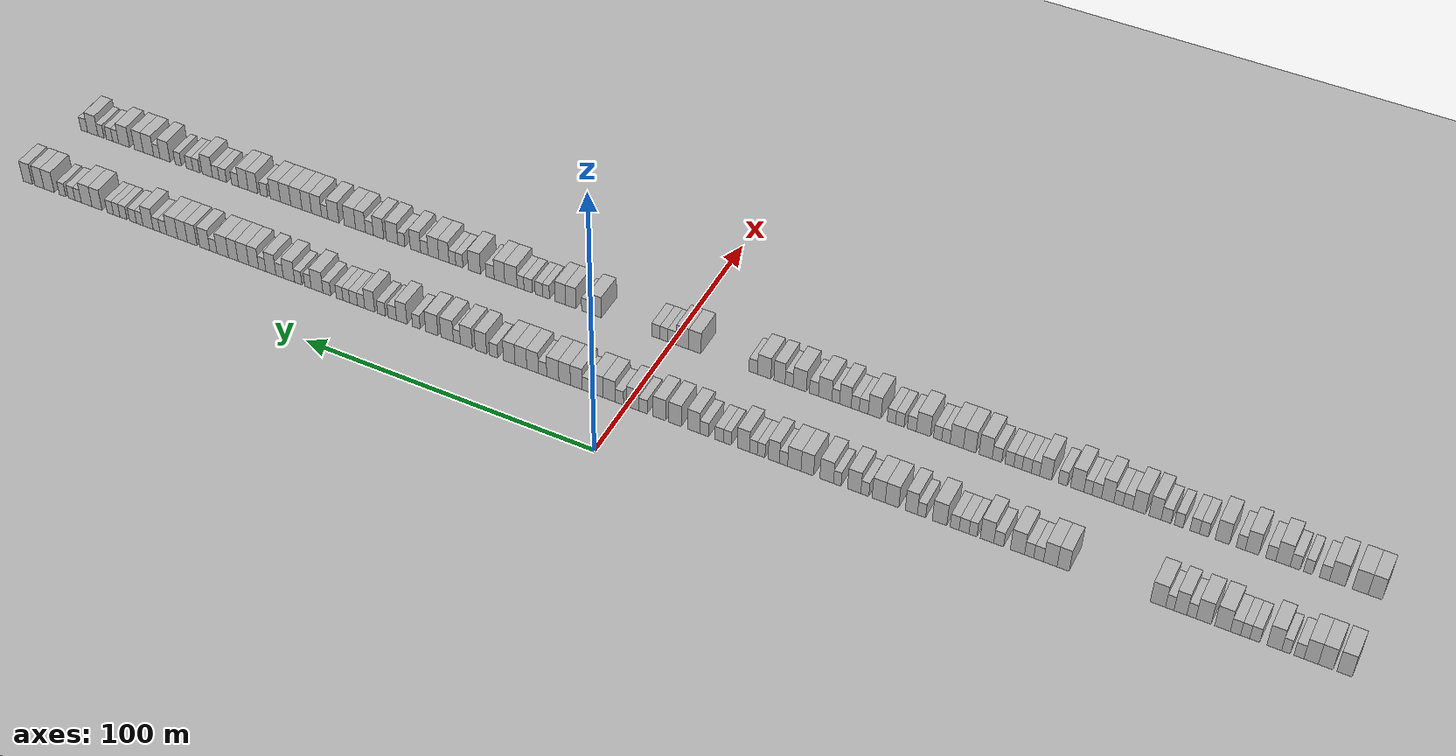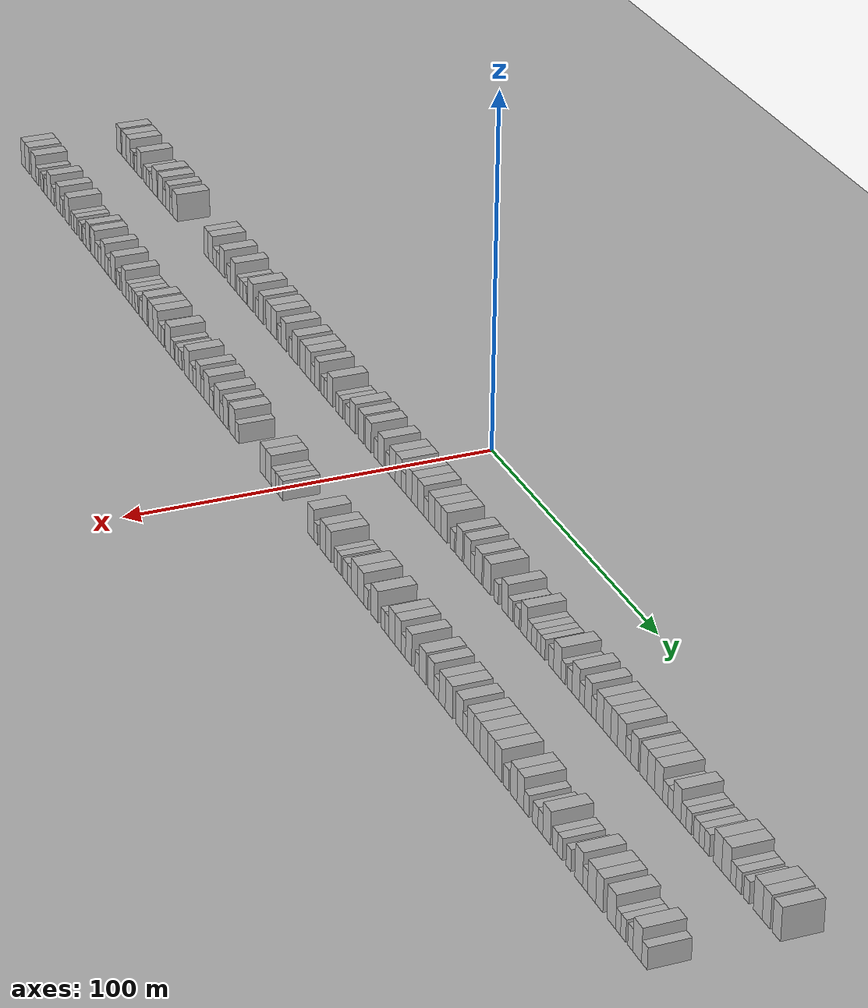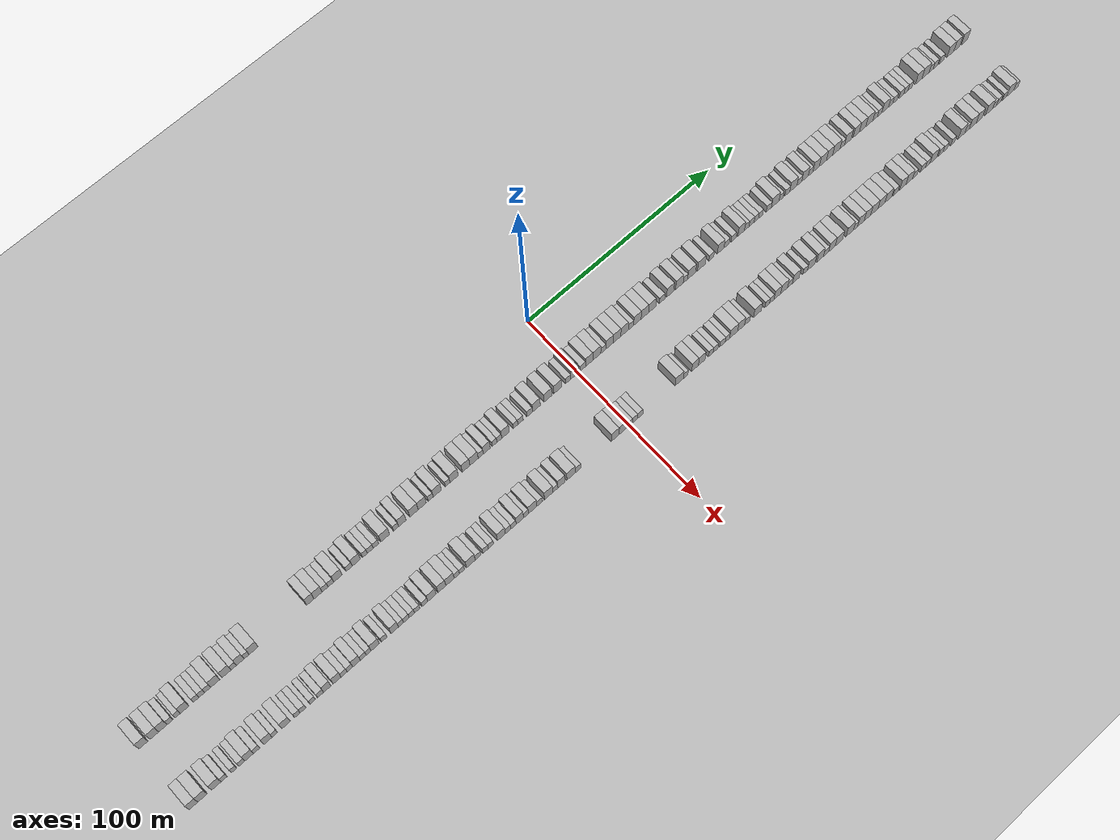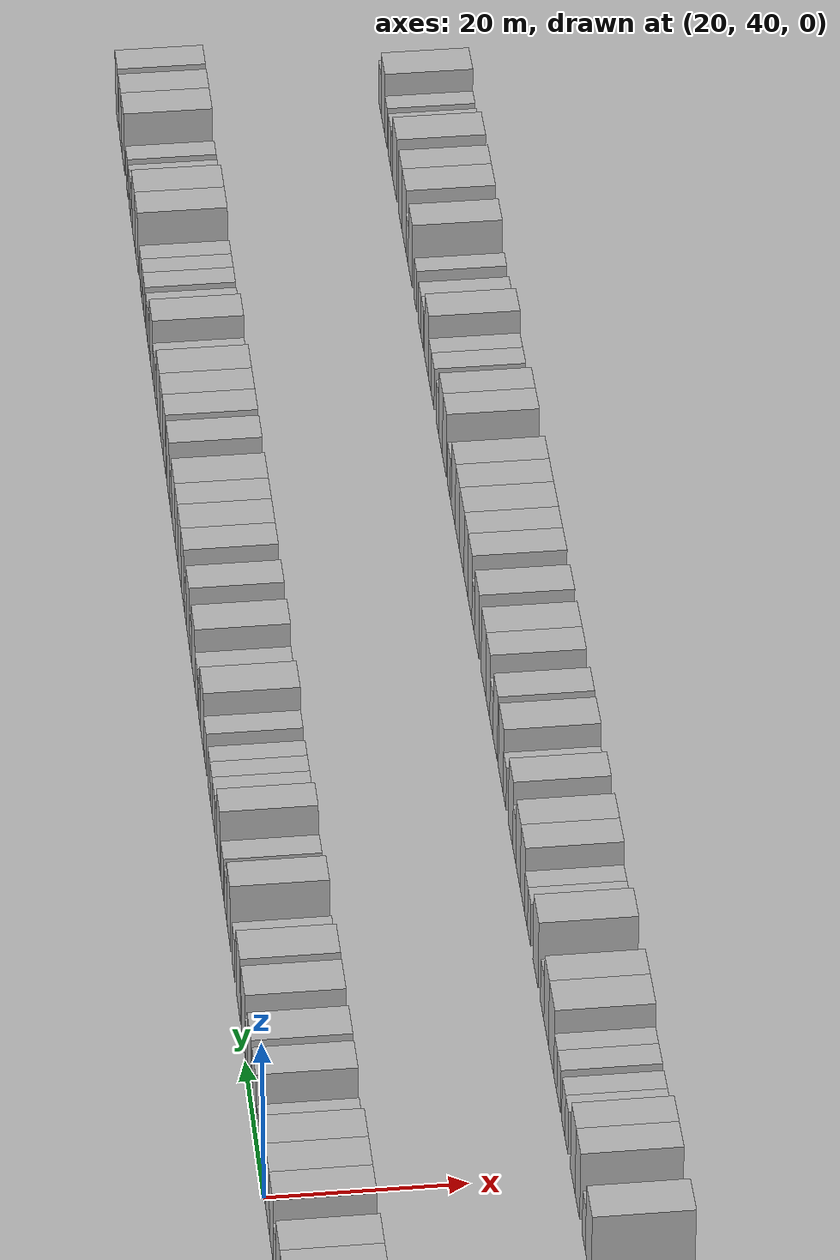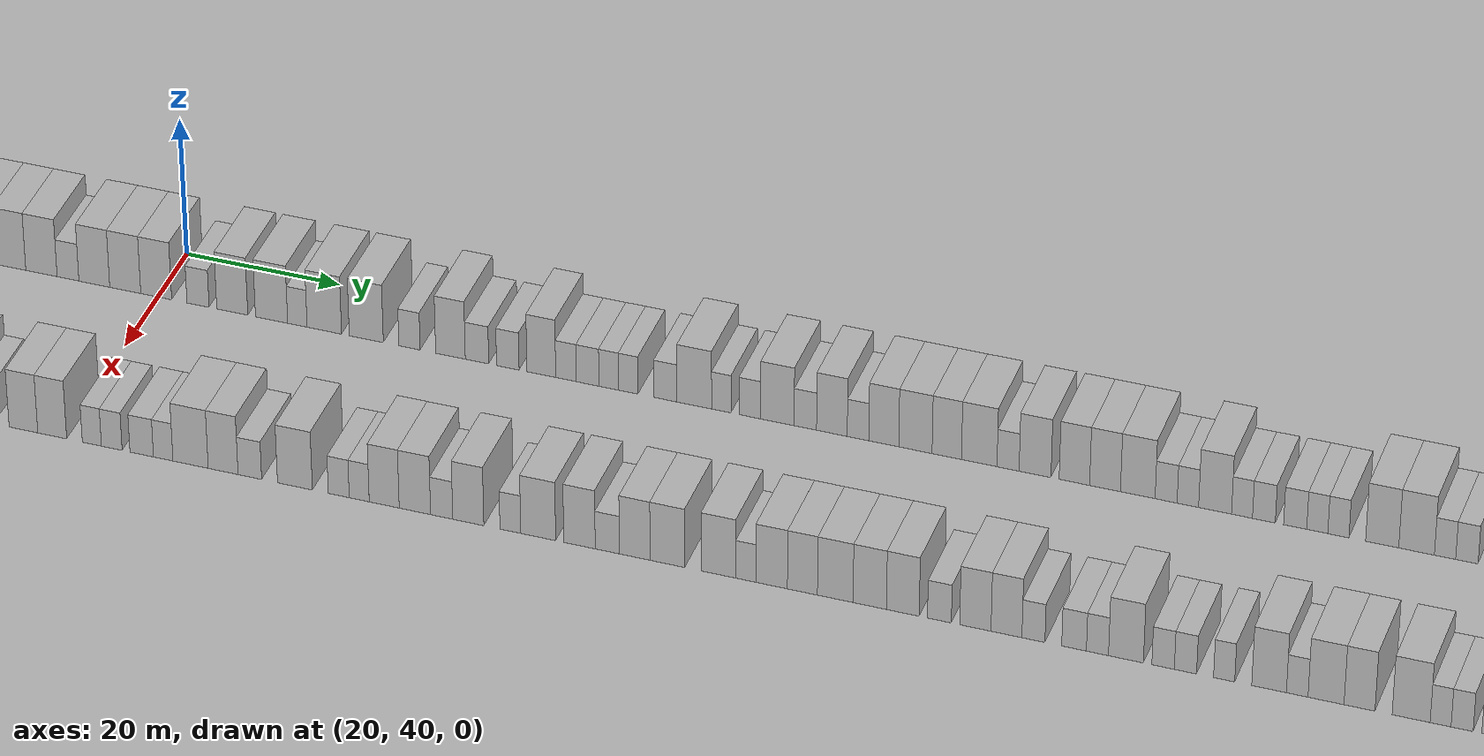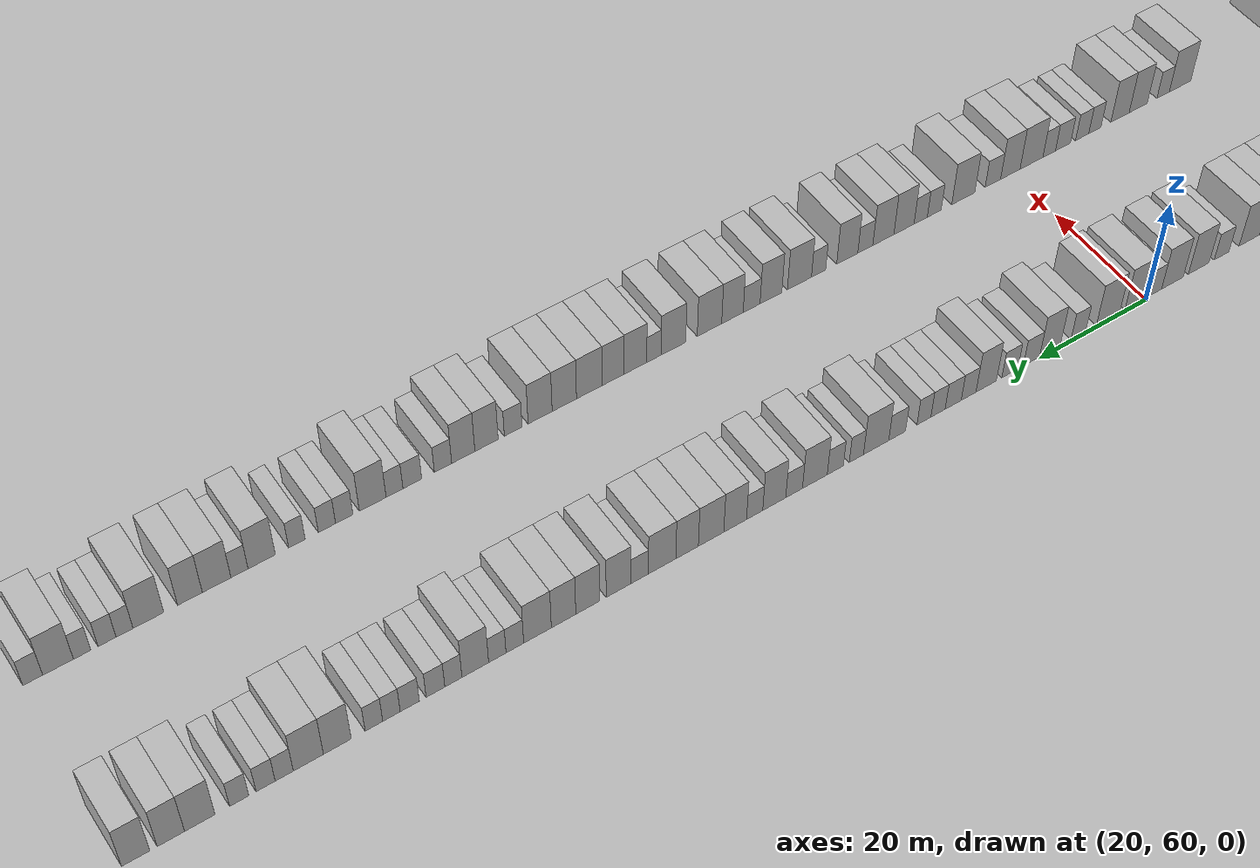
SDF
<?xml version="1.0" encoding="utf-8"?>

<sdf version="1.6">

   <world name="default">

      <gui fullscreen="0">

         <camera name="user_camera">

            <pose>-15 0 4.57585 0 0 0</pose>

            <view_controller>orbit</view_controller>

         </camera>

      </gui>

      <scene>

         <sky>

           <clouds>

             <speed>12</speed>

           </clouds>

         </sky>

         <ambient>0.4 0.4 0.4 1</ambient>

         <background>0.7 0.7 0.7 1</background>

         <shadows>1</shadows>

      </scene>

      <gravity>0 0 -9.8066</gravity>

      <magnetic_field>6e-06 2.3e-05 -4.2e-05</magnetic_field>

      <physics default="0" name="default_physics" type="ode">

         <ode>

            <solver>

               <type>quick</type>

               <iters>10</iters>

               <sor>1.0</sor>

               <use_dynamic_moi_rescaling>0</use_dynamic_moi_rescaling>

            </solver>

            <constraints>

               <cfm>0</cfm>

               <erp>0.2</erp>

               <contact_max_correcting_vel>100</contact_max_correcting_vel>

               <contact_surface_layer>0.001</contact_surface_layer>

            </constraints>

         </ode>

         <max_step_size>0.004</max_step_size>

         <real_time_factor>1</real_time_factor>

         <real_time_update_rate>250</real_time_update_rate>

      </physics>

      <light name="sun" type="directional">

         <cast_shadows>1</cast_shadows>

         <pose>0 0 10 0 0 0</pose>

         <diffuse>0.8 0.8 0.8 1</diffuse>

         <specular>0.2 0.2 0.2 1</specular>

         <attenuation>

            <range>1000</range>

            <constant>0.9</constant>

            <linear>0.01</linear>

            <quadratic>0.001</quadratic>

         </attenuation>

         <direction>-0.5 0.1 -0.9</direction>

      </light>

      <include>

         <name>ground_plane_1</name>

         <uri>model://HANNAS_ground_plane</uri>

         <pose>0 0 0  0 0 0</pose>

      </include>

      <include>

         <name>ground_plane_2</name>

         <uri>model://HANNAS_ground_plane</uri>

         <pose>100 0 0  0 0 0</pose>

      </include>

      <model name="building_1">

         <static>1</static>

         <pose frame="">25.0000 -217.8854 0 0.000000 0.000000 0.000000</pose>

         <link name="link">

            <pose frame="">0 0 4.50 0 0 0</pose>

            <collision name="collision">

               <geometry>

                  <box>

                     <size>10.0000 4.2292 9.0000</size>

                  </box>

               </geometry>

               <max_contacts>10</max_contacts>

               <surface>

                  <contact>

                     <ode/>

                  </contact>

                  <bounce/>

                  <friction>

                     <torsional>

                        <ode/>

                     </torsional>

                     <ode/>

                  </friction>

               </surface>

            </collision>

            <visual name="visual">

               <cast_shadows>0</cast_shadows>

               <geometry>

                  <box>

                     <size>10.0000 4.2292 9.0000</size>

                  </box>

               </geometry>

               <material>

                  <script>

                     <uri>model://HANNAS_wall/materials/scripts</uri>

                     <uri>model://HANNAS_wall/materials/textures</uri>

                     <name>vrc/HANNAS_wall</name>

                  </script>

               </material>

            </visual>

            <self_collide>0</self_collide>

            <enable_wind>0</enable_wind>

            <kinematic>0</kinematic>

         </link>

      </model>

      <model name="building_2">

         <static>1</static>

         <pose frame="">25.0000 -212.7243 0 0.000000 0.000000 0.000000</pose>

         <link name="link">

            <pose frame="">0 0 4.50 0 0 0</pose>

            <collision name="collision">

               <geometry>

                  <box>

                     <size>10.0000 4.0931 9.0000</size>

                  </box>

               </geometry>

               <max_contacts>10</max_contacts>

               <surface>

                  <contact>

                     <ode/>

                  </contact>

                  <bounce/>

                  <friction>

                     <torsional>

                        <ode/>

                     </torsional>

                     <ode/>

                  </friction>

               </surface>

            </collision>

            <visual name="visual">

               <cast_shadows>0</cast_shadows>

               <geometry>

                  <box>

                     <size>10.0000 4.0931 9.0000</size>

                  </box>

               </geometry>

               <material>

                  <script>

                     <uri>model://HANNAS_wall/materials/scripts</uri>

                     <uri>model://HANNAS_wall/materials/textures</uri>

                     <name>vrc/HANNAS_wall</name>

                  </script>

               </material>

            </visual>

            <self_collide>0</self_collide>

            <enable_wind>0</enable_wind>

            <kinematic>0</kinematic>

         </link>

      </model>

      <model name="building_3">

         <static>1</static>

         <pose frame="">25.0000 -208.7025 0 0.000000 0.000000 0.000000</pose>

         <link name="link">

            <pose frame="">0 0 4.50 0 0 0</pose>

            <collision name="collision">

               <geometry>

                  <box>

                     <size>10.0000 3.9504 9.0000</size>

                  </box>

               </geometry>

               <max_contacts>10</max_contacts>

               <surface>

                  <contact>

                     <ode/>

                  </contact>

                  <bounce/>

                  <friction>

                     <torsional>

                        <ode/>

                     </torsional>

                     <ode/>

                  </friction>

               </surface>

            </collision>

            <visual name="visual">

               <cast_shadows>0</cast_shadows>

               <geometry>

                  <box>

                     <size>10.0000 3.9504 9.0000</size>

                  </box>

               </geometry>

               <material>

                  <script>

                     <uri>model://HANNAS_wall/materials/scripts</uri>

                     <uri>model://HANNAS_wall/materials/textures</uri>

                     <name>vrc/HANNAS_wall</name>

                  </script>

               </material>

            </visual>

            <self_collide>0</self_collide>

            <enable_wind>0</enable_wind>

            <kinematic>0</kinematic>

         </link>

      </model>

      <model name="building_4">

         <static>1</static>

         <pose frame="">25.0000 -205.3398 0 0.000000 0.000000 0.000000</pose>

         <link name="link">

            <pose frame="">0 0 3.00 0 0 0</pose>

            <collision name="collision">

               <geometry>

                  <box>

                     <size>10.0000 2.7752 6.0000</size>

                  </box>

               </geometry>

               <max_contacts>10</max_contacts>

               <surface>

                  <contact>

                     <ode/>

                  </contact>

                  <bounce/>

                  <friction>

                     <torsional>

                        <ode/>

                     </torsional>

                     <ode/>

                  </friction>

               </surface>

            </collision>

            <visual name="visual">

               <cast_shadows>0</cast_shadows>

               <geometry>

                  <box>

                     <size>10.0000 2.7752 6.0000</size>

                  </box>

               </geometry>

               <material>

                  <script>

                     <uri>model://HANNAS_wall/materials/scripts</uri>

                     <uri>model://HANNAS_wall/materials/textures</uri>

                     <name>vrc/HANNAS_wall</name>

                  </script>

               </material>

            </visual>

            <self_collide>0</self_collide>

            <enable_wind>0</enable_wind>

            <kinematic>0</kinematic>

         </link>

      </model>

      <model name="building_5">

         <static>1</static>

         <pose frame="">25.0000 -201.7482 0 0.000000 0.000000 0.000000</pose>

         <link name="link">

            <pose frame="">0 0 3.00 0 0 0</pose>

            <collision name="collision">

               <geometry>

                  <box>

                     <size>10.0000 2.4080 6.0000</size>

                  </box>

               </geometry>

               <max_contacts>10</max_contacts>

               <surface>

                  <contact>

                     <ode/>

                  </contact>

                  <bounce/>

                  <friction>

                     <torsional>

                        <ode/>

                     </torsional>

                     <ode/>

                  </friction>

               </surface>

            </collision>

            <visual name="visual">

               <cast_shadows>0</cast_shadows>

               <geometry>

                  <box>

                     <size>10.0000 2.4080 6.0000</size>

                  </box>

               </geometry>

               <material>

                  <script>

                     <uri>model://HANNAS_wall/materials/scripts</uri>

                     <uri>model://HANNAS_wall/materials/textures</uri>

                     <name>vrc/HANNAS_wall</name>

                  </script>

               </material>

            </visual>

            <self_collide>0</self_collide>

            <enable_wind>0</enable_wind>

            <kinematic>0</kinematic>

         </link>

      </model>

      <model name="building_6">

         <static>1</static>

         <pose frame="">25.0000 -198.4909 0 0.000000 0.000000 0.000000</pose>

         <link name="link">

            <pose frame="">0 0 4.50 0 0 0</pose>

            <collision name="collision">

               <geometry>

                  <box>

                     <size>10.0000 4.1066 9.0000</size>

                  </box>

               </geometry>

               <max_contacts>10</max_contacts>

               <surface>

                  <contact>

                     <ode/>

                  </contact>

                  <bounce/>

                  <friction>

                     <torsional>

                        <ode/>

                     </torsional>

                     <ode/>

                  </friction>

               </surface>

            </collision>

            <visual name="visual">

               <cast_shadows>0</cast_shadows>

               <geometry>

                  <box>

                     <size>10.0000 4.1066 9.0000</size>

                  </box>

               </geometry>

               <material>

                  <script>

                     <uri>model://HANNAS_wall/materials/scripts</uri>

                     <uri>model://HANNAS_wall/materials/textures</uri>

                     <name>vrc/HANNAS_wall</name>

                  </script>

               </material>

            </visual>

            <self_collide>0</self_collide>

            <enable_wind>0</enable_wind>

            <kinematic>0</kinematic>

         </link>

      </model>

      <model name="building_7">

         <static>1</static>

         <pose frame="">25.0000 -193.0438 0 0.000000 0.000000 0.000000</pose>

         <link name="link">

            <pose frame="">0 0 3.00 0 0 0</pose>

            <collision name="collision">

               <geometry>

                  <box>

                     <size>10.0000 2.7875 6.0000</size>

                  </box>

               </geometry>

               <max_contacts>10</max_contacts>

               <surface>

                  <contact>

                     <ode/>

                  </contact>

                  <bounce/>

                  <friction>

                     <torsional>

                        <ode/>

                     </torsional>

                     <ode/>

                  </friction>

               </surface>

            </collision>

            <visual name="visual">

               <cast_shadows>0</cast_shadows>

               <geometry>

                  <box>

                     <size>10.0000 2.7875 6.0000</size>

                  </box>

               </geometry>

               <material>

                  <script>

                     <uri>model://HANNAS_wall/materials/scripts</uri>

                     <uri>model://HANNAS_wall/materials/textures</uri>

                     <name>vrc/HANNAS_wall</name>

                  </script>

               </material>

            </visual>

            <self_collide>0</self_collide>

            <enable_wind>0</enable_wind>

            <kinematic>0</kinematic>

         </link>

      </model>

      <model name="building_8">

         <static>1</static>

         <pose frame="">25.0000 -190.3522 0 0.000000 0.000000 0.000000</pose>

         <link name="link">

            <pose frame="">0 0 3.00 0 0 0</pose>

            <collision name="collision">

               <geometry>

                  <box>

                     <size>10.0000 2.5958 6.0000</size>

                  </box>

               </geometry>

               <max_contacts>10</max_contacts>

               <surface>

                  <contact>

                     <ode/>

                  </contact>

                  <bounce/>

                  <friction>

                     <torsional>

                        <ode/>

                     </torsional>

                     <ode/>

                  </friction>

               </surface>

            </collision>

            <visual name="visual">

               <cast_shadows>0</cast_shadows>

               <geometry>

                  <box>

                     <size>10.0000 2.5958 6.0000</size>

                  </box>

               </geometry>

               <material>

                  <script>

                     <uri>model://HANNAS_wall/materials/scripts</uri>

                     <uri>model://HANNAS_wall/materials/textures</uri>

                     <name>vrc/HANNAS_wall</name>

                  </script>

               </material>

            </visual>

            <self_collide>0</self_collide>

            <enable_wind>0</enable_wind>

            <kinematic>0</kinematic>

         </link>

      </model>

      <model name="building_9">

         <static>1</static>

         <pose frame="">25.0000 -187.6102 0 0.000000 0.000000 0.000000</pose>

         <link name="link">

            <pose frame="">0 0 3.00 0 0 0</pose>

            <collision name="collision">

               <geometry>

                  <box>

                     <size>10.0000 2.8883 6.0000</size>

                  </box>

               </geometry>

               <max_contacts>10</max_contacts>

               <surface>

                  <contact>

                     <ode/>

                  </contact>

                  <bounce/>

                  <friction>

                     <torsional>

                        <ode/>

                     </torsional>

                     <ode/>

                  </friction>

               </surface>

            </collision>

            <visual name="visual">

               <cast_shadows>0</cast_shadows>

               <geometry>

                  <box>

                     <size>10.0000 2.8883 6.0000</size>

                  </box>

               </geometry>

               <material>

                  <script>

                     <uri>model://HANNAS_wall/materials/scripts</uri>

                     <uri>model://HANNAS_wall/materials/textures</uri>

                     <name>vrc/HANNAS_wall</name>

                  </script>

               </material>

            </visual>

            <self_collide>0</self_collide>

            <enable_wind>0</enable_wind>

            <kinematic>0</kinematic>

         </link>

      </model>

      <model name="building_10">

         <static>1</static>

         <pose frame="">25.0000 -183.9573 0 0.000000 0.000000 0.000000</pose>

         <link name="link">

            <pose frame="">0 0 4.50 0 0 0</pose>

            <collision name="collision">

               <geometry>

                  <box>

                     <size>10.0000 4.4174 9.0000</size>

                  </box>

               </geometry>

               <max_contacts>10</max_contacts>

               <surface>

                  <contact>

                     <ode/>

                  </contact>

                  <bounce/>

                  <friction>

                     <torsional>

                        <ode/>

                     </torsional>

                     <ode/>

                  </friction>

               </surface>

            </collision>

            <visual name="visual">

               <cast_shadows>0</cast_shadows>

               <geometry>

                  <box>

                     <size>10.0000 4.4174 9.0000</size>

                  </box>

               </geometry>

               <material>

                  <script>

                     <uri>model://HANNAS_wall/materials/scripts</uri>

                     <uri>model://HANNAS_wall/materials/textures</uri>

                     <name>vrc/HANNAS_wall</name>

                  </script>

               </material>

            </visual>

            <self_collide>0</self_collide>

            <enable_wind>0</enable_wind>

            <kinematic>0</kinematic>

         </link>

      </model>

      <model name="building_11">

         <static>1</static>

         <pose frame="">25.0000 -178.5948 0 0.000000 0.000000 0.000000</pose>

         <link name="link">

            <pose frame="">0 0 4.50 0 0 0</pose>

            <collision name="collision">

               <geometry>

                  <box>

                     <size>10.0000 4.3075 9.0000</size>

                  </box>

               </geometry>

               <max_contacts>10</max_contacts>

               <surface>

                  <contact>

                     <ode/>

                  </contact>

                  <bounce/>

                  <friction>

                     <torsional>

                        <ode/>

                     </torsional>

                     <ode/>

                  </friction>

               </surface>

            </collision>

            <visual name="visual">

               <cast_shadows>0</cast_shadows>

               <geometry>

                  <box>

                     <size>10.0000 4.3075 9.0000</size>

                  </box>

               </geometry>

               <material>

                  <script>

                     <uri>model://HANNAS_wall/materials/scripts</uri>

                     <uri>model://HANNAS_wall/materials/textures</uri>

                     <name>vrc/HANNAS_wall</name>

                  </script>

               </material>

            </visual>

            <self_collide>0</self_collide>

            <enable_wind>0</enable_wind>

            <kinematic>0</kinematic>

         </link>

      </model>

      <model name="building_12">

         <static>1</static>

         <pose frame="">25.0000 -175.1454 0 0.000000 0.000000 0.000000</pose>

         <link name="link">

            <pose frame="">0 0 3.00 0 0 0</pose>

            <collision name="collision">

               <geometry>

                  <box>

                     <size>10.0000 2.5914 6.0000</size>

                  </box>

               </geometry>

               <max_contacts>10</max_contacts>

               <surface>

                  <contact>

                     <ode/>

                  </contact>

                  <bounce/>

                  <friction>

                     <torsional>

                        <ode/>

                     </torsional>

                     <ode/>

                  </friction>

               </surface>

            </collision>

            <visual name="visual">

               <cast_shadows>0</cast_shadows>

               <geometry>

                  <box>

                     <size>10.0000 2.5914 6.0000</size>

                  </box>

               </geometry>

               <material>

                  <script>

                     <uri>model://HANNAS_wall/materials/scripts</uri>

                     <uri>model://HANNAS_wall/materials/textures</uri>

                     <name>vrc/HANNAS_wall</name>

                  </script>

               </material>

            </visual>

            <self_collide>0</self_collide>

            <enable_wind>0</enable_wind>

            <kinematic>0</kinematic>

         </link>

      </model>

      <model name="building_13">

         <static>1</static>

         <pose frame="">25.0000 -172.0141 0 0.000000 0.000000 0.000000</pose>

         <link name="link">

            <pose frame="">0 0 4.50 0 0 0</pose>

            <collision name="collision">

               <geometry>

                  <box>

                     <size>10.0000 3.6710 9.0000</size>

                  </box>

               </geometry>

               <max_contacts>10</max_contacts>

               <surface>

                  <contact>

                     <ode/>

                  </contact>

                  <bounce/>

                  <friction>

                     <torsional>

                        <ode/>

                     </torsional>

                     <ode/>

                  </friction>

               </surface>

            </collision>

            <visual name="visual">

               <cast_shadows>0</cast_shadows>

               <geometry>

                  <box>

                     <size>10.0000 3.6710 9.0000</size>

                  </box>

               </geometry>

               <material>

                  <script>

                     <uri>model://HANNAS_wall/materials/scripts</uri>

                     <uri>model://HANNAS_wall/materials/textures</uri>

                     <name>vrc/HANNAS_wall</name>

                  </script>

               </material>

            </visual>

            <self_collide>0</self_collide>

            <enable_wind>0</enable_wind>

            <kinematic>0</kinematic>

         </link>

      </model>

      <model name="building_14">

         <static>1</static>

         <pose frame="">25.0000 -168.9576 0 0.000000 0.000000 0.000000</pose>

         <link name="link">

            <pose frame="">0 0 3.00 0 0 0</pose>

            <collision name="collision">

               <geometry>

                  <box>

                     <size>10.0000 2.4421 6.0000</size>

                  </box>

               </geometry>

               <max_contacts>10</max_contacts>

               <surface>

                  <contact>

                     <ode/>

                  </contact>

                  <bounce/>

                  <friction>

                     <torsional>

                        <ode/>

                     </torsional>

                     <ode/>

                  </friction>

               </surface>

            </collision>

            <visual name="visual">

               <cast_shadows>0</cast_shadows>

               <geometry>

                  <box>

                     <size>10.0000 2.4421 6.0000</size>

                  </box>

               </geometry>

               <material>

                  <script>

                     <uri>model://HANNAS_wall/materials/scripts</uri>

                     <uri>model://HANNAS_wall/materials/textures</uri>

                     <name>vrc/HANNAS_wall</name>

                  </script>

               </material>

            </visual>

            <self_collide>0</self_collide>

            <enable_wind>0</enable_wind>

            <kinematic>0</kinematic>

         </link>

      </model>

      <model name="building_15">

         <static>1</static>

         <pose frame="">25.0000 -165.5291 0 0.000000 0.000000 0.000000</pose>

         <link name="link">

            <pose frame="">0 0 4.50 0 0 0</pose>

            <collision name="collision">

               <geometry>

                  <box>

                     <size>10.0000 4.4150 9.0000</size>

                  </box>

               </geometry>

               <max_contacts>10</max_contacts>

               <surface>

                  <contact>

                     <ode/>

                  </contact>

                  <bounce/>

                  <friction>

                     <torsional>

                        <ode/>

                     </torsional>

                     <ode/>

                  </friction>

               </surface>

            </collision>

            <visual name="visual">

               <cast_shadows>0</cast_shadows>

               <geometry>

                  <box>

                     <size>10.0000 4.4150 9.0000</size>

                  </box>

               </geometry>

               <material>

                  <script>

                     <uri>model://HANNAS_wall/materials/scripts</uri>

                     <uri>model://HANNAS_wall/materials/textures</uri>

                     <name>vrc/HANNAS_wall</name>

                  </script>

               </material>

            </visual>

            <self_collide>0</self_collide>

            <enable_wind>0</enable_wind>

            <kinematic>0</kinematic>

         </link>

      </model>

      <model name="building_16">

         <static>1</static>

         <pose frame="">25.0000 -137.9047 0 0.000000 0.000000 0.000000</pose>

         <link name="link">

            <pose frame="">0 0 4.50 0 0 0</pose>

            <collision name="collision">

               <geometry>

                  <box>

                     <size>10.0000 3.6113 9.0000</size>

                  </box>

               </geometry>

               <max_contacts>10</max_contacts>

               <surface>

                  <contact>

                     <ode/>

                  </contact>

                  <bounce/>

                  <friction>

                     <torsional>

                        <ode/>

                     </torsional>

                     <ode/>

                  </friction>

               </surface>

            </collision>

            <visual name="visual">

               <cast_shadows>0</cast_shadows>

               <geometry>

                  <box>

                     <size>10.0000 3.6113 9.0000</size>

                  </box>

               </geometry>

               <material>

                  <script>

                     <uri>model://HANNAS_wall/materials/scripts</uri>

                     <uri>model://HANNAS_wall/materials/textures</uri>

                     <name>vrc/HANNAS_wall</name>

                  </script>

               </material>

            </visual>

            <self_collide>0</self_collide>

            <enable_wind>0</enable_wind>

            <kinematic>0</kinematic>

         </link>

      </model>

      <model name="building_17">

         <static>1</static>

         <pose frame="">25.0000 -134.0874 0 0.000000 0.000000 0.000000</pose>

         <link name="link">

            <pose frame="">0 0 4.50 0 0 0</pose>

            <collision name="collision">

               <geometry>

                  <box>

                     <size>10.0000 4.0233 9.0000</size>

                  </box>

               </geometry>

               <max_contacts>10</max_contacts>

               <surface>

                  <contact>

                     <ode/>

                  </contact>

                  <bounce/>

                  <friction>

                     <torsional>

                        <ode/>

                     </torsional>

                     <ode/>

                  </friction>

               </surface>

            </collision>

            <visual name="visual">

               <cast_shadows>0</cast_shadows>

               <geometry>

                  <box>

                     <size>10.0000 4.0233 9.0000</size>

                  </box>

               </geometry>

               <material>

                  <script>

                     <uri>model://HANNAS_wall/materials/scripts</uri>

                     <uri>model://HANNAS_wall/materials/textures</uri>

                     <name>vrc/HANNAS_wall</name>

                  </script>

               </material>

            </visual>

            <self_collide>0</self_collide>

            <enable_wind>0</enable_wind>

            <kinematic>0</kinematic>

         </link>

      </model>

      <model name="building_18">

         <static>1</static>

         <pose frame="">25.0000 -130.6236 0 0.000000 0.000000 0.000000</pose>

         <link name="link">

            <pose frame="">0 0 3.00 0 0 0</pose>

            <collision name="collision">

               <geometry>

                  <box>

                     <size>10.0000 2.9042 6.0000</size>

                  </box>

               </geometry>

               <max_contacts>10</max_contacts>

               <surface>

                  <contact>

                     <ode/>

                  </contact>

                  <bounce/>

                  <friction>

                     <torsional>

                        <ode/>

                     </torsional>

                     <ode/>

                  </friction>

               </surface>

            </collision>

            <visual name="visual">

               <cast_shadows>0</cast_shadows>

               <geometry>

                  <box>

                     <size>10.0000 2.9042 6.0000</size>

                  </box>

               </geometry>

               <material>

                  <script>

                     <uri>model://HANNAS_wall/materials/scripts</uri>

                     <uri>model://HANNAS_wall/materials/textures</uri>

                     <name>vrc/HANNAS_wall</name>

                  </script>

               </material>

            </visual>

            <self_collide>0</self_collide>

            <enable_wind>0</enable_wind>

            <kinematic>0</kinematic>

         </link>

      </model>

      <model name="building_19">

         <static>1</static>

         <pose frame="">25.0000 -127.7901 0 0.000000 0.000000 0.000000</pose>

         <link name="link">

            <pose frame="">0 0 3.00 0 0 0</pose>

            <collision name="collision">

               <geometry>

                  <box>

                     <size>10.0000 2.7628 6.0000</size>

                  </box>

               </geometry>

               <max_contacts>10</max_contacts>

               <surface>

                  <contact>

                     <ode/>

                  </contact>

                  <bounce/>

                  <friction>

                     <torsional>

                        <ode/>

                     </torsional>

                     <ode/>

                  </friction>

               </surface>

            </collision>

            <visual name="visual">

               <cast_shadows>0</cast_shadows>

               <geometry>

                  <box>

                     <size>10.0000 2.7628 6.0000</size>

                  </box>

               </geometry>

               <material>

                  <script>

                     <uri>model://HANNAS_wall/materials/scripts</uri>

                     <uri>model://HANNAS_wall/materials/textures</uri>

                     <name>vrc/HANNAS_wall</name>

                  </script>

               </material>

            </visual>

            <self_collide>0</self_collide>

            <enable_wind>0</enable_wind>

            <kinematic>0</kinematic>

         </link>

      </model>

      <model name="building_20">

         <static>1</static>

         <pose frame="">25.0000 -124.2791 0 0.000000 0.000000 0.000000</pose>

         <link name="link">

            <pose frame="">0 0 4.50 0 0 0</pose>

            <collision name="collision">

               <geometry>

                  <box>

                     <size>10.0000 4.2591 9.0000</size>

                  </box>

               </geometry>

               <max_contacts>10</max_contacts>

               <surface>

                  <contact>

                     <ode/>

                  </contact>

                  <bounce/>

                  <friction>

                     <torsional>

                        <ode/>

                     </torsional>

                     <ode/>

                  </friction>

               </surface>

            </collision>

            <visual name="visual">

               <cast_shadows>0</cast_shadows>

               <geometry>

                  <box>

                     <size>10.0000 4.2591 9.0000</size>

                  </box>

               </geometry>

               <material>

                  <script>

                     <uri>model://HANNAS_wall/materials/scripts</uri>

                     <uri>model://HANNAS_wall/materials/textures</uri>

                     <name>vrc/HANNAS_wall</name>

                  </script>

               </material>

            </visual>

            <self_collide>0</self_collide>

            <enable_wind>0</enable_wind>

            <kinematic>0</kinematic>

         </link>

      </model>

      <model name="building_21">

         <static>1</static>

         <pose frame="">25.0000 -118.6616 0 0.000000 0.000000 0.000000</pose>

         <link name="link">

            <pose frame="">0 0 3.00 0 0 0</pose>

            <collision name="collision">

               <geometry>

                  <box>

                     <size>10.0000 2.9758 6.0000</size>

                  </box>

               </geometry>

               <max_contacts>10</max_contacts>

               <surface>

                  <contact>

                     <ode/>

                  </contact>

                  <bounce/>

                  <friction>

                     <torsional>

                        <ode/>

                     </torsional>

                     <ode/>

                  </friction>

               </surface>

            </collision>

            <visual name="visual">

               <cast_shadows>0</cast_shadows>

               <geometry>

                  <box>

                     <size>10.0000 2.9758 6.0000</size>

                  </box>

               </geometry>

               <material>

                  <script>

                     <uri>model://HANNAS_wall/materials/scripts</uri>

                     <uri>model://HANNAS_wall/materials/textures</uri>

                     <name>vrc/HANNAS_wall</name>

                  </script>

               </material>

            </visual>

            <self_collide>0</self_collide>

            <enable_wind>0</enable_wind>

            <kinematic>0</kinematic>

         </link>

      </model>

      <model name="building_22">

         <static>1</static>

         <pose frame="">25.0000 -115.1251 0 0.000000 0.000000 0.000000</pose>

         <link name="link">

            <pose frame="">0 0 4.50 0 0 0</pose>

            <collision name="collision">

               <geometry>

                  <box>

                     <size>10.0000 4.0973 9.0000</size>

                  </box>

               </geometry>

               <max_contacts>10</max_contacts>

               <surface>

                  <contact>

                     <ode/>

                  </contact>

                  <bounce/>

                  <friction>

                     <torsional>

                        <ode/>

                     </torsional>

                     <ode/>

                  </friction>

               </surface>

            </collision>

            <visual name="visual">

               <cast_shadows>0</cast_shadows>

               <geometry>

                  <box>

                     <size>10.0000 4.0973 9.0000</size>

                  </box>

               </geometry>

               <material>

                  <script>

                     <uri>model://HANNAS_wall/materials/scripts</uri>

                     <uri>model://HANNAS_wall/materials/textures</uri>

                     <name>vrc/HANNAS_wall</name>

                  </script>

               </material>

            </visual>

            <self_collide>0</self_collide>

            <enable_wind>0</enable_wind>

            <kinematic>0</kinematic>

         </link>

      </model>

      <model name="building_23">

         <static>1</static>

         <pose frame="">25.0000 -110.8517 0 0.000000 0.000000 0.000000</pose>

         <link name="link">

            <pose frame="">0 0 3.00 0 0 0</pose>

            <collision name="collision">

               <geometry>

                  <box>

                     <size>10.0000 2.4496 6.0000</size>

                  </box>

               </geometry>

               <max_contacts>10</max_contacts>

               <surface>

                  <contact>

                     <ode/>

                  </contact>

                  <bounce/>

                  <friction>

                     <torsional>

                        <ode/>

                     </torsional>

                     <ode/>

                  </friction>

               </surface>

            </collision>

            <visual name="visual">

               <cast_shadows>0</cast_shadows>

               <geometry>

                  <box>

                     <size>10.0000 2.4496 6.0000</size>

                  </box>

               </geometry>

               <material>

                  <script>

                     <uri>model://HANNAS_wall/materials/scripts</uri>

                     <uri>model://HANNAS_wall/materials/textures</uri>

                     <name>vrc/HANNAS_wall</name>

                  </script>

               </material>

            </visual>

            <self_collide>0</self_collide>

            <enable_wind>0</enable_wind>

            <kinematic>0</kinematic>

         </link>

      </model>

      <model name="building_24">

         <static>1</static>

         <pose frame="">25.0000 -108.1369 0 0.000000 0.000000 0.000000</pose>

         <link name="link">

            <pose frame="">0 0 3.00 0 0 0</pose>

            <collision name="collision">

               <geometry>

                  <box>

                     <size>10.0000 2.9800 6.0000</size>

                  </box>

               </geometry>

               <max_contacts>10</max_contacts>

               <surface>

                  <contact>

                     <ode/>

                  </contact>

                  <bounce/>

                  <friction>

                     <torsional>

                        <ode/>

                     </torsional>

                     <ode/>

                  </friction>

               </surface>

            </collision>

            <visual name="visual">

               <cast_shadows>0</cast_shadows>

               <geometry>

                  <box>

                     <size>10.0000 2.9800 6.0000</size>

                  </box>

               </geometry>

               <material>

                  <script>

                     <uri>model://HANNAS_wall/materials/scripts</uri>

                     <uri>model://HANNAS_wall/materials/textures</uri>

                     <name>vrc/HANNAS_wall</name>

                  </script>

               </material>

            </visual>

            <self_collide>0</self_collide>

            <enable_wind>0</enable_wind>

            <kinematic>0</kinematic>

         </link>

      </model>

      <model name="building_25">

         <static>1</static>

         <pose frame="">25.0000 -105.2739 0 0.000000 0.000000 0.000000</pose>

         <link name="link">

            <pose frame="">0 0 3.00 0 0 0</pose>

            <collision name="collision">

               <geometry>

                  <box>

                     <size>10.0000 2.7460 6.0000</size>

                  </box>

               </geometry>

               <max_contacts>10</max_contacts>

               <surface>

                  <contact>

                     <ode/>

                  </contact>

                  <bounce/>

                  <friction>

                     <torsional>

                        <ode/>

                     </torsional>

                     <ode/>

                  </friction>

               </surface>

            </collision>

            <visual name="visual">

               <cast_shadows>0</cast_shadows>

               <geometry>

                  <box>

                     <size>10.0000 2.7460 6.0000</size>

                  </box>

               </geometry>

               <material>

                  <script>

                     <uri>model://HANNAS_wall/materials/scripts</uri>

                     <uri>model://HANNAS_wall/materials/textures</uri>

                     <name>vrc/HANNAS_wall</name>

                  </script>

               </material>

            </visual>

            <self_collide>0</self_collide>

            <enable_wind>0</enable_wind>

            <kinematic>0</kinematic>

         </link>

      </model>

      <model name="building_26">

         <static>1</static>

         <pose frame="">25.0000 -100.6678 0 0.000000 0.000000 0.000000</pose>

         <link name="link">

            <pose frame="">0 0 4.50 0 0 0</pose>

            <collision name="collision">

               <geometry>

                  <box>

                     <size>10.0000 4.4663 9.0000</size>

                  </box>

               </geometry>

               <max_contacts>10</max_contacts>

               <surface>

                  <contact>

                     <ode/>

                  </contact>

                  <bounce/>

                  <friction>

                     <torsional>

                        <ode/>

                     </torsional>

                     <ode/>

                  </friction>

               </surface>

            </collision>

            <visual name="visual">

               <cast_shadows>0</cast_shadows>

               <geometry>

                  <box>

                     <size>10.0000 4.4663 9.0000</size>

                  </box>

               </geometry>

               <material>

                  <script>

                     <uri>model://HANNAS_wall/materials/scripts</uri>

                     <uri>model://HANNAS_wall/materials/textures</uri>

                     <name>vrc/HANNAS_wall</name>

                  </script>

               </material>

            </visual>

            <self_collide>0</self_collide>

            <enable_wind>0</enable_wind>

            <kinematic>0</kinematic>

         </link>

      </model>

      <model name="building_27">

         <static>1</static>

         <pose frame="">25.0000 -95.1446 0 0.000000 0.000000 0.000000</pose>

         <link name="link">

            <pose frame="">0 0 3.00 0 0 0</pose>

            <collision name="collision">

               <geometry>

                  <box>

                     <size>10.0000 2.5802 6.0000</size>

                  </box>

               </geometry>

               <max_contacts>10</max_contacts>

               <surface>

                  <contact>

                     <ode/>

                  </contact>

                  <bounce/>

                  <friction>

                     <torsional>

                        <ode/>

                     </torsional>

                     <ode/>

                  </friction>

               </surface>

            </collision>

            <visual name="visual">

               <cast_shadows>0</cast_shadows>

               <geometry>

                  <box>

                     <size>10.0000 2.5802 6.0000</size>

                  </box>

               </geometry>

               <material>

                  <script>

                     <uri>model://HANNAS_wall/materials/scripts</uri>

                     <uri>model://HANNAS_wall/materials/textures</uri>

                     <name>vrc/HANNAS_wall</name>

                  </script>

               </material>

            </visual>

            <self_collide>0</self_collide>

            <enable_wind>0</enable_wind>

            <kinematic>0</kinematic>

         </link>

      </model>

      <model name="building_28">

         <static>1</static>

         <pose frame="">25.0000 -91.9879 0 0.000000 0.000000 0.000000</pose>

         <link name="link">

            <pose frame="">0 0 4.50 0 0 0</pose>

            <collision name="collision">

               <geometry>

                  <box>

                     <size>10.0000 3.7331 9.0000</size>

                  </box>

               </geometry>

               <max_contacts>10</max_contacts>

               <surface>

                  <contact>

                     <ode/>

                  </contact>

                  <bounce/>

                  <friction>

                     <torsional>

                        <ode/>

                     </torsional>

                     <ode/>

                  </friction>

               </surface>

            </collision>

            <visual name="visual">

               <cast_shadows>0</cast_shadows>

               <geometry>

                  <box>

                     <size>10.0000 3.7331 9.0000</size>

                  </box>

               </geometry>

               <material>

                  <script>

                     <uri>model://HANNAS_wall/materials/scripts</uri>

                     <uri>model://HANNAS_wall/materials/textures</uri>

                     <name>vrc/HANNAS_wall</name>

                  </script>

               </material>

            </visual>

            <self_collide>0</self_collide>

            <enable_wind>0</enable_wind>

            <kinematic>0</kinematic>

         </link>

      </model>

      <model name="building_29">

         <static>1</static>

         <pose frame="">25.0000 -86.0032 0 0.000000 0.000000 0.000000</pose>

         <link name="link">

            <pose frame="">0 0 4.50 0 0 0</pose>

            <collision name="collision">

               <geometry>

                  <box>

                     <size>10.0000 4.2364 9.0000</size>

                  </box>

               </geometry>

               <max_contacts>10</max_contacts>

               <surface>

                  <contact>

                     <ode/>

                  </contact>

                  <bounce/>

                  <friction>

                     <torsional>

                        <ode/>

                     </torsional>

                     <ode/>

                  </friction>

               </surface>

            </collision>

            <visual name="visual">

               <cast_shadows>0</cast_shadows>

               <geometry>

                  <box>

                     <size>10.0000 4.2364 9.0000</size>

                  </box>

               </geometry>

               <material>

                  <script>

                     <uri>model://HANNAS_wall/materials/scripts</uri>

                     <uri>model://HANNAS_wall/materials/textures</uri>

                     <name>vrc/HANNAS_wall</name>

                  </script>

               </material>

            </visual>

            <self_collide>0</self_collide>

            <enable_wind>0</enable_wind>

            <kinematic>0</kinematic>

         </link>

      </model>

      <model name="building_30">

         <static>1</static>

         <pose frame="">25.0000 -81.8449 0 0.000000 0.000000 0.000000</pose>

         <link name="link">

            <pose frame="">0 0 4.50 0 0 0</pose>

            <collision name="collision">

               <geometry>

                  <box>

                     <size>10.0000 4.0802 9.0000</size>

                  </box>

               </geometry>

               <max_contacts>10</max_contacts>

               <surface>

                  <contact>

                     <ode/>

                  </contact>

                  <bounce/>

                  <friction>

                     <torsional>

                        <ode/>

                     </torsional>

                     <ode/>

                  </friction>

               </surface>

            </collision>

            <visual name="visual">

               <cast_shadows>0</cast_shadows>

               <geometry>

                  <box>

                     <size>10.0000 4.0802 9.0000</size>

                  </box>

               </geometry>

               <material>

                  <script>

                     <uri>model://HANNAS_wall/materials/scripts</uri>

                     <uri>model://HANNAS_wall/materials/textures</uri>

                     <name>vrc/HANNAS_wall</name>

                  </script>

               </material>

            </visual>

            <self_collide>0</self_collide>

            <enable_wind>0</enable_wind>

            <kinematic>0</kinematic>

         </link>

      </model>

      <model name="building_31">

         <static>1</static>

         <pose frame="">25.0000 -77.5359 0 0.000000 0.000000 0.000000</pose>

         <link name="link">

            <pose frame="">0 0 3.00 0 0 0</pose>

            <collision name="collision">

               <geometry>

                  <box>

                     <size>10.0000 2.5377 6.0000</size>

                  </box>

               </geometry>

               <max_contacts>10</max_contacts>

               <surface>

                  <contact>

                     <ode/>

                  </contact>

                  <bounce/>

                  <friction>

                     <torsional>

                        <ode/>

                     </torsional>

                     <ode/>

                  </friction>

               </surface>

            </collision>

            <visual name="visual">

               <cast_shadows>0</cast_shadows>

               <geometry>

                  <box>

                     <size>10.0000 2.5377 6.0000</size>

                  </box>

               </geometry>

               <material>

                  <script>

                     <uri>model://HANNAS_wall/materials/scripts</uri>

                     <uri>model://HANNAS_wall/materials/textures</uri>

                     <name>vrc/HANNAS_wall</name>

                  </script>

               </material>

            </visual>

            <self_collide>0</self_collide>

            <enable_wind>0</enable_wind>

            <kinematic>0</kinematic>

         </link>

      </model>

      <model name="building_32">

         <static>1</static>

         <pose frame="">25.0000 -74.1695 0 0.000000 0.000000 0.000000</pose>

         <link name="link">

            <pose frame="">0 0 4.50 0 0 0</pose>

            <collision name="collision">

               <geometry>

                  <box>

                     <size>10.0000 4.1952 9.0000</size>

                  </box>

               </geometry>

               <max_contacts>10</max_contacts>

               <surface>

                  <contact>

                     <ode/>

                  </contact>

                  <bounce/>

                  <friction>

                     <torsional>

                        <ode/>

                     </torsional>

                     <ode/>

                  </friction>

               </surface>

            </collision>

            <visual name="visual">

               <cast_shadows>0</cast_shadows>

               <geometry>

                  <box>

                     <size>10.0000 4.1952 9.0000</size>

                  </box>

               </geometry>

               <material>

                  <script>

                     <uri>model://HANNAS_wall/materials/scripts</uri>

                     <uri>model://HANNAS_wall/materials/textures</uri>

                     <name>vrc/HANNAS_wall</name>

                  </script>

               </material>

            </visual>

            <self_collide>0</self_collide>

            <enable_wind>0</enable_wind>

            <kinematic>0</kinematic>

         </link>

      </model>

      <model name="building_33">

         <static>1</static>

         <pose frame="">25.0000 -68.8646 0 0.000000 0.000000 0.000000</pose>

         <link name="link">

            <pose frame="">0 0 3.00 0 0 0</pose>

            <collision name="collision">

               <geometry>

                  <box>

                     <size>10.0000 2.4146 6.0000</size>

                  </box>

               </geometry>

               <max_contacts>10</max_contacts>

               <surface>

                  <contact>

                     <ode/>

                  </contact>

                  <bounce/>

                  <friction>

                     <torsional>

                        <ode/>

                     </torsional>

                     <ode/>

                  </friction>

               </surface>

            </collision>

            <visual name="visual">

               <cast_shadows>0</cast_shadows>

               <geometry>

                  <box>

                     <size>10.0000 2.4146 6.0000</size>

                  </box>

               </geometry>

               <material>

                  <script>

                     <uri>model://HANNAS_wall/materials/scripts</uri>

                     <uri>model://HANNAS_wall/materials/textures</uri>

                     <name>vrc/HANNAS_wall</name>

                  </script>

               </material>

            </visual>

            <self_collide>0</self_collide>

            <enable_wind>0</enable_wind>

            <kinematic>0</kinematic>

         </link>

      </model>

      <model name="building_34">

         <static>1</static>

         <pose frame="">25.0000 -65.5023 0 0.000000 0.000000 0.000000</pose>

         <link name="link">

            <pose frame="">0 0 4.50 0 0 0</pose>

            <collision name="collision">

               <geometry>

                  <box>

                     <size>10.0000 4.3100 9.0000</size>

                  </box>

               </geometry>

               <max_contacts>10</max_contacts>

               <surface>

                  <contact>

                     <ode/>

                  </contact>

                  <bounce/>

                  <friction>

                     <torsional>

                        <ode/>

                     </torsional>

                     <ode/>

                  </friction>

               </surface>

            </collision>

            <visual name="visual">

               <cast_shadows>0</cast_shadows>

               <geometry>

                  <box>

                     <size>10.0000 4.3100 9.0000</size>

                  </box>

               </geometry>

               <material>

                  <script>

                     <uri>model://HANNAS_wall/materials/scripts</uri>

                     <uri>model://HANNAS_wall/materials/textures</uri>

                     <name>vrc/HANNAS_wall</name>

                  </script>

               </material>

            </visual>

            <self_collide>0</self_collide>

            <enable_wind>0</enable_wind>

            <kinematic>0</kinematic>

         </link>

      </model>

      <model name="building_35">

         <static>1</static>

         <pose frame="">25.0000 -59.3474 0 0.000000 0.000000 0.000000</pose>

         <link name="link">

            <pose frame="">0 0 4.50 0 0 0</pose>

            <collision name="collision">

               <geometry>

                  <box>

                     <size>10.0000 3.9999 9.0000</size>

                  </box>

               </geometry>

               <max_contacts>10</max_contacts>

               <surface>

                  <contact>

                     <ode/>

                  </contact>

                  <bounce/>

                  <friction>

                     <torsional>

                        <ode/>

                     </torsional>

                     <ode/>

                  </friction>

               </surface>

            </collision>

            <visual name="visual">

               <cast_shadows>0</cast_shadows>

               <geometry>

                  <box>

                     <size>10.0000 3.9999 9.0000</size>

                  </box>

               </geometry>

               <material>

                  <script>

                     <uri>model://HANNAS_wall/materials/scripts</uri>

                     <uri>model://HANNAS_wall/materials/textures</uri>

                     <name>vrc/HANNAS_wall</name>

                  </script>

               </material>

            </visual>

            <self_collide>0</self_collide>

            <enable_wind>0</enable_wind>

            <kinematic>0</kinematic>

         </link>

      </model>

      <model name="building_36">

         <static>1</static>

         <pose frame="">25.0000 -55.2060 0 0.000000 0.000000 0.000000</pose>

         <link name="link">

            <pose frame="">0 0 4.50 0 0 0</pose>

            <collision name="collision">

               <geometry>

                  <box>

                     <size>10.0000 4.2829 9.0000</size>

                  </box>

               </geometry>

               <max_contacts>10</max_contacts>

               <surface>

                  <contact>

                     <ode/>

                  </contact>

                  <bounce/>

                  <friction>

                     <torsional>

                        <ode/>

                     </torsional>

                     <ode/>

                  </friction>

               </surface>

            </collision>

            <visual name="visual">

               <cast_shadows>0</cast_shadows>

               <geometry>

                  <box>

                     <size>10.0000 4.2829 9.0000</size>

                  </box>

               </geometry>

               <material>

                  <script>

                     <uri>model://HANNAS_wall/materials/scripts</uri>

                     <uri>model://HANNAS_wall/materials/textures</uri>

                     <name>vrc/HANNAS_wall</name>

                  </script>

               </material>

            </visual>

            <self_collide>0</self_collide>

            <enable_wind>0</enable_wind>

            <kinematic>0</kinematic>

         </link>

      </model>

      <model name="building_37">

         <static>1</static>

         <pose frame="">25.0000 -51.7401 0 0.000000 0.000000 0.000000</pose>

         <link name="link">

            <pose frame="">0 0 3.00 0 0 0</pose>

            <collision name="collision">

               <geometry>

                  <box>

                     <size>10.0000 2.6489 6.0000</size>

                  </box>

               </geometry>

               <max_contacts>10</max_contacts>

               <surface>

                  <contact>

                     <ode/>

                  </contact>

                  <bounce/>

                  <friction>

                     <torsional>

                        <ode/>

                     </torsional>

                     <ode/>

                  </friction>

               </surface>

            </collision>

            <visual name="visual">

               <cast_shadows>0</cast_shadows>

               <geometry>

                  <box>

                     <size>10.0000 2.6489 6.0000</size>

                  </box>

               </geometry>

               <material>

                  <script>

                     <uri>model://HANNAS_wall/materials/scripts</uri>

                     <uri>model://HANNAS_wall/materials/textures</uri>

                     <name>vrc/HANNAS_wall</name>

                  </script>

               </material>

            </visual>

            <self_collide>0</self_collide>

            <enable_wind>0</enable_wind>

            <kinematic>0</kinematic>

         </link>

      </model>

      <model name="building_38">

         <static>1</static>

         <pose frame="">25.0000 -48.6042 0 0.000000 0.000000 0.000000</pose>

         <link name="link">

            <pose frame="">0 0 4.50 0 0 0</pose>

            <collision name="collision">

               <geometry>

                  <box>

                     <size>10.0000 3.6230 9.0000</size>

                  </box>

               </geometry>

               <max_contacts>10</max_contacts>

               <surface>

                  <contact>

                     <ode/>

                  </contact>

                  <bounce/>

                  <friction>

                     <torsional>

                        <ode/>

                     </torsional>

                     <ode/>

                  </friction>

               </surface>

            </collision>

            <visual name="visual">

               <cast_shadows>0</cast_shadows>

               <geometry>

                  <box>

                     <size>10.0000 3.6230 9.0000</size>

                  </box>

               </geometry>

               <material>

                  <script>

                     <uri>model://HANNAS_wall/materials/scripts</uri>

                     <uri>model://HANNAS_wall/materials/textures</uri>

                     <name>vrc/HANNAS_wall</name>

                  </script>

               </material>

            </visual>

            <self_collide>0</self_collide>

            <enable_wind>0</enable_wind>

            <kinematic>0</kinematic>

         </link>

      </model>

      <model name="building_39">

         <static>1</static>

         <pose frame="">25.0000 -44.5443 0 0.000000 0.000000 0.000000</pose>

         <link name="link">

            <pose frame="">0 0 3.00 0 0 0</pose>

            <collision name="collision">

               <geometry>

                  <box>

                     <size>10.0000 2.4967 6.0000</size>

                  </box>

               </geometry>

               <max_contacts>10</max_contacts>

               <surface>

                  <contact>

                     <ode/>

                  </contact>

                  <bounce/>

                  <friction>

                     <torsional>

                        <ode/>

                     </torsional>

                     <ode/>

                  </friction>

               </surface>

            </collision>

            <visual name="visual">

               <cast_shadows>0</cast_shadows>

               <geometry>

                  <box>

                     <size>10.0000 2.4967 6.0000</size>

                  </box>

               </geometry>

               <material>

                  <script>

                     <uri>model://HANNAS_wall/materials/scripts</uri>

                     <uri>model://HANNAS_wall/materials/textures</uri>

                     <name>vrc/HANNAS_wall</name>

                  </script>

               </material>

            </visual>

            <self_collide>0</self_collide>

            <enable_wind>0</enable_wind>

            <kinematic>0</kinematic>

         </link>

      </model>

      <model name="building_40">

         <static>1</static>

         <pose frame="">25.0000 -42.0547 0 0.000000 0.000000 0.000000</pose>

         <link name="link">

            <pose frame="">0 0 3.00 0 0 0</pose>

            <collision name="collision">

               <geometry>

                  <box>

                     <size>10.0000 2.4824 6.0000</size>

                  </box>

               </geometry>

               <max_contacts>10</max_contacts>

               <surface>

                  <contact>

                     <ode/>

                  </contact>

                  <bounce/>

                  <friction>

                     <torsional>

                        <ode/>

                     </torsional>

                     <ode/>

                  </friction>

               </surface>

            </collision>

            <visual name="visual">

               <cast_shadows>0</cast_shadows>

               <geometry>

                  <box>

                     <size>10.0000 2.4824 6.0000</size>

                  </box>

               </geometry>

               <material>

                  <script>

                     <uri>model://HANNAS_wall/materials/scripts</uri>

                     <uri>model://HANNAS_wall/materials/textures</uri>

                     <name>vrc/HANNAS_wall</name>

                  </script>

               </material>

            </visual>

            <self_collide>0</self_collide>

            <enable_wind>0</enable_wind>

            <kinematic>0</kinematic>

         </link>

      </model>

      <model name="building_41">

         <static>1</static>

         <pose frame="">25.0000 -38.8183 0 0.000000 0.000000 0.000000</pose>

         <link name="link">

            <pose frame="">0 0 4.50 0 0 0</pose>

            <collision name="collision">

               <geometry>

                  <box>

                     <size>10.0000 3.9903 9.0000</size>

                  </box>

               </geometry>

               <max_contacts>10</max_contacts>

               <surface>

                  <contact>

                     <ode/>

                  </contact>

                  <bounce/>

                  <friction>

                     <torsional>

                        <ode/>

                     </torsional>

                     <ode/>

                  </friction>

               </surface>

            </collision>

            <visual name="visual">

               <cast_shadows>0</cast_shadows>

               <geometry>

                  <box>

                     <size>10.0000 3.9903 9.0000</size>

                  </box>

               </geometry>

               <material>

                  <script>

                     <uri>model://HANNAS_wall/materials/scripts</uri>

                     <uri>model://HANNAS_wall/materials/textures</uri>

                     <name>vrc/HANNAS_wall</name>

                  </script>

               </material>

            </visual>

            <self_collide>0</self_collide>

            <enable_wind>0</enable_wind>

            <kinematic>0</kinematic>

         </link>

      </model>

      <model name="building_42">

         <static>1</static>

         <pose frame="">25.0000 -33.5864 0 0.000000 0.000000 0.000000</pose>

         <link name="link">

            <pose frame="">0 0 3.00 0 0 0</pose>

            <collision name="collision">

               <geometry>

                  <box>

                     <size>10.0000 2.4735 6.0000</size>

                  </box>

               </geometry>

               <max_contacts>10</max_contacts>

               <surface>

                  <contact>

                     <ode/>

                  </contact>

                  <bounce/>

                  <friction>

                     <torsional>

                        <ode/>

                     </torsional>

                     <ode/>

                  </friction>

               </surface>

            </collision>

            <visual name="visual">

               <cast_shadows>0</cast_shadows>

               <geometry>

                  <box>

                     <size>10.0000 2.4735 6.0000</size>

                  </box>

               </geometry>

               <material>

                  <script>

                     <uri>model://HANNAS_wall/materials/scripts</uri>

                     <uri>model://HANNAS_wall/materials/textures</uri>

                     <name>vrc/HANNAS_wall</name>

                  </script>

               </material>

            </visual>

            <self_collide>0</self_collide>

            <enable_wind>0</enable_wind>

            <kinematic>0</kinematic>

         </link>

      </model>

      <model name="building_43">

         <static>1</static>

         <pose frame="">25.0000 -30.9347 0 0.000000 0.000000 0.000000</pose>

         <link name="link">

            <pose frame="">0 0 3.00 0 0 0</pose>

            <collision name="collision">

               <geometry>

                  <box>

                     <size>10.0000 2.8299 6.0000</size>

                  </box>

               </geometry>

               <max_contacts>10</max_contacts>

               <surface>

                  <contact>

                     <ode/>

                  </contact>

                  <bounce/>

                  <friction>

                     <torsional>

                        <ode/>

                     </torsional>

                     <ode/>

                  </friction>

               </surface>

            </collision>

            <visual name="visual">

               <cast_shadows>0</cast_shadows>

               <geometry>

                  <box>

                     <size>10.0000 2.8299 6.0000</size>

                  </box>

               </geometry>

               <material>

                  <script>

                     <uri>model://HANNAS_wall/materials/scripts</uri>

                     <uri>model://HANNAS_wall/materials/textures</uri>

                     <name>vrc/HANNAS_wall</name>

                  </script>

               </material>

            </visual>

            <self_collide>0</self_collide>

            <enable_wind>0</enable_wind>

            <kinematic>0</kinematic>

         </link>

      </model>

      <model name="building_44">

         <static>1</static>

         <pose frame="">25.0000 -26.0510 0 0.000000 0.000000 0.000000</pose>

         <link name="link">

            <pose frame="">0 0 3.00 0 0 0</pose>

            <collision name="collision">

               <geometry>

                  <box>

                     <size>10.0000 2.9376 6.0000</size>

                  </box>

               </geometry>

               <max_contacts>10</max_contacts>

               <surface>

                  <contact>

                     <ode/>

                  </contact>

                  <bounce/>

                  <friction>

                     <torsional>

                        <ode/>

                     </torsional>

                     <ode/>

                  </friction>

               </surface>

            </collision>

            <visual name="visual">

               <cast_shadows>0</cast_shadows>

               <geometry>

                  <box>

                     <size>10.0000 2.9376 6.0000</size>

                  </box>

               </geometry>

               <material>

                  <script>

                     <uri>model://HANNAS_wall/materials/scripts</uri>

                     <uri>model://HANNAS_wall/materials/textures</uri>

                     <name>vrc/HANNAS_wall</name>

                  </script>

               </material>

            </visual>

            <self_collide>0</self_collide>

            <enable_wind>0</enable_wind>

            <kinematic>0</kinematic>

         </link>

      </model>

      <model name="building_45">

         <static>1</static>

         <pose frame="">25.0000 -22.5255 0 0.000000 0.000000 0.000000</pose>

         <link name="link">

            <pose frame="">0 0 4.50 0 0 0</pose>

            <collision name="collision">

               <geometry>

                  <box>

                     <size>10.0000 4.1135 9.0000</size>

                  </box>

               </geometry>

               <max_contacts>10</max_contacts>

               <surface>

                  <contact>

                     <ode/>

                  </contact>

                  <bounce/>

                  <friction>

                     <torsional>

                        <ode/>

                     </torsional>

                     <ode/>

                  </friction>

               </surface>

            </collision>

            <visual name="visual">

               <cast_shadows>0</cast_shadows>

               <geometry>

                  <box>

                     <size>10.0000 4.1135 9.0000</size>

                  </box>

               </geometry>

               <material>

                  <script>

                     <uri>model://HANNAS_wall/materials/scripts</uri>

                     <uri>model://HANNAS_wall/materials/textures</uri>

                     <name>vrc/HANNAS_wall</name>

                  </script>

               </material>

            </visual>

            <self_collide>0</self_collide>

            <enable_wind>0</enable_wind>

            <kinematic>0</kinematic>

         </link>

      </model>

      <model name="building_46">

         <static>1</static>

         <pose frame="">25.0000 -16.3590 0 0.000000 0.000000 0.000000</pose>

         <link name="link">

            <pose frame="">0 0 4.50 0 0 0</pose>

            <collision name="collision">

               <geometry>

                  <box>

                     <size>10.0000 4.2193 9.0000</size>

                  </box>

               </geometry>

               <max_contacts>10</max_contacts>

               <surface>

                  <contact>

                     <ode/>

                  </contact>

                  <bounce/>

                  <friction>

                     <torsional>

                        <ode/>

                     </torsional>

                     <ode/>

                  </friction>

               </surface>

            </collision>

            <visual name="visual">

               <cast_shadows>0</cast_shadows>

               <geometry>

                  <box>

                     <size>10.0000 4.2193 9.0000</size>

                  </box>

               </geometry>

               <material>

                  <script>

                     <uri>model://HANNAS_wall/materials/scripts</uri>

                     <uri>model://HANNAS_wall/materials/textures</uri>

                     <name>vrc/HANNAS_wall</name>

                  </script>

               </material>

            </visual>

            <self_collide>0</self_collide>

            <enable_wind>0</enable_wind>

            <kinematic>0</kinematic>

         </link>

      </model>

      <model name="building_47">

         <static>1</static>

         <pose frame="">25.0000 -11.1760 0 0.000000 0.000000 0.000000</pose>

         <link name="link">

            <pose frame="">0 0 4.50 0 0 0</pose>

            <collision name="collision">

               <geometry>

                  <box>

                     <size>10.0000 4.1468 9.0000</size>

                  </box>

               </geometry>

               <max_contacts>10</max_contacts>

               <surface>

                  <contact>

                     <ode/>

                  </contact>

                  <bounce/>

                  <friction>

                     <torsional>

                        <ode/>

                     </torsional>

                     <ode/>

                  </friction>

               </surface>

            </collision>

            <visual name="visual">

               <cast_shadows>0</cast_shadows>

               <geometry>

                  <box>

                     <size>10.0000 4.1468 9.0000</size>

                  </box>

               </geometry>

               <material>

                  <script>

                     <uri>model://HANNAS_wall/materials/scripts</uri>

                     <uri>model://HANNAS_wall/materials/textures</uri>

                     <name>vrc/HANNAS_wall</name>

                  </script>

               </material>

            </visual>

            <self_collide>0</self_collide>

            <enable_wind>0</enable_wind>

            <kinematic>0</kinematic>

         </link>

      </model>

      <model name="building_48">

         <static>1</static>

         <pose frame="">25.0000 -5.6765 0 0.000000 0.000000 0.000000</pose>

         <link name="link">

            <pose frame="">0 0 3.00 0 0 0</pose>

            <collision name="collision">

               <geometry>

                  <box>

                     <size>10.0000 2.8521 6.0000</size>

                  </box>

               </geometry>

               <max_contacts>10</max_contacts>

               <surface>

                  <contact>

                     <ode/>

                  </contact>

                  <bounce/>

                  <friction>

                     <torsional>

                        <ode/>

                     </torsional>

                     <ode/>

                  </friction>

               </surface>

            </collision>

            <visual name="visual">

               <cast_shadows>0</cast_shadows>

               <geometry>

                  <box>

                     <size>10.0000 2.8521 6.0000</size>

                  </box>

               </geometry>

               <material>

                  <script>

                     <uri>model://HANNAS_wall/materials/scripts</uri>

                     <uri>model://HANNAS_wall/materials/textures</uri>

                     <name>vrc/HANNAS_wall</name>

                  </script>

               </material>

            </visual>

            <self_collide>0</self_collide>

            <enable_wind>0</enable_wind>

            <kinematic>0</kinematic>

         </link>

      </model>

      <model name="building_49">

         <static>1</static>

         <pose frame="">25.0000 -2.2138 0 0.000000 0.000000 0.000000</pose>

         <link name="link">

            <pose frame="">0 0 4.50 0 0 0</pose>

            <collision name="collision">

               <geometry>

                  <box>

                     <size>10.0000 4.0734 9.0000</size>

                  </box>

               </geometry>

               <max_contacts>10</max_contacts>

               <surface>

                  <contact>

                     <ode/>

                  </contact>

                  <bounce/>

                  <friction>

                     <torsional>

                        <ode/>

                     </torsional>

                     <ode/>

                  </friction>

               </surface>

            </collision>

            <visual name="visual">

               <cast_shadows>0</cast_shadows>

               <geometry>

                  <box>

                     <size>10.0000 4.0734 9.0000</size>

                  </box>

               </geometry>

               <material>

                  <script>

                     <uri>model://HANNAS_wall/materials/scripts</uri>

                     <uri>model://HANNAS_wall/materials/textures</uri>

                     <name>vrc/HANNAS_wall</name>

                  </script>

               </material>

            </visual>

            <self_collide>0</self_collide>

            <enable_wind>0</enable_wind>

            <kinematic>0</kinematic>

         </link>

      </model>

      <model name="building_50">

         <static>1</static>

         <pose frame="">25.0000 2.2588 0 0.000000 0.000000 0.000000</pose>

         <link name="link">

            <pose frame="">0 0 3.00 0 0 0</pose>

            <collision name="collision">

               <geometry>

                  <box>

                     <size>10.0000 2.8717 6.0000</size>

                  </box>

               </geometry>

               <max_contacts>10</max_contacts>

               <surface>

                  <contact>

                     <ode/>

                  </contact>

                  <bounce/>

                  <friction>

                     <torsional>

                        <ode/>

                     </torsional>

                     <ode/>

                  </friction>

               </surface>

            </collision>

            <visual name="visual">

               <cast_shadows>0</cast_shadows>

               <geometry>

                  <box>

                     <size>10.0000 2.8717 6.0000</size>

                  </box>

               </geometry>

               <material>

                  <script>

                     <uri>model://HANNAS_wall/materials/scripts</uri>

                     <uri>model://HANNAS_wall/materials/textures</uri>

                     <name>vrc/HANNAS_wall</name>

                  </script>

               </material>

            </visual>

            <self_collide>0</self_collide>

            <enable_wind>0</enable_wind>

            <kinematic>0</kinematic>

         </link>

      </model>

      <model name="building_51">

         <static>1</static>

         <pose frame="">25.0000 5.7021 0 0.000000 0.000000 0.000000</pose>

         <link name="link">

            <pose frame="">0 0 4.50 0 0 0</pose>

            <collision name="collision">

               <geometry>

                  <box>

                     <size>10.0000 4.0148 9.0000</size>

                  </box>

               </geometry>

               <max_contacts>10</max_contacts>

               <surface>

                  <contact>

                     <ode/>

                  </contact>

                  <bounce/>

                  <friction>

                     <torsional>

                        <ode/>

                     </torsional>

                     <ode/>

                  </friction>

               </surface>

            </collision>

            <visual name="visual">

               <cast_shadows>0</cast_shadows>

               <geometry>

                  <box>

                     <size>10.0000 4.0148 9.0000</size>

                  </box>

               </geometry>

               <material>

                  <script>

                     <uri>model://HANNAS_wall/materials/scripts</uri>

                     <uri>model://HANNAS_wall/materials/textures</uri>

                     <name>vrc/HANNAS_wall</name>

                  </script>

               </material>

            </visual>

            <self_collide>0</self_collide>

            <enable_wind>0</enable_wind>

            <kinematic>0</kinematic>

         </link>

      </model>

      <model name="building_52">

         <static>1</static>

         <pose frame="">25.0000 9.8063 0 0.000000 0.000000 0.000000</pose>

         <link name="link">

            <pose frame="">0 0 4.50 0 0 0</pose>

            <collision name="collision">

               <geometry>

                  <box>

                     <size>10.0000 4.1936 9.0000</size>

                  </box>

               </geometry>

               <max_contacts>10</max_contacts>

               <surface>

                  <contact>

                     <ode/>

                  </contact>

                  <bounce/>

                  <friction>

                     <torsional>

                        <ode/>

                     </torsional>

                     <ode/>

                  </friction>

               </surface>

            </collision>

            <visual name="visual">

               <cast_shadows>0</cast_shadows>

               <geometry>

                  <box>

                     <size>10.0000 4.1936 9.0000</size>

                  </box>

               </geometry>

               <material>

                  <script>

                     <uri>model://HANNAS_wall/materials/scripts</uri>

                     <uri>model://HANNAS_wall/materials/textures</uri>

                     <name>vrc/HANNAS_wall</name>

                  </script>

               </material>

            </visual>

            <self_collide>0</self_collide>

            <enable_wind>0</enable_wind>

            <kinematic>0</kinematic>

         </link>

      </model>

      <model name="building_53">

         <static>1</static>

         <pose frame="">25.0000 13.3732 0 0.000000 0.000000 0.000000</pose>

         <link name="link">

            <pose frame="">0 0 3.00 0 0 0</pose>

            <collision name="collision">

               <geometry>

                  <box>

                     <size>10.0000 2.9401 6.0000</size>

                  </box>

               </geometry>

               <max_contacts>10</max_contacts>

               <surface>

                  <contact>

                     <ode/>

                  </contact>

                  <bounce/>

                  <friction>

                     <torsional>

                        <ode/>

                     </torsional>

                     <ode/>

                  </friction>

               </surface>

            </collision>

            <visual name="visual">

               <cast_shadows>0</cast_shadows>

               <geometry>

                  <box>

                     <size>10.0000 2.9401 6.0000</size>

                  </box>

               </geometry>

               <material>

                  <script>

                     <uri>model://HANNAS_wall/materials/scripts</uri>

                     <uri>model://HANNAS_wall/materials/textures</uri>

                     <name>vrc/HANNAS_wall</name>

                  </script>

               </material>

            </visual>

            <self_collide>0</self_collide>

            <enable_wind>0</enable_wind>

            <kinematic>0</kinematic>

         </link>

      </model>

      <model name="building_54">

         <static>1</static>

         <pose frame="">25.0000 16.8367 0 0.000000 0.000000 0.000000</pose>

         <link name="link">

            <pose frame="">0 0 4.50 0 0 0</pose>

            <collision name="collision">

               <geometry>

                  <box>

                     <size>10.0000 3.9869 9.0000</size>

                  </box>

               </geometry>

               <max_contacts>10</max_contacts>

               <surface>

                  <contact>

                     <ode/>

                  </contact>

                  <bounce/>

                  <friction>

                     <torsional>

                        <ode/>

                     </torsional>

                     <ode/>

                  </friction>

               </surface>

            </collision>

            <visual name="visual">

               <cast_shadows>0</cast_shadows>

               <geometry>

                  <box>

                     <size>10.0000 3.9869 9.0000</size>

                  </box>

               </geometry>

               <material>

                  <script>

                     <uri>model://HANNAS_wall/materials/scripts</uri>

                     <uri>model://HANNAS_wall/materials/textures</uri>

                     <name>vrc/HANNAS_wall</name>

                  </script>

               </material>

            </visual>

            <self_collide>0</self_collide>

            <enable_wind>0</enable_wind>

            <kinematic>0</kinematic>

         </link>

      </model>

      <model name="building_55">

         <static>1</static>

         <pose frame="">25.0000 20.8237 0 0.000000 0.000000 0.000000</pose>

         <link name="link">

            <pose frame="">0 0 4.50 0 0 0</pose>

            <collision name="collision">

               <geometry>

                  <box>

                     <size>10.0000 3.9871 9.0000</size>

                  </box>

               </geometry>

               <max_contacts>10</max_contacts>

               <surface>

                  <contact>

                     <ode/>

                  </contact>

                  <bounce/>

                  <friction>

                     <torsional>

                        <ode/>

                     </torsional>

                     <ode/>

                  </friction>

               </surface>

            </collision>

            <visual name="visual">

               <cast_shadows>0</cast_shadows>

               <geometry>

                  <box>

                     <size>10.0000 3.9871 9.0000</size>

                  </box>

               </geometry>

               <material>

                  <script>

                     <uri>model://HANNAS_wall/materials/scripts</uri>

                     <uri>model://HANNAS_wall/materials/textures</uri>

                     <name>vrc/HANNAS_wall</name>

                  </script>

               </material>

            </visual>

            <self_collide>0</self_collide>

            <enable_wind>0</enable_wind>

            <kinematic>0</kinematic>

         </link>

      </model>

      <model name="building_56">

         <static>1</static>

         <pose frame="">25.0000 24.8852 0 0.000000 0.000000 0.000000</pose>

         <link name="link">

            <pose frame="">0 0 4.50 0 0 0</pose>

            <collision name="collision">

               <geometry>

                  <box>

                     <size>10.0000 4.1360 9.0000</size>

                  </box>

               </geometry>

               <max_contacts>10</max_contacts>

               <surface>

                  <contact>

                     <ode/>

                  </contact>

                  <bounce/>

                  <friction>

                     <torsional>

                        <ode/>

                     </torsional>

                     <ode/>

                  </friction>

               </surface>

            </collision>

            <visual name="visual">

               <cast_shadows>0</cast_shadows>

               <geometry>

                  <box>

                     <size>10.0000 4.1360 9.0000</size>

                  </box>

               </geometry>

               <material>

                  <script>

                     <uri>model://HANNAS_wall/materials/scripts</uri>

                     <uri>model://HANNAS_wall/materials/textures</uri>

                     <name>vrc/HANNAS_wall</name>

                  </script>

               </material>

            </visual>

            <self_collide>0</self_collide>

            <enable_wind>0</enable_wind>

            <kinematic>0</kinematic>

         </link>

      </model>

      <model name="building_57">

         <static>1</static>

         <pose frame="">25.0000 28.3893 0 0.000000 0.000000 0.000000</pose>

         <link name="link">

            <pose frame="">0 0 3.00 0 0 0</pose>

            <collision name="collision">

               <geometry>

                  <box>

                     <size>10.0000 2.8722 6.0000</size>

                  </box>

               </geometry>

               <max_contacts>10</max_contacts>

               <surface>

                  <contact>

                     <ode/>

                  </contact>

                  <bounce/>

                  <friction>

                     <torsional>

                        <ode/>

                     </torsional>

                     <ode/>

                  </friction>

               </surface>

            </collision>

            <visual name="visual">

               <cast_shadows>0</cast_shadows>

               <geometry>

                  <box>

                     <size>10.0000 2.8722 6.0000</size>

                  </box>

               </geometry>

               <material>

                  <script>

                     <uri>model://HANNAS_wall/materials/scripts</uri>

                     <uri>model://HANNAS_wall/materials/textures</uri>

                     <name>vrc/HANNAS_wall</name>

                  </script>

               </material>

            </visual>

            <self_collide>0</self_collide>

            <enable_wind>0</enable_wind>

            <kinematic>0</kinematic>

         </link>

      </model>

      <model name="building_58">

         <static>1</static>

         <pose frame="">25.0000 31.8541 0 0.000000 0.000000 0.000000</pose>

         <link name="link">

            <pose frame="">0 0 4.50 0 0 0</pose>

            <collision name="collision">

               <geometry>

                  <box>

                     <size>10.0000 4.0575 9.0000</size>

                  </box>

               </geometry>

               <max_contacts>10</max_contacts>

               <surface>

                  <contact>

                     <ode/>

                  </contact>

                  <bounce/>

                  <friction>

                     <torsional>

                        <ode/>

                     </torsional>

                     <ode/>

                  </friction>

               </surface>

            </collision>

            <visual name="visual">

               <cast_shadows>0</cast_shadows>

               <geometry>

                  <box>

                     <size>10.0000 4.0575 9.0000</size>

                  </box>

               </geometry>

               <material>

                  <script>

                     <uri>model://HANNAS_wall/materials/scripts</uri>

                     <uri>model://HANNAS_wall/materials/textures</uri>

                     <name>vrc/HANNAS_wall</name>

                  </script>

               </material>

            </visual>

            <self_collide>0</self_collide>

            <enable_wind>0</enable_wind>

            <kinematic>0</kinematic>

         </link>

      </model>

      <model name="building_59">

         <static>1</static>

         <pose frame="">25.0000 35.9184 0 0.000000 0.000000 0.000000</pose>

         <link name="link">

            <pose frame="">0 0 4.50 0 0 0</pose>

            <collision name="collision">

               <geometry>

                  <box>

                     <size>10.0000 4.0711 9.0000</size>

                  </box>

               </geometry>

               <max_contacts>10</max_contacts>

               <surface>

                  <contact>

                     <ode/>

                  </contact>

                  <bounce/>

                  <friction>

                     <torsional>

                        <ode/>

                     </torsional>

                     <ode/>

                  </friction>

               </surface>

            </collision>

            <visual name="visual">

               <cast_shadows>0</cast_shadows>

               <geometry>

                  <box>

                     <size>10.0000 4.0711 9.0000</size>

                  </box>

               </geometry>

               <material>

                  <script>

                     <uri>model://HANNAS_wall/materials/scripts</uri>

                     <uri>model://HANNAS_wall/materials/textures</uri>

                     <name>vrc/HANNAS_wall</name>

                  </script>

               </material>

            </visual>

            <self_collide>0</self_collide>

            <enable_wind>0</enable_wind>

            <kinematic>0</kinematic>

         </link>

      </model>

      <model name="building_60">

         <static>1</static>

         <pose frame="">25.0000 39.9813 0 0.000000 0.000000 0.000000</pose>

         <link name="link">

            <pose frame="">0 0 4.50 0 0 0</pose>

            <collision name="collision">

               <geometry>

                  <box>

                     <size>10.0000 4.0546 9.0000</size>

                  </box>

               </geometry>

               <max_contacts>10</max_contacts>

               <surface>

                  <contact>

                     <ode/>

                  </contact>

                  <bounce/>

                  <friction>

                     <torsional>

                        <ode/>

                     </torsional>

                     <ode/>

                  </friction>

               </surface>

            </collision>

            <visual name="visual">

               <cast_shadows>0</cast_shadows>

               <geometry>

                  <box>

                     <size>10.0000 4.0546 9.0000</size>

                  </box>

               </geometry>

               <material>

                  <script>

                     <uri>model://HANNAS_wall/materials/scripts</uri>

                     <uri>model://HANNAS_wall/materials/textures</uri>

                     <name>vrc/HANNAS_wall</name>

                  </script>

               </material>

            </visual>

            <self_collide>0</self_collide>

            <enable_wind>0</enable_wind>

            <kinematic>0</kinematic>

         </link>

      </model>

      <model name="building_61">

         <static>1</static>

         <pose frame="">25.0000 45.4525 0 0.000000 0.000000 0.000000</pose>

         <link name="link">

            <pose frame="">0 0 3.00 0 0 0</pose>

            <collision name="collision">

               <geometry>

                  <box>

                     <size>10.0000 2.8880 6.0000</size>

                  </box>

               </geometry>

               <max_contacts>10</max_contacts>

               <surface>

                  <contact>

                     <ode/>

                  </contact>

                  <bounce/>

                  <friction>

                     <torsional>

                        <ode/>

                     </torsional>

                     <ode/>

                  </friction>

               </surface>

            </collision>

            <visual name="visual">

               <cast_shadows>0</cast_shadows>

               <geometry>

                  <box>

                     <size>10.0000 2.8880 6.0000</size>

                  </box>

               </geometry>

               <material>

                  <script>

                     <uri>model://HANNAS_wall/materials/scripts</uri>

                     <uri>model://HANNAS_wall/materials/textures</uri>

                     <name>vrc/HANNAS_wall</name>

                  </script>

               </material>

            </visual>

            <self_collide>0</self_collide>

            <enable_wind>0</enable_wind>

            <kinematic>0</kinematic>

         </link>

      </model>

      <model name="building_62">

         <static>1</static>

         <pose frame="">25.0000 49.9165 0 0.000000 0.000000 0.000000</pose>

         <link name="link">

            <pose frame="">0 0 4.50 0 0 0</pose>

            <collision name="collision">

               <geometry>

                  <box>

                     <size>10.0000 4.0400 9.0000</size>

                  </box>

               </geometry>

               <max_contacts>10</max_contacts>

               <surface>

                  <contact>

                     <ode/>

                  </contact>

                  <bounce/>

                  <friction>

                     <torsional>

                        <ode/>

                     </torsional>

                     <ode/>

                  </friction>

               </surface>

            </collision>

            <visual name="visual">

               <cast_shadows>0</cast_shadows>

               <geometry>

                  <box>

                     <size>10.0000 4.0400 9.0000</size>

                  </box>

               </geometry>

               <material>

                  <script>

                     <uri>model://HANNAS_wall/materials/scripts</uri>

                     <uri>model://HANNAS_wall/materials/textures</uri>

                     <name>vrc/HANNAS_wall</name>

                  </script>

               </material>

            </visual>

            <self_collide>0</self_collide>

            <enable_wind>0</enable_wind>

            <kinematic>0</kinematic>

         </link>

      </model>

      <model name="building_63">

         <static>1</static>

         <pose frame="">25.0000 55.0288 0 0.000000 0.000000 0.000000</pose>

         <link name="link">

            <pose frame="">0 0 4.50 0 0 0</pose>

            <collision name="collision">

               <geometry>

                  <box>

                     <size>10.0000 4.1845 9.0000</size>

                  </box>

               </geometry>

               <max_contacts>10</max_contacts>

               <surface>

                  <contact>

                     <ode/>

                  </contact>

                  <bounce/>

                  <friction>

                     <torsional>

                        <ode/>

                     </torsional>

                     <ode/>

                  </friction>

               </surface>

            </collision>

            <visual name="visual">

               <cast_shadows>0</cast_shadows>

               <geometry>

                  <box>

                     <size>10.0000 4.1845 9.0000</size>

                  </box>

               </geometry>

               <material>

                  <script>

                     <uri>model://HANNAS_wall/materials/scripts</uri>

                     <uri>model://HANNAS_wall/materials/textures</uri>

                     <name>vrc/HANNAS_wall</name>

                  </script>

               </material>

            </visual>

            <self_collide>0</self_collide>

            <enable_wind>0</enable_wind>

            <kinematic>0</kinematic>

         </link>

      </model>

      <model name="building_64">

         <static>1</static>

         <pose frame="">25.0000 58.3787 0 0.000000 0.000000 0.000000</pose>

         <link name="link">

            <pose frame="">0 0 3.00 0 0 0</pose>

            <collision name="collision">

               <geometry>

                  <box>

                     <size>10.0000 2.5154 6.0000</size>

                  </box>

               </geometry>

               <max_contacts>10</max_contacts>

               <surface>

                  <contact>

                     <ode/>

                  </contact>

                  <bounce/>

                  <friction>

                     <torsional>

                        <ode/>

                     </torsional>

                     <ode/>

                  </friction>

               </surface>

            </collision>

            <visual name="visual">

               <cast_shadows>0</cast_shadows>

               <geometry>

                  <box>

                     <size>10.0000 2.5154 6.0000</size>

                  </box>

               </geometry>

               <material>

                  <script>

                     <uri>model://HANNAS_wall/materials/scripts</uri>

                     <uri>model://HANNAS_wall/materials/textures</uri>

                     <name>vrc/HANNAS_wall</name>

                  </script>

               </material>

            </visual>

            <self_collide>0</self_collide>

            <enable_wind>0</enable_wind>

            <kinematic>0</kinematic>

         </link>

      </model>

      <model name="building_65">

         <static>1</static>

         <pose frame="">25.0000 61.8660 0 0.000000 0.000000 0.000000</pose>

         <link name="link">

            <pose frame="">0 0 4.50 0 0 0</pose>

            <collision name="collision">

               <geometry>

                  <box>

                     <size>10.0000 4.4591 9.0000</size>

                  </box>

               </geometry>

               <max_contacts>10</max_contacts>

               <surface>

                  <contact>

                     <ode/>

                  </contact>

                  <bounce/>

                  <friction>

                     <torsional>

                        <ode/>

                     </torsional>

                     <ode/>

                  </friction>

               </surface>

            </collision>

            <visual name="visual">

               <cast_shadows>0</cast_shadows>

               <geometry>

                  <box>

                     <size>10.0000 4.4591 9.0000</size>

                  </box>

               </geometry>

               <material>

                  <script>

                     <uri>model://HANNAS_wall/materials/scripts</uri>

                     <uri>model://HANNAS_wall/materials/textures</uri>

                     <name>vrc/HANNAS_wall</name>

                  </script>

               </material>

            </visual>

            <self_collide>0</self_collide>

            <enable_wind>0</enable_wind>

            <kinematic>0</kinematic>

         </link>

      </model>

      <model name="building_66">

         <static>1</static>

         <pose frame="">25.0000 67.2920 0 0.000000 0.000000 0.000000</pose>

         <link name="link">

            <pose frame="">0 0 4.50 0 0 0</pose>

            <collision name="collision">

               <geometry>

                  <box>

                     <size>10.0000 4.3930 9.0000</size>

                  </box>

               </geometry>

               <max_contacts>10</max_contacts>

               <surface>

                  <contact>

                     <ode/>

                  </contact>

                  <bounce/>

                  <friction>

                     <torsional>

                        <ode/>

                     </torsional>

                     <ode/>

                  </friction>

               </surface>

            </collision>

            <visual name="visual">

               <cast_shadows>0</cast_shadows>

               <geometry>

                  <box>

                     <size>10.0000 4.3930 9.0000</size>

                  </box>

               </geometry>

               <material>

                  <script>

                     <uri>model://HANNAS_wall/materials/scripts</uri>

                     <uri>model://HANNAS_wall/materials/textures</uri>

                     <name>vrc/HANNAS_wall</name>

                  </script>

               </material>

            </visual>

            <self_collide>0</self_collide>

            <enable_wind>0</enable_wind>

            <kinematic>0</kinematic>

         </link>

      </model>

      <model name="building_67">

         <static>1</static>

         <pose frame="">25.0000 72.8532 0 0.000000 0.000000 0.000000</pose>

         <link name="link">

            <pose frame="">0 0 3.00 0 0 0</pose>

            <collision name="collision">

               <geometry>

                  <box>

                     <size>10.0000 2.7295 6.0000</size>

                  </box>

               </geometry>

               <max_contacts>10</max_contacts>

               <surface>

                  <contact>

                     <ode/>

                  </contact>

                  <bounce/>

                  <friction>

                     <torsional>

                        <ode/>

                     </torsional>

                     <ode/>

                  </friction>

               </surface>

            </collision>

            <visual name="visual">

               <cast_shadows>0</cast_shadows>

               <geometry>

                  <box>

                     <size>10.0000 2.7295 6.0000</size>

                  </box>

               </geometry>

               <material>

                  <script>

                     <uri>model://HANNAS_wall/materials/scripts</uri>

                     <uri>model://HANNAS_wall/materials/textures</uri>

                     <name>vrc/HANNAS_wall</name>

                  </script>

               </material>

            </visual>

            <self_collide>0</self_collide>

            <enable_wind>0</enable_wind>

            <kinematic>0</kinematic>

         </link>

      </model>

      <model name="building_68">

         <static>1</static>

         <pose frame="">25.0000 78.1152 0 0.000000 0.000000 0.000000</pose>

         <link name="link">

            <pose frame="">0 0 4.50 0 0 0</pose>

            <collision name="collision">

               <geometry>

                  <box>

                     <size>10.0000 3.7944 9.0000</size>

                  </box>

               </geometry>

               <max_contacts>10</max_contacts>

               <surface>

                  <contact>

                     <ode/>

                  </contact>

                  <bounce/>

                  <friction>

                     <torsional>

                        <ode/>

                     </torsional>

                     <ode/>

                  </friction>

               </surface>

            </collision>

            <visual name="visual">

               <cast_shadows>0</cast_shadows>

               <geometry>

                  <box>

                     <size>10.0000 3.7944 9.0000</size>

                  </box>

               </geometry>

               <material>

                  <script>

                     <uri>model://HANNAS_wall/materials/scripts</uri>

                     <uri>model://HANNAS_wall/materials/textures</uri>

                     <name>vrc/HANNAS_wall</name>

                  </script>

               </material>

            </visual>

            <self_collide>0</self_collide>

            <enable_wind>0</enable_wind>

            <kinematic>0</kinematic>

         </link>

      </model>

      <model name="building_69">

         <static>1</static>

         <pose frame="">25.0000 81.5113 0 0.000000 0.000000 0.000000</pose>

         <link name="link">

            <pose frame="">0 0 3.00 0 0 0</pose>

            <collision name="collision">

               <geometry>

                  <box>

                     <size>10.0000 2.9978 6.0000</size>

                  </box>

               </geometry>

               <max_contacts>10</max_contacts>

               <surface>

                  <contact>

                     <ode/>

                  </contact>

                  <bounce/>

                  <friction>

                     <torsional>

                        <ode/>

                     </torsional>

                     <ode/>

                  </friction>

               </surface>

            </collision>

            <visual name="visual">

               <cast_shadows>0</cast_shadows>

               <geometry>

                  <box>

                     <size>10.0000 2.9978 6.0000</size>

                  </box>

               </geometry>

               <material>

                  <script>

                     <uri>model://HANNAS_wall/materials/scripts</uri>

                     <uri>model://HANNAS_wall/materials/textures</uri>

                     <name>vrc/HANNAS_wall</name>

                  </script>

               </material>

            </visual>

            <self_collide>0</self_collide>

            <enable_wind>0</enable_wind>

            <kinematic>0</kinematic>

         </link>

      </model>

      <model name="building_70">

         <static>1</static>

         <pose frame="">25.0000 85.4505 0 0.000000 0.000000 0.000000</pose>

         <link name="link">

            <pose frame="">0 0 3.00 0 0 0</pose>

            <collision name="collision">

               <geometry>

                  <box>

                     <size>10.0000 2.8807 6.0000</size>

                  </box>

               </geometry>

               <max_contacts>10</max_contacts>

               <surface>

                  <contact>

                     <ode/>

                  </contact>

                  <bounce/>

                  <friction>

                     <torsional>

                        <ode/>

                     </torsional>

                     <ode/>

                  </friction>

               </surface>

            </collision>

            <visual name="visual">

               <cast_shadows>0</cast_shadows>

               <geometry>

                  <box>

                     <size>10.0000 2.8807 6.0000</size>

                  </box>

               </geometry>

               <material>

                  <script>

                     <uri>model://HANNAS_wall/materials/scripts</uri>

                     <uri>model://HANNAS_wall/materials/textures</uri>

                     <name>vrc/HANNAS_wall</name>

                  </script>

               </material>

            </visual>

            <self_collide>0</self_collide>

            <enable_wind>0</enable_wind>

            <kinematic>0</kinematic>

         </link>

      </model>

      <model name="building_71">

         <static>1</static>

         <pose frame="">25.0000 89.7215 0 0.000000 0.000000 0.000000</pose>

         <link name="link">

            <pose frame="">0 0 4.50 0 0 0</pose>

            <collision name="collision">

               <geometry>

                  <box>

                     <size>10.0000 3.6614 9.0000</size>

                  </box>

               </geometry>

               <max_contacts>10</max_contacts>

               <surface>

                  <contact>

                     <ode/>

                  </contact>

                  <bounce/>

                  <friction>

                     <torsional>

                        <ode/>

                     </torsional>

                     <ode/>

                  </friction>

               </surface>

            </collision>

            <visual name="visual">

               <cast_shadows>0</cast_shadows>

               <geometry>

                  <box>

                     <size>10.0000 3.6614 9.0000</size>

                  </box>

               </geometry>

               <material>

                  <script>

                     <uri>model://HANNAS_wall/materials/scripts</uri>

                     <uri>model://HANNAS_wall/materials/textures</uri>

                     <name>vrc/HANNAS_wall</name>

                  </script>

               </material>

            </visual>

            <self_collide>0</self_collide>

            <enable_wind>0</enable_wind>

            <kinematic>0</kinematic>

         </link>

      </model>

      <model name="building_72">

         <static>1</static>

         <pose frame="">25.0000 92.8641 0 0.000000 0.000000 0.000000</pose>

         <link name="link">

            <pose frame="">0 0 3.00 0 0 0</pose>

            <collision name="collision">

               <geometry>

                  <box>

                     <size>10.0000 2.6238 6.0000</size>

                  </box>

               </geometry>

               <max_contacts>10</max_contacts>

               <surface>

                  <contact>

                     <ode/>

                  </contact>

                  <bounce/>

                  <friction>

                     <torsional>

                        <ode/>

                     </torsional>

                     <ode/>

                  </friction>

               </surface>

            </collision>

            <visual name="visual">

               <cast_shadows>0</cast_shadows>

               <geometry>

                  <box>

                     <size>10.0000 2.6238 6.0000</size>

                  </box>

               </geometry>

               <material>

                  <script>

                     <uri>model://HANNAS_wall/materials/scripts</uri>

                     <uri>model://HANNAS_wall/materials/textures</uri>

                     <name>vrc/HANNAS_wall</name>

                  </script>

               </material>

            </visual>

            <self_collide>0</self_collide>

            <enable_wind>0</enable_wind>

            <kinematic>0</kinematic>

         </link>

      </model>

      <model name="building_73">

         <static>1</static>

         <pose frame="">25.0000 95.6105 0 0.000000 0.000000 0.000000</pose>

         <link name="link">

            <pose frame="">0 0 3.00 0 0 0</pose>

            <collision name="collision">

               <geometry>

                  <box>

                     <size>10.0000 2.8688 6.0000</size>

                  </box>

               </geometry>

               <max_contacts>10</max_contacts>

               <surface>

                  <contact>

                     <ode/>

                  </contact>

                  <bounce/>

                  <friction>

                     <torsional>

                        <ode/>

                     </torsional>

                     <ode/>

                  </friction>

               </surface>

            </collision>

            <visual name="visual">

               <cast_shadows>0</cast_shadows>

               <geometry>

                  <box>

                     <size>10.0000 2.8688 6.0000</size>

                  </box>

               </geometry>

               <material>

                  <script>

                     <uri>model://HANNAS_wall/materials/scripts</uri>

                     <uri>model://HANNAS_wall/materials/textures</uri>

                     <name>vrc/HANNAS_wall</name>

                  </script>

               </material>

            </visual>

            <self_collide>0</self_collide>

            <enable_wind>0</enable_wind>

            <kinematic>0</kinematic>

         </link>

      </model>

      <model name="building_74">

         <static>1</static>

         <pose frame="">25.0000 98.2919 0 0.000000 0.000000 0.000000</pose>

         <link name="link">

            <pose frame="">0 0 3.00 0 0 0</pose>

            <collision name="collision">

               <geometry>

                  <box>

                     <size>10.0000 2.4940 6.0000</size>

                  </box>

               </geometry>

               <max_contacts>10</max_contacts>

               <surface>

                  <contact>

                     <ode/>

                  </contact>

                  <bounce/>

                  <friction>

                     <torsional>

                        <ode/>

                     </torsional>

                     <ode/>

                  </friction>

               </surface>

            </collision>

            <visual name="visual">

               <cast_shadows>0</cast_shadows>

               <geometry>

                  <box>

                     <size>10.0000 2.4940 6.0000</size>

                  </box>

               </geometry>

               <material>

                  <script>

                     <uri>model://HANNAS_wall/materials/scripts</uri>

                     <uri>model://HANNAS_wall/materials/textures</uri>

                     <name>vrc/HANNAS_wall</name>

                  </script>

               </material>

            </visual>

            <self_collide>0</self_collide>

            <enable_wind>0</enable_wind>

            <kinematic>0</kinematic>

         </link>

      </model>

      <model name="building_75">

         <static>1</static>

         <pose frame="">25.0000 100.7658 0 0.000000 0.000000 0.000000</pose>

         <link name="link">

            <pose frame="">0 0 3.00 0 0 0</pose>

            <collision name="collision">

               <geometry>

                  <box>

                     <size>10.0000 2.4537 6.0000</size>

                  </box>

               </geometry>

               <max_contacts>10</max_contacts>

               <surface>

                  <contact>

                     <ode/>

                  </contact>

                  <bounce/>

                  <friction>

                     <torsional>

                        <ode/>

                     </torsional>

                     <ode/>

                  </friction>

               </surface>

            </collision>

            <visual name="visual">

               <cast_shadows>0</cast_shadows>

               <geometry>

                  <box>

                     <size>10.0000 2.4537 6.0000</size>

                  </box>

               </geometry>

               <material>

                  <script>

                     <uri>model://HANNAS_wall/materials/scripts</uri>

                     <uri>model://HANNAS_wall/materials/textures</uri>

                     <name>vrc/HANNAS_wall</name>

                  </script>

               </material>

            </visual>

            <self_collide>0</self_collide>

            <enable_wind>0</enable_wind>

            <kinematic>0</kinematic>

         </link>

      </model>

      <model name="building_76">

         <static>1</static>

         <pose frame="">25.0000 105.4569 0 0.000000 0.000000 0.000000</pose>

         <link name="link">

            <pose frame="">0 0 3.00 0 0 0</pose>

            <collision name="collision">

               <geometry>

                  <box>

                     <size>10.0000 2.9284 6.0000</size>

                  </box>

               </geometry>

               <max_contacts>10</max_contacts>

               <surface>

                  <contact>

                     <ode/>

                  </contact>

                  <bounce/>

                  <friction>

                     <torsional>

                        <ode/>

                     </torsional>

                     <ode/>

                  </friction>

               </surface>

            </collision>

            <visual name="visual">

               <cast_shadows>0</cast_shadows>

               <geometry>

                  <box>

                     <size>10.0000 2.9284 6.0000</size>

                  </box>

               </geometry>

               <material>

                  <script>

                     <uri>model://HANNAS_wall/materials/scripts</uri>

                     <uri>model://HANNAS_wall/materials/textures</uri>

                     <name>vrc/HANNAS_wall</name>

                  </script>

               </material>

            </visual>

            <self_collide>0</self_collide>

            <enable_wind>0</enable_wind>

            <kinematic>0</kinematic>

         </link>

      </model>

      <model name="building_77">

         <static>1</static>

         <pose frame="">25.0000 109.0968 0 0.000000 0.000000 0.000000</pose>

         <link name="link">

            <pose frame="">0 0 4.50 0 0 0</pose>

            <collision name="collision">

               <geometry>

                  <box>

                     <size>10.0000 4.3515 9.0000</size>

                  </box>

               </geometry>

               <max_contacts>10</max_contacts>

               <surface>

                  <contact>

                     <ode/>

                  </contact>

                  <bounce/>

                  <friction>

                     <torsional>

                        <ode/>

                     </torsional>

                     <ode/>

                  </friction>

               </surface>

            </collision>

            <visual name="visual">

               <cast_shadows>0</cast_shadows>

               <geometry>

                  <box>

                     <size>10.0000 4.3515 9.0000</size>

                  </box>

               </geometry>

               <material>

                  <script>

                     <uri>model://HANNAS_wall/materials/scripts</uri>

                     <uri>model://HANNAS_wall/materials/textures</uri>

                     <name>vrc/HANNAS_wall</name>

                  </script>

               </material>

            </visual>

            <self_collide>0</self_collide>

            <enable_wind>0</enable_wind>

            <kinematic>0</kinematic>

         </link>

      </model>

      <model name="building_78">

         <static>1</static>

         <pose frame="">25.0000 112.4918 0 0.000000 0.000000 0.000000</pose>

         <link name="link">

            <pose frame="">0 0 3.00 0 0 0</pose>

            <collision name="collision">

               <geometry>

                  <box>

                     <size>10.0000 2.4386 6.0000</size>

                  </box>

               </geometry>

               <max_contacts>10</max_contacts>

               <surface>

                  <contact>

                     <ode/>

                  </contact>

                  <bounce/>

                  <friction>

                     <torsional>

                        <ode/>

                     </torsional>

                     <ode/>

                  </friction>

               </surface>

            </collision>

            <visual name="visual">

               <cast_shadows>0</cast_shadows>

               <geometry>

                  <box>

                     <size>10.0000 2.4386 6.0000</size>

                  </box>

               </geometry>

               <material>

                  <script>

                     <uri>model://HANNAS_wall/materials/scripts</uri>

                     <uri>model://HANNAS_wall/materials/textures</uri>

                     <name>vrc/HANNAS_wall</name>

                  </script>

               </material>

            </visual>

            <self_collide>0</self_collide>

            <enable_wind>0</enable_wind>

            <kinematic>0</kinematic>

         </link>

      </model>

      <model name="building_79">

         <static>1</static>

         <pose frame="">25.0000 116.0793 0 0.000000 0.000000 0.000000</pose>

         <link name="link">

            <pose frame="">0 0 3.00 0 0 0</pose>

            <collision name="collision">

               <geometry>

                  <box>

                     <size>10.0000 2.7364 6.0000</size>

                  </box>

               </geometry>

               <max_contacts>10</max_contacts>

               <surface>

                  <contact>

                     <ode/>

                  </contact>

                  <bounce/>

                  <friction>

                     <torsional>

                        <ode/>

                     </torsional>

                     <ode/>

                  </friction>

               </surface>

            </collision>

            <visual name="visual">

               <cast_shadows>0</cast_shadows>

               <geometry>

                  <box>

                     <size>10.0000 2.7364 6.0000</size>

                  </box>

               </geometry>

               <material>

                  <script>

                     <uri>model://HANNAS_wall/materials/scripts</uri>

                     <uri>model://HANNAS_wall/materials/textures</uri>

                     <name>vrc/HANNAS_wall</name>

                  </script>

               </material>

            </visual>

            <self_collide>0</self_collide>

            <enable_wind>0</enable_wind>

            <kinematic>0</kinematic>

         </link>

      </model>

      <model name="building_80">

         <static>1</static>

         <pose frame="">25.0000 119.5426 0 0.000000 0.000000 0.000000</pose>

         <link name="link">

            <pose frame="">0 0 4.50 0 0 0</pose>

            <collision name="collision">

               <geometry>

                  <box>

                     <size>10.0000 4.1902 9.0000</size>

                  </box>

               </geometry>

               <max_contacts>10</max_contacts>

               <surface>

                  <contact>

                     <ode/>

                  </contact>

                  <bounce/>

                  <friction>

                     <torsional>

                        <ode/>

                     </torsional>

                     <ode/>

                  </friction>

               </surface>

            </collision>

            <visual name="visual">

               <cast_shadows>0</cast_shadows>

               <geometry>

                  <box>

                     <size>10.0000 4.1902 9.0000</size>

                  </box>

               </geometry>

               <material>

                  <script>

                     <uri>model://HANNAS_wall/materials/scripts</uri>

                     <uri>model://HANNAS_wall/materials/textures</uri>

                     <name>vrc/HANNAS_wall</name>

                  </script>

               </material>

            </visual>

            <self_collide>0</self_collide>

            <enable_wind>0</enable_wind>

            <kinematic>0</kinematic>

         </link>

      </model>

      <model name="building_81">

         <static>1</static>

         <pose frame="">25.0000 123.0339 0 0.000000 0.000000 0.000000</pose>

         <link name="link">

            <pose frame="">0 0 3.00 0 0 0</pose>

            <collision name="collision">

               <geometry>

                  <box>

                     <size>10.0000 2.7923 6.0000</size>

                  </box>

               </geometry>

               <max_contacts>10</max_contacts>

               <surface>

                  <contact>

                     <ode/>

                  </contact>

                  <bounce/>

                  <friction>

                     <torsional>

                        <ode/>

                     </torsional>

                     <ode/>

                  </friction>

               </surface>

            </collision>

            <visual name="visual">

               <cast_shadows>0</cast_shadows>

               <geometry>

                  <box>

                     <size>10.0000 2.7923 6.0000</size>

                  </box>

               </geometry>

               <material>

                  <script>

                     <uri>model://HANNAS_wall/materials/scripts</uri>

                     <uri>model://HANNAS_wall/materials/textures</uri>

                     <name>vrc/HANNAS_wall</name>

                  </script>

               </material>

            </visual>

            <self_collide>0</self_collide>

            <enable_wind>0</enable_wind>

            <kinematic>0</kinematic>

         </link>

      </model>

      <model name="building_82">

         <static>1</static>

         <pose frame="">25.0000 126.3454 0 0.000000 0.000000 0.000000</pose>

         <link name="link">

            <pose frame="">0 0 4.50 0 0 0</pose>

            <collision name="collision">

               <geometry>

                  <box>

                     <size>10.0000 3.8308 9.0000</size>

                  </box>

               </geometry>

               <max_contacts>10</max_contacts>

               <surface>

                  <contact>

                     <ode/>

                  </contact>

                  <bounce/>

                  <friction>

                     <torsional>

                        <ode/>

                     </torsional>

                     <ode/>

                  </friction>

               </surface>

            </collision>

            <visual name="visual">

               <cast_shadows>0</cast_shadows>

               <geometry>

                  <box>

                     <size>10.0000 3.8308 9.0000</size>

                  </box>

               </geometry>

               <material>

                  <script>

                     <uri>model://HANNAS_wall/materials/scripts</uri>

                     <uri>model://HANNAS_wall/materials/textures</uri>

                     <name>vrc/HANNAS_wall</name>

                  </script>

               </material>

            </visual>

            <self_collide>0</self_collide>

            <enable_wind>0</enable_wind>

            <kinematic>0</kinematic>

         </link>

      </model>

      <model name="building_83">

         <static>1</static>

         <pose frame="">25.0000 129.6016 0 0.000000 0.000000 0.000000</pose>

         <link name="link">

            <pose frame="">0 0 3.00 0 0 0</pose>

            <collision name="collision">

               <geometry>

                  <box>

                     <size>10.0000 2.6816 6.0000</size>

                  </box>

               </geometry>

               <max_contacts>10</max_contacts>

               <surface>

                  <contact>

                     <ode/>

                  </contact>

                  <bounce/>

                  <friction>

                     <torsional>

                        <ode/>

                     </torsional>

                     <ode/>

                  </friction>

               </surface>

            </collision>

            <visual name="visual">

               <cast_shadows>0</cast_shadows>

               <geometry>

                  <box>

                     <size>10.0000 2.6816 6.0000</size>

                  </box>

               </geometry>

               <material>

                  <script>

                     <uri>model://HANNAS_wall/materials/scripts</uri>

                     <uri>model://HANNAS_wall/materials/textures</uri>

                     <name>vrc/HANNAS_wall</name>

                  </script>

               </material>

            </visual>

            <self_collide>0</self_collide>

            <enable_wind>0</enable_wind>

            <kinematic>0</kinematic>

         </link>

      </model>

      <model name="building_84">

         <static>1</static>

         <pose frame="">25.0000 132.8033 0 0.000000 0.000000 0.000000</pose>

         <link name="link">

            <pose frame="">0 0 4.50 0 0 0</pose>

            <collision name="collision">

               <geometry>

                  <box>

                     <size>10.0000 3.7218 9.0000</size>

                  </box>

               </geometry>

               <max_contacts>10</max_contacts>

               <surface>

                  <contact>

                     <ode/>

                  </contact>

                  <bounce/>

                  <friction>

                     <torsional>

                        <ode/>

                     </torsional>

                     <ode/>

                  </friction>

               </surface>

            </collision>

            <visual name="visual">

               <cast_shadows>0</cast_shadows>

               <geometry>

                  <box>

                     <size>10.0000 3.7218 9.0000</size>

                  </box>

               </geometry>

               <material>

                  <script>

                     <uri>model://HANNAS_wall/materials/scripts</uri>

                     <uri>model://HANNAS_wall/materials/textures</uri>

                     <name>vrc/HANNAS_wall</name>

                  </script>

               </material>

            </visual>

            <self_collide>0</self_collide>

            <enable_wind>0</enable_wind>

            <kinematic>0</kinematic>

         </link>

      </model>

      <model name="building_85">

         <static>1</static>

         <pose frame="">25.0000 136.7309 0 0.000000 0.000000 0.000000</pose>

         <link name="link">

            <pose frame="">0 0 4.50 0 0 0</pose>

            <collision name="collision">

               <geometry>

                  <box>

                     <size>10.0000 4.1333 9.0000</size>

                  </box>

               </geometry>

               <max_contacts>10</max_contacts>

               <surface>

                  <contact>

                     <ode/>

                  </contact>

                  <bounce/>

                  <friction>

                     <torsional>

                        <ode/>

                     </torsional>

                     <ode/>

                  </friction>

               </surface>

            </collision>

            <visual name="visual">

               <cast_shadows>0</cast_shadows>

               <geometry>

                  <box>

                     <size>10.0000 4.1333 9.0000</size>

                  </box>

               </geometry>

               <material>

                  <script>

                     <uri>model://HANNAS_wall/materials/scripts</uri>

                     <uri>model://HANNAS_wall/materials/textures</uri>

                     <name>vrc/HANNAS_wall</name>

                  </script>

               </material>

            </visual>

            <self_collide>0</self_collide>

            <enable_wind>0</enable_wind>

            <kinematic>0</kinematic>

         </link>

      </model>

      <model name="building_86">

         <static>1</static>

         <pose frame="">25.0000 140.6126 0 0.000000 0.000000 0.000000</pose>

         <link name="link">

            <pose frame="">0 0 4.50 0 0 0</pose>

            <collision name="collision">

               <geometry>

                  <box>

                     <size>10.0000 3.6303 9.0000</size>

                  </box>

               </geometry>

               <max_contacts>10</max_contacts>

               <surface>

                  <contact>

                     <ode/>

                  </contact>

                  <bounce/>

                  <friction>

                     <torsional>

                        <ode/>

                     </torsional>

                     <ode/>

                  </friction>

               </surface>

            </collision>

            <visual name="visual">

               <cast_shadows>0</cast_shadows>

               <geometry>

                  <box>

                     <size>10.0000 3.6303 9.0000</size>

                  </box>

               </geometry>

               <material>

                  <script>

                     <uri>model://HANNAS_wall/materials/scripts</uri>

                     <uri>model://HANNAS_wall/materials/textures</uri>

                     <name>vrc/HANNAS_wall</name>

                  </script>

               </material>

            </visual>

            <self_collide>0</self_collide>

            <enable_wind>0</enable_wind>

            <kinematic>0</kinematic>

         </link>

      </model>

      <model name="building_87">

         <static>1</static>

         <pose frame="">25.0000 144.6227 0 0.000000 0.000000 0.000000</pose>

         <link name="link">

            <pose frame="">0 0 4.50 0 0 0</pose>

            <collision name="collision">

               <geometry>

                  <box>

                     <size>10.0000 4.3898 9.0000</size>

                  </box>

               </geometry>

               <max_contacts>10</max_contacts>

               <surface>

                  <contact>

                     <ode/>

                  </contact>

                  <bounce/>

                  <friction>

                     <torsional>

                        <ode/>

                     </torsional>

                     <ode/>

                  </friction>

               </surface>

            </collision>

            <visual name="visual">

               <cast_shadows>0</cast_shadows>

               <geometry>

                  <box>

                     <size>10.0000 4.3898 9.0000</size>

                  </box>

               </geometry>

               <material>

                  <script>

                     <uri>model://HANNAS_wall/materials/scripts</uri>

                     <uri>model://HANNAS_wall/materials/textures</uri>

                     <name>vrc/HANNAS_wall</name>

                  </script>

               </material>

            </visual>

            <self_collide>0</self_collide>

            <enable_wind>0</enable_wind>

            <kinematic>0</kinematic>

         </link>

      </model>

      <model name="building_88">

         <static>1</static>

         <pose frame="">25.0000 148.1798 0 0.000000 0.000000 0.000000</pose>

         <link name="link">

            <pose frame="">0 0 3.00 0 0 0</pose>

            <collision name="collision">

               <geometry>

                  <box>

                     <size>10.0000 2.7245 6.0000</size>

                  </box>

               </geometry>

               <max_contacts>10</max_contacts>

               <surface>

                  <contact>

                     <ode/>

                  </contact>

                  <bounce/>

                  <friction>

                     <torsional>

                        <ode/>

                     </torsional>

                     <ode/>

                  </friction>

               </surface>

            </collision>

            <visual name="visual">

               <cast_shadows>0</cast_shadows>

               <geometry>

                  <box>

                     <size>10.0000 2.7245 6.0000</size>

                  </box>

               </geometry>

               <material>

                  <script>

                     <uri>model://HANNAS_wall/materials/scripts</uri>

                     <uri>model://HANNAS_wall/materials/textures</uri>

                     <name>vrc/HANNAS_wall</name>

                  </script>

               </material>

            </visual>

            <self_collide>0</self_collide>

            <enable_wind>0</enable_wind>

            <kinematic>0</kinematic>

         </link>

      </model>

      <model name="building_89">

         <static>1</static>

         <pose frame="">25.0000 151.5009 0 0.000000 0.000000 0.000000</pose>

         <link name="link">

            <pose frame="">0 0 4.50 0 0 0</pose>

            <collision name="collision">

               <geometry>

                  <box>

                     <size>10.0000 3.9177 9.0000</size>

                  </box>

               </geometry>

               <max_contacts>10</max_contacts>

               <surface>

                  <contact>

                     <ode/>

                  </contact>

                  <bounce/>

                  <friction>

                     <torsional>

                        <ode/>

                     </torsional>

                     <ode/>

                  </friction>

               </surface>

            </collision>

            <visual name="visual">

               <cast_shadows>0</cast_shadows>

               <geometry>

                  <box>

                     <size>10.0000 3.9177 9.0000</size>

                  </box>

               </geometry>

               <material>

                  <script>

                     <uri>model://HANNAS_wall/materials/scripts</uri>

                     <uri>model://HANNAS_wall/materials/textures</uri>

                     <name>vrc/HANNAS_wall</name>

                  </script>

               </material>

            </visual>

            <self_collide>0</self_collide>

            <enable_wind>0</enable_wind>

            <kinematic>0</kinematic>

         </link>

      </model>

      <model name="building_90">

         <static>1</static>

         <pose frame="">25.0000 156.3270 0 0.000000 0.000000 0.000000</pose>

         <link name="link">

            <pose frame="">0 0 4.50 0 0 0</pose>

            <collision name="collision">

               <geometry>

                  <box>

                     <size>10.0000 3.7345 9.0000</size>

                  </box>

               </geometry>

               <max_contacts>10</max_contacts>

               <surface>

                  <contact>

                     <ode/>

                  </contact>

                  <bounce/>

                  <friction>

                     <torsional>

                        <ode/>

                     </torsional>

                     <ode/>

                  </friction>

               </surface>

            </collision>

            <visual name="visual">

               <cast_shadows>0</cast_shadows>

               <geometry>

                  <box>

                     <size>10.0000 3.7345 9.0000</size>

                  </box>

               </geometry>

               <material>

                  <script>

                     <uri>model://HANNAS_wall/materials/scripts</uri>

                     <uri>model://HANNAS_wall/materials/textures</uri>

                     <name>vrc/HANNAS_wall</name>

                  </script>

               </material>

            </visual>

            <self_collide>0</self_collide>

            <enable_wind>0</enable_wind>

            <kinematic>0</kinematic>

         </link>

      </model>

      <model name="building_91">

         <static>1</static>

         <pose frame="">25.0000 160.0814 0 0.000000 0.000000 0.000000</pose>

         <link name="link">

            <pose frame="">0 0 4.50 0 0 0</pose>

            <collision name="collision">

               <geometry>

                  <box>

                     <size>10.0000 3.7743 9.0000</size>

                  </box>

               </geometry>

               <max_contacts>10</max_contacts>

               <surface>

                  <contact>

                     <ode/>

                  </contact>

                  <bounce/>

                  <friction>

                     <torsional>

                        <ode/>

                     </torsional>

                     <ode/>

                  </friction>

               </surface>

            </collision>

            <visual name="visual">

               <cast_shadows>0</cast_shadows>

               <geometry>

                  <box>

                     <size>10.0000 3.7743 9.0000</size>

                  </box>

               </geometry>

               <material>

                  <script>

                     <uri>model://HANNAS_wall/materials/scripts</uri>

                     <uri>model://HANNAS_wall/materials/textures</uri>

                     <name>vrc/HANNAS_wall</name>

                  </script>

               </material>

            </visual>

            <self_collide>0</self_collide>

            <enable_wind>0</enable_wind>

            <kinematic>0</kinematic>

         </link>

      </model>

      <model name="building_92">

         <static>1</static>

         <pose frame="">25.0000 164.0859 0 0.000000 0.000000 0.000000</pose>

         <link name="link">

            <pose frame="">0 0 4.50 0 0 0</pose>

            <collision name="collision">

               <geometry>

                  <box>

                     <size>10.0000 4.2347 9.0000</size>

                  </box>

               </geometry>

               <max_contacts>10</max_contacts>

               <surface>

                  <contact>

                     <ode/>

                  </contact>

                  <bounce/>

                  <friction>

                     <torsional>

                        <ode/>

                     </torsional>

                     <ode/>

                  </friction>

               </surface>

            </collision>

            <visual name="visual">

               <cast_shadows>0</cast_shadows>

               <geometry>

                  <box>

                     <size>10.0000 4.2347 9.0000</size>

                  </box>

               </geometry>

               <material>

                  <script>

                     <uri>model://HANNAS_wall/materials/scripts</uri>

                     <uri>model://HANNAS_wall/materials/textures</uri>

                     <name>vrc/HANNAS_wall</name>

                  </script>

               </material>

            </visual>

            <self_collide>0</self_collide>

            <enable_wind>0</enable_wind>

            <kinematic>0</kinematic>

         </link>

      </model>

      <model name="building_93">

         <static>1</static>

         <pose frame="">25.0000 167.5419 0 0.000000 0.000000 0.000000</pose>

         <link name="link">

            <pose frame="">0 0 3.00 0 0 0</pose>

            <collision name="collision">

               <geometry>

                  <box>

                     <size>10.0000 2.6774 6.0000</size>

                  </box>

               </geometry>

               <max_contacts>10</max_contacts>

               <surface>

                  <contact>

                     <ode/>

                  </contact>

                  <bounce/>

                  <friction>

                     <torsional>

                        <ode/>

                     </torsional>

                     <ode/>

                  </friction>

               </surface>

            </collision>

            <visual name="visual">

               <cast_shadows>0</cast_shadows>

               <geometry>

                  <box>

                     <size>10.0000 2.6774 6.0000</size>

                  </box>

               </geometry>

               <material>

                  <script>

                     <uri>model://HANNAS_wall/materials/scripts</uri>

                     <uri>model://HANNAS_wall/materials/textures</uri>

                     <name>vrc/HANNAS_wall</name>

                  </script>

               </material>

            </visual>

            <self_collide>0</self_collide>

            <enable_wind>0</enable_wind>

            <kinematic>0</kinematic>

         </link>

      </model>

      <model name="building_94">

         <static>1</static>

         <pose frame="">25.0000 170.1891 0 0.000000 0.000000 0.000000</pose>

         <link name="link">

            <pose frame="">0 0 3.00 0 0 0</pose>

            <collision name="collision">

               <geometry>

                  <box>

                     <size>10.0000 2.6171 6.0000</size>

                  </box>

               </geometry>

               <max_contacts>10</max_contacts>

               <surface>

                  <contact>

                     <ode/>

                  </contact>

                  <bounce/>

                  <friction>

                     <torsional>

                        <ode/>

                     </torsional>

                     <ode/>

                  </friction>

               </surface>

            </collision>

            <visual name="visual">

               <cast_shadows>0</cast_shadows>

               <geometry>

                  <box>

                     <size>10.0000 2.6171 6.0000</size>

                  </box>

               </geometry>

               <material>

                  <script>

                     <uri>model://HANNAS_wall/materials/scripts</uri>

                     <uri>model://HANNAS_wall/materials/textures</uri>

                     <name>vrc/HANNAS_wall</name>

                  </script>

               </material>

            </visual>

            <self_collide>0</self_collide>

            <enable_wind>0</enable_wind>

            <kinematic>0</kinematic>

         </link>

      </model>

      <model name="building_95">

         <static>1</static>

         <pose frame="">25.0000 173.4944 0 0.000000 0.000000 0.000000</pose>

         <link name="link">

            <pose frame="">0 0 4.50 0 0 0</pose>

            <collision name="collision">

               <geometry>

                  <box>

                     <size>10.0000 3.9935 9.0000</size>

                  </box>

               </geometry>

               <max_contacts>10</max_contacts>

               <surface>

                  <contact>

                     <ode/>

                  </contact>

                  <bounce/>

                  <friction>

                     <torsional>

                        <ode/>

                     </torsional>

                     <ode/>

                  </friction>

               </surface>

            </collision>

            <visual name="visual">

               <cast_shadows>0</cast_shadows>

               <geometry>

                  <box>

                     <size>10.0000 3.9935 9.0000</size>

                  </box>

               </geometry>

               <material>

                  <script>

                     <uri>model://HANNAS_wall/materials/scripts</uri>

                     <uri>model://HANNAS_wall/materials/textures</uri>

                     <name>vrc/HANNAS_wall</name>

                  </script>

               </material>

            </visual>

            <self_collide>0</self_collide>

            <enable_wind>0</enable_wind>

            <kinematic>0</kinematic>

         </link>

      </model>

      <model name="building_96">

         <static>1</static>

         <pose frame="">25.0000 176.7638 0 0.000000 0.000000 0.000000</pose>

         <link name="link">

            <pose frame="">0 0 3.00 0 0 0</pose>

            <collision name="collision">

               <geometry>

                  <box>

                     <size>10.0000 2.5451 6.0000</size>

                  </box>

               </geometry>

               <max_contacts>10</max_contacts>

               <surface>

                  <contact>

                     <ode/>

                  </contact>

                  <bounce/>

                  <friction>

                     <torsional>

                        <ode/>

                     </torsional>

                     <ode/>

                  </friction>

               </surface>

            </collision>

            <visual name="visual">

               <cast_shadows>0</cast_shadows>

               <geometry>

                  <box>

                     <size>10.0000 2.5451 6.0000</size>

                  </box>

               </geometry>

               <material>

                  <script>

                     <uri>model://HANNAS_wall/materials/scripts</uri>

                     <uri>model://HANNAS_wall/materials/textures</uri>

                     <name>vrc/HANNAS_wall</name>

                  </script>

               </material>

            </visual>

            <self_collide>0</self_collide>

            <enable_wind>0</enable_wind>

            <kinematic>0</kinematic>

         </link>

      </model>

      <model name="building_97">

         <static>1</static>

         <pose frame="">25.0000 179.4166 0 0.000000 0.000000 0.000000</pose>

         <link name="link">

            <pose frame="">0 0 3.00 0 0 0</pose>

            <collision name="collision">

               <geometry>

                  <box>

                     <size>10.0000 2.7605 6.0000</size>

                  </box>

               </geometry>

               <max_contacts>10</max_contacts>

               <surface>

                  <contact>

                     <ode/>

                  </contact>

                  <bounce/>

                  <friction>

                     <torsional>

                        <ode/>

                     </torsional>

                     <ode/>

                  </friction>

               </surface>

            </collision>

            <visual name="visual">

               <cast_shadows>0</cast_shadows>

               <geometry>

                  <box>

                     <size>10.0000 2.7605 6.0000</size>

                  </box>

               </geometry>

               <material>

                  <script>

                     <uri>model://HANNAS_wall/materials/scripts</uri>

                     <uri>model://HANNAS_wall/materials/textures</uri>

                     <name>vrc/HANNAS_wall</name>

                  </script>

               </material>

            </visual>

            <self_collide>0</self_collide>

            <enable_wind>0</enable_wind>

            <kinematic>0</kinematic>

         </link>

      </model>

      <model name="building_98">

         <static>1</static>

         <pose frame="">25.0000 183.1963 0 0.000000 0.000000 0.000000</pose>

         <link name="link">

            <pose frame="">0 0 3.00 0 0 0</pose>

            <collision name="collision">

               <geometry>

                  <box>

                     <size>10.0000 2.7990 6.0000</size>

                  </box>

               </geometry>

               <max_contacts>10</max_contacts>

               <surface>

                  <contact>

                     <ode/>

                  </contact>

                  <bounce/>

                  <friction>

                     <torsional>

                        <ode/>

                     </torsional>

                     <ode/>

                  </friction>

               </surface>

            </collision>

            <visual name="visual">

               <cast_shadows>0</cast_shadows>

               <geometry>

                  <box>

                     <size>10.0000 2.7990 6.0000</size>

                  </box>

               </geometry>

               <material>

                  <script>

                     <uri>model://HANNAS_wall/materials/scripts</uri>

                     <uri>model://HANNAS_wall/materials/textures</uri>

                     <name>vrc/HANNAS_wall</name>

                  </script>

               </material>

            </visual>

            <self_collide>0</self_collide>

            <enable_wind>0</enable_wind>

            <kinematic>0</kinematic>

         </link>

      </model>

      <model name="building_99">

         <static>1</static>

         <pose frame="">25.0000 185.8635 0 0.000000 0.000000 0.000000</pose>

         <link name="link">

            <pose frame="">0 0 3.00 0 0 0</pose>

            <collision name="collision">

               <geometry>

                  <box>

                     <size>10.0000 2.5354 6.0000</size>

                  </box>

               </geometry>

               <max_contacts>10</max_contacts>

               <surface>

                  <contact>

                     <ode/>

                  </contact>

                  <bounce/>

                  <friction>

                     <torsional>

                        <ode/>

                     </torsional>

                     <ode/>

                  </friction>

               </surface>

            </collision>

            <visual name="visual">

               <cast_shadows>0</cast_shadows>

               <geometry>

                  <box>

                     <size>10.0000 2.5354 6.0000</size>

                  </box>

               </geometry>

               <material>

                  <script>

                     <uri>model://HANNAS_wall/materials/scripts</uri>

                     <uri>model://HANNAS_wall/materials/textures</uri>

                     <name>vrc/HANNAS_wall</name>

                  </script>

               </material>

            </visual>

            <self_collide>0</self_collide>

            <enable_wind>0</enable_wind>

            <kinematic>0</kinematic>

         </link>

      </model>

      <model name="building_100">

         <static>1</static>

         <pose frame="">25.0000 188.4048 0 0.000000 0.000000 0.000000</pose>

         <link name="link">

            <pose frame="">0 0 3.00 0 0 0</pose>

            <collision name="collision">

               <geometry>

                  <box>

                     <size>10.0000 2.5472 6.0000</size>

                  </box>

               </geometry>

               <max_contacts>10</max_contacts>

               <surface>

                  <contact>

                     <ode/>

                  </contact>

                  <bounce/>

                  <friction>

                     <torsional>

                        <ode/>

                     </torsional>

                     <ode/>

                  </friction>

               </surface>

            </collision>

            <visual name="visual">

               <cast_shadows>0</cast_shadows>

               <geometry>

                  <box>

                     <size>10.0000 2.5472 6.0000</size>

                  </box>

               </geometry>

               <material>

                  <script>

                     <uri>model://HANNAS_wall/materials/scripts</uri>

                     <uri>model://HANNAS_wall/materials/textures</uri>

                     <name>vrc/HANNAS_wall</name>

                  </script>

               </material>

            </visual>

            <self_collide>0</self_collide>

            <enable_wind>0</enable_wind>

            <kinematic>0</kinematic>

         </link>

      </model>

      <model name="building_101">

         <static>1</static>

         <pose frame="">25.0000 193.6667 0 0.000000 0.000000 0.000000</pose>

         <link name="link">

            <pose frame="">0 0 4.50 0 0 0</pose>

            <collision name="collision">

               <geometry>

                  <box>

                     <size>10.0000 3.9764 9.0000</size>

                  </box>

               </geometry>

               <max_contacts>10</max_contacts>

               <surface>

                  <contact>

                     <ode/>

                  </contact>

                  <bounce/>

                  <friction>

                     <torsional>

                        <ode/>

                     </torsional>

                     <ode/>

                  </friction>

               </surface>

            </collision>

            <visual name="visual">

               <cast_shadows>0</cast_shadows>

               <geometry>

                  <box>

                     <size>10.0000 3.9764 9.0000</size>

                  </box>

               </geometry>

               <material>

                  <script>

                     <uri>model://HANNAS_wall/materials/scripts</uri>

                     <uri>model://HANNAS_wall/materials/textures</uri>

                     <name>vrc/HANNAS_wall</name>

                  </script>

               </material>

            </visual>

            <self_collide>0</self_collide>

            <enable_wind>0</enable_wind>

            <kinematic>0</kinematic>

         </link>

      </model>

      <model name="building_102">

         <static>1</static>

         <pose frame="">25.0000 197.7877 0 0.000000 0.000000 0.000000</pose>

         <link name="link">

            <pose frame="">0 0 4.50 0 0 0</pose>

            <collision name="collision">

               <geometry>

                  <box>

                     <size>10.0000 4.2657 9.0000</size>

                  </box>

               </geometry>

               <max_contacts>10</max_contacts>

               <surface>

                  <contact>

                     <ode/>

                  </contact>

                  <bounce/>

                  <friction>

                     <torsional>

                        <ode/>

                     </torsional>

                     <ode/>

                  </friction>

               </surface>

            </collision>

            <visual name="visual">

               <cast_shadows>0</cast_shadows>

               <geometry>

                  <box>

                     <size>10.0000 4.2657 9.0000</size>

                  </box>

               </geometry>

               <material>

                  <script>

                     <uri>model://HANNAS_wall/materials/scripts</uri>

                     <uri>model://HANNAS_wall/materials/textures</uri>

                     <name>vrc/HANNAS_wall</name>

                  </script>

               </material>

            </visual>

            <self_collide>0</self_collide>

            <enable_wind>0</enable_wind>

            <kinematic>0</kinematic>

         </link>

      </model>

      <model name="building_103">

         <static>1</static>

         <pose frame="">25.0000 201.1918 0 0.000000 0.000000 0.000000</pose>

         <link name="link">

            <pose frame="">0 0 3.00 0 0 0</pose>

            <collision name="collision">

               <geometry>

                  <box>

                     <size>10.0000 2.5424 6.0000</size>

                  </box>

               </geometry>

               <max_contacts>10</max_contacts>

               <surface>

                  <contact>

                     <ode/>

                  </contact>

                  <bounce/>

                  <friction>

                     <torsional>

                        <ode/>

                     </torsional>

                     <ode/>

                  </friction>

               </surface>

            </collision>

            <visual name="visual">

               <cast_shadows>0</cast_shadows>

               <geometry>

                  <box>

                     <size>10.0000 2.5424 6.0000</size>

                  </box>

               </geometry>

               <material>

                  <script>

                     <uri>model://HANNAS_wall/materials/scripts</uri>

                     <uri>model://HANNAS_wall/materials/textures</uri>

                     <name>vrc/HANNAS_wall</name>

                  </script>

               </material>

            </visual>

            <self_collide>0</self_collide>

            <enable_wind>0</enable_wind>

            <kinematic>0</kinematic>

         </link>

      </model>

      <model name="building_104">

         <static>1</static>

         <pose frame="">25.0000 203.8011 0 0.000000 0.000000 0.000000</pose>

         <link name="link">

            <pose frame="">0 0 3.00 0 0 0</pose>

            <collision name="collision">

               <geometry>

                  <box>

                     <size>10.0000 2.6762 6.0000</size>

                  </box>

               </geometry>

               <max_contacts>10</max_contacts>

               <surface>

                  <contact>

                     <ode/>

                  </contact>

                  <bounce/>

                  <friction>

                     <torsional>

                        <ode/>

                     </torsional>

                     <ode/>

                  </friction>

               </surface>

            </collision>

            <visual name="visual">

               <cast_shadows>0</cast_shadows>

               <geometry>

                  <box>

                     <size>10.0000 2.6762 6.0000</size>

                  </box>

               </geometry>

               <material>

                  <script>

                     <uri>model://HANNAS_wall/materials/scripts</uri>

                     <uri>model://HANNAS_wall/materials/textures</uri>

                     <name>vrc/HANNAS_wall</name>

                  </script>

               </material>

            </visual>

            <self_collide>0</self_collide>

            <enable_wind>0</enable_wind>

            <kinematic>0</kinematic>

         </link>

      </model>

      <model name="building_105">

         <static>1</static>

         <pose frame="">25.0000 207.4703 0 0.000000 0.000000 0.000000</pose>

         <link name="link">

            <pose frame="">0 0 3.00 0 0 0</pose>

            <collision name="collision">

               <geometry>

                  <box>

                     <size>10.0000 2.6621 6.0000</size>

                  </box>

               </geometry>

               <max_contacts>10</max_contacts>

               <surface>

                  <contact>

                     <ode/>

                  </contact>

                  <bounce/>

                  <friction>

                     <torsional>

                        <ode/>

                     </torsional>

                     <ode/>

                  </friction>

               </surface>

            </collision>

            <visual name="visual">

               <cast_shadows>0</cast_shadows>

               <geometry>

                  <box>

                     <size>10.0000 2.6621 6.0000</size>

                  </box>

               </geometry>

               <material>

                  <script>

                     <uri>model://HANNAS_wall/materials/scripts</uri>

                     <uri>model://HANNAS_wall/materials/textures</uri>

                     <name>vrc/HANNAS_wall</name>

                  </script>

               </material>

            </visual>

            <self_collide>0</self_collide>

            <enable_wind>0</enable_wind>

            <kinematic>0</kinematic>

         </link>

      </model>

      <model name="building_106">

         <static>1</static>

         <pose frame="">25.0000 212.8797 0 0.000000 0.000000 0.000000</pose>

         <link name="link">

            <pose frame="">0 0 4.50 0 0 0</pose>

            <collision name="collision">

               <geometry>

                  <box>

                     <size>10.0000 4.1568 9.0000</size>

                  </box>

               </geometry>

               <max_contacts>10</max_contacts>

               <surface>

                  <contact>

                     <ode/>

                  </contact>

                  <bounce/>

                  <friction>

                     <torsional>

                        <ode/>

                     </torsional>

                     <ode/>

                  </friction>

               </surface>

            </collision>

            <visual name="visual">

               <cast_shadows>0</cast_shadows>

               <geometry>

                  <box>

                     <size>10.0000 4.1568 9.0000</size>

                  </box>

               </geometry>

               <material>

                  <script>

                     <uri>model://HANNAS_wall/materials/scripts</uri>

                     <uri>model://HANNAS_wall/materials/textures</uri>

                     <name>vrc/HANNAS_wall</name>

                  </script>

               </material>

            </visual>

            <self_collide>0</self_collide>

            <enable_wind>0</enable_wind>

            <kinematic>0</kinematic>

         </link>

      </model>

      <model name="building_107">

         <static>1</static>

         <pose frame="">25.0000 216.8110 0 0.000000 0.000000 0.000000</pose>

         <link name="link">

            <pose frame="">0 0 4.50 0 0 0</pose>

            <collision name="collision">

               <geometry>

                  <box>

                     <size>10.0000 3.7057 9.0000</size>

                  </box>

               </geometry>

               <max_contacts>10</max_contacts>

               <surface>

                  <contact>

                     <ode/>

                  </contact>

                  <bounce/>

                  <friction>

                     <torsional>

                        <ode/>

                     </torsional>

                     <ode/>

                  </friction>

               </surface>

            </collision>

            <visual name="visual">

               <cast_shadows>0</cast_shadows>

               <geometry>

                  <box>

                     <size>10.0000 3.7057 9.0000</size>

                  </box>

               </geometry>

               <material>

                  <script>

                     <uri>model://HANNAS_wall/materials/scripts</uri>

                     <uri>model://HANNAS_wall/materials/textures</uri>

                     <name>vrc/HANNAS_wall</name>

                  </script>

               </material>

            </visual>

            <self_collide>0</self_collide>

            <enable_wind>0</enable_wind>

            <kinematic>0</kinematic>

         </link>

      </model>

      <model name="building_108">

         <static>1</static>

         <pose frame="">25.0000 221.5571 0 0.000000 0.000000 0.000000</pose>

         <link name="link">

            <pose frame="">0 0 4.50 0 0 0</pose>

            <collision name="collision">

               <geometry>

                  <box>

                     <size>10.0000 3.7865 9.0000</size>

                  </box>

               </geometry>

               <max_contacts>10</max_contacts>

               <surface>

                  <contact>

                     <ode/>

                  </contact>

                  <bounce/>

                  <friction>

                     <torsional>

                        <ode/>

                     </torsional>

                     <ode/>

                  </friction>

               </surface>

            </collision>

            <visual name="visual">

               <cast_shadows>0</cast_shadows>

               <geometry>

                  <box>

                     <size>10.0000 3.7865 9.0000</size>

                  </box>

               </geometry>

               <material>

                  <script>

                     <uri>model://HANNAS_wall/materials/scripts</uri>

                     <uri>model://HANNAS_wall/materials/textures</uri>

                     <name>vrc/HANNAS_wall</name>

                  </script>

               </material>

            </visual>

            <self_collide>0</self_collide>

            <enable_wind>0</enable_wind>

            <kinematic>0</kinematic>

         </link>

      </model>

      <model name="building_109">

         <static>1</static>

         <pose frame="">55.0000 -218.0077 0 0.000000 0.000000 0.000000</pose>

         <link name="link">

            <pose frame="">0 0 4.50 0 0 0</pose>

            <collision name="collision">

               <geometry>

                  <box>

                     <size>10.0000 3.9846 9.0000</size>

                  </box>

               </geometry>

               <max_contacts>10</max_contacts>

               <surface>

                  <contact>

                     <ode/>

                  </contact>

                  <bounce/>

                  <friction>

                     <torsional>

                        <ode/>

                     </torsional>

                     <ode/>

                  </friction>

               </surface>

            </collision>

            <visual name="visual">

               <cast_shadows>0</cast_shadows>

               <geometry>

                  <box>

                     <size>10.0000 3.9846 9.0000</size>

                  </box>

               </geometry>

               <material>

                  <script>

                     <uri>model://HANNAS_wall/materials/scripts</uri>

                     <uri>model://HANNAS_wall/materials/textures</uri>

                     <name>vrc/HANNAS_wall</name>

                  </script>

               </material>

            </visual>

            <self_collide>0</self_collide>

            <enable_wind>0</enable_wind>

            <kinematic>0</kinematic>

         </link>

      </model>

      <model name="building_110">

         <static>1</static>

         <pose frame="">55.0000 -213.7967 0 0.000000 0.000000 0.000000</pose>

         <link name="link">

            <pose frame="">0 0 4.50 0 0 0</pose>

            <collision name="collision">

               <geometry>

                  <box>

                     <size>10.0000 4.4373 9.0000</size>

                  </box>

               </geometry>

               <max_contacts>10</max_contacts>

               <surface>

                  <contact>

                     <ode/>

                  </contact>

                  <bounce/>

                  <friction>

                     <torsional>

                        <ode/>

                     </torsional>

                     <ode/>

                  </friction>

               </surface>

            </collision>

            <visual name="visual">

               <cast_shadows>0</cast_shadows>

               <geometry>

                  <box>

                     <size>10.0000 4.4373 9.0000</size>

                  </box>

               </geometry>

               <material>

                  <script>

                     <uri>model://HANNAS_wall/materials/scripts</uri>

                     <uri>model://HANNAS_wall/materials/textures</uri>

                     <name>vrc/HANNAS_wall</name>

                  </script>

               </material>

            </visual>

            <self_collide>0</self_collide>

            <enable_wind>0</enable_wind>

            <kinematic>0</kinematic>

         </link>

      </model>

      <model name="building_111">

         <static>1</static>

         <pose frame="">55.0000 -207.3578 0 0.000000 0.000000 0.000000</pose>

         <link name="link">

            <pose frame="">0 0 4.50 0 0 0</pose>

            <collision name="collision">

               <geometry>

                  <box>

                     <size>10.0000 4.4405 9.0000</size>

                  </box>

               </geometry>

               <max_contacts>10</max_contacts>

               <surface>

                  <contact>

                     <ode/>

                  </contact>

                  <bounce/>

                  <friction>

                     <torsional>

                        <ode/>

                     </torsional>

                     <ode/>

                  </friction>

               </surface>

            </collision>

            <visual name="visual">

               <cast_shadows>0</cast_shadows>

               <geometry>

                  <box>

                     <size>10.0000 4.4405 9.0000</size>

                  </box>

               </geometry>

               <material>

                  <script>

                     <uri>model://HANNAS_wall/materials/scripts</uri>

                     <uri>model://HANNAS_wall/materials/textures</uri>

                     <name>vrc/HANNAS_wall</name>

                  </script>

               </material>

            </visual>

            <self_collide>0</self_collide>

            <enable_wind>0</enable_wind>

            <kinematic>0</kinematic>

         </link>

      </model>

      <model name="building_112">

         <static>1</static>

         <pose frame="">55.0000 -203.7084 0 0.000000 0.000000 0.000000</pose>

         <link name="link">

            <pose frame="">0 0 3.00 0 0 0</pose>

            <collision name="collision">

               <geometry>

                  <box>

                     <size>10.0000 2.8583 6.0000</size>

                  </box>

               </geometry>

               <max_contacts>10</max_contacts>

               <surface>

                  <contact>

                     <ode/>

                  </contact>

                  <bounce/>

                  <friction>

                     <torsional>

                        <ode/>

                     </torsional>

                     <ode/>

                  </friction>

               </surface>

            </collision>

            <visual name="visual">

               <cast_shadows>0</cast_shadows>

               <geometry>

                  <box>

                     <size>10.0000 2.8583 6.0000</size>

                  </box>

               </geometry>

               <material>

                  <script>

                     <uri>model://HANNAS_wall/materials/scripts</uri>

                     <uri>model://HANNAS_wall/materials/textures</uri>

                     <name>vrc/HANNAS_wall</name>

                  </script>

               </material>

            </visual>

            <self_collide>0</self_collide>

            <enable_wind>0</enable_wind>

            <kinematic>0</kinematic>

         </link>

      </model>

      <model name="building_113">

         <static>1</static>

         <pose frame="">55.0000 -199.0148 0 0.000000 0.000000 0.000000</pose>

         <link name="link">

            <pose frame="">0 0 3.00 0 0 0</pose>

            <collision name="collision">

               <geometry>

                  <box>

                     <size>10.0000 2.5290 6.0000</size>

                  </box>

               </geometry>

               <max_contacts>10</max_contacts>

               <surface>

                  <contact>

                     <ode/>

                  </contact>

                  <bounce/>

                  <friction>

                     <torsional>

                        <ode/>

                     </torsional>

                     <ode/>

                  </friction>

               </surface>

            </collision>

            <visual name="visual">

               <cast_shadows>0</cast_shadows>

               <geometry>

                  <box>

                     <size>10.0000 2.5290 6.0000</size>

                  </box>

               </geometry>

               <material>

                  <script>

                     <uri>model://HANNAS_wall/materials/scripts</uri>

                     <uri>model://HANNAS_wall/materials/textures</uri>

                     <name>vrc/HANNAS_wall</name>

                  </script>

               </material>

            </visual>

            <self_collide>0</self_collide>

            <enable_wind>0</enable_wind>

            <kinematic>0</kinematic>

         </link>

      </model>

      <model name="building_114">

         <static>1</static>

         <pose frame="">55.0000 -195.3354 0 0.000000 0.000000 0.000000</pose>

         <link name="link">

            <pose frame="">0 0 3.00 0 0 0</pose>

            <collision name="collision">

               <geometry>

                  <box>

                     <size>10.0000 2.8298 6.0000</size>

                  </box>

               </geometry>

               <max_contacts>10</max_contacts>

               <surface>

                  <contact>

                     <ode/>

                  </contact>

                  <bounce/>

                  <friction>

                     <torsional>

                        <ode/>

                     </torsional>

                     <ode/>

                  </friction>

               </surface>

            </collision>

            <visual name="visual">

               <cast_shadows>0</cast_shadows>

               <geometry>

                  <box>

                     <size>10.0000 2.8298 6.0000</size>

                  </box>

               </geometry>

               <material>

                  <script>

                     <uri>model://HANNAS_wall/materials/scripts</uri>

                     <uri>model://HANNAS_wall/materials/textures</uri>

                     <name>vrc/HANNAS_wall</name>

                  </script>

               </material>

            </visual>

            <self_collide>0</self_collide>

            <enable_wind>0</enable_wind>

            <kinematic>0</kinematic>

         </link>

      </model>

      <model name="building_115">

         <static>1</static>

         <pose frame="">55.0000 -191.8404 0 0.000000 0.000000 0.000000</pose>

         <link name="link">

            <pose frame="">0 0 4.50 0 0 0</pose>

            <collision name="collision">

               <geometry>

                  <box>

                     <size>10.0000 4.1602 9.0000</size>

                  </box>

               </geometry>

               <max_contacts>10</max_contacts>

               <surface>

                  <contact>

                     <ode/>

                  </contact>

                  <bounce/>

                  <friction>

                     <torsional>

                        <ode/>

                     </torsional>

                     <ode/>

                  </friction>

               </surface>

            </collision>

            <visual name="visual">

               <cast_shadows>0</cast_shadows>

               <geometry>

                  <box>

                     <size>10.0000 4.1602 9.0000</size>

                  </box>

               </geometry>

               <material>

                  <script>

                     <uri>model://HANNAS_wall/materials/scripts</uri>

                     <uri>model://HANNAS_wall/materials/textures</uri>

                     <name>vrc/HANNAS_wall</name>

                  </script>

               </material>

            </visual>

            <self_collide>0</self_collide>

            <enable_wind>0</enable_wind>

            <kinematic>0</kinematic>

         </link>

      </model>

      <model name="building_116">

         <static>1</static>

         <pose frame="">55.0000 -188.3152 0 0.000000 0.000000 0.000000</pose>

         <link name="link">

            <pose frame="">0 0 3.00 0 0 0</pose>

            <collision name="collision">

               <geometry>

                  <box>

                     <size>10.0000 2.8903 6.0000</size>

                  </box>

               </geometry>

               <max_contacts>10</max_contacts>

               <surface>

                  <contact>

                     <ode/>

                  </contact>

                  <bounce/>

                  <friction>

                     <torsional>

                        <ode/>

                     </torsional>

                     <ode/>

                  </friction>

               </surface>

            </collision>

            <visual name="visual">

               <cast_shadows>0</cast_shadows>

               <geometry>

                  <box>

                     <size>10.0000 2.8903 6.0000</size>

                  </box>

               </geometry>

               <material>

                  <script>

                     <uri>model://HANNAS_wall/materials/scripts</uri>

                     <uri>model://HANNAS_wall/materials/textures</uri>

                     <name>vrc/HANNAS_wall</name>

                  </script>

               </material>

            </visual>

            <self_collide>0</self_collide>

            <enable_wind>0</enable_wind>

            <kinematic>0</kinematic>

         </link>

      </model>

      <model name="building_117">

         <static>1</static>

         <pose frame="">55.0000 -182.9065 0 0.000000 0.000000 0.000000</pose>

         <link name="link">

            <pose frame="">0 0 4.50 0 0 0</pose>

            <collision name="collision">

               <geometry>

                  <box>

                     <size>10.0000 3.9271 9.0000</size>

                  </box>

               </geometry>

               <max_contacts>10</max_contacts>

               <surface>

                  <contact>

                     <ode/>

                  </contact>

                  <bounce/>

                  <friction>

                     <torsional>

                        <ode/>

                     </torsional>

                     <ode/>

                  </friction>

               </surface>

            </collision>

            <visual name="visual">

               <cast_shadows>0</cast_shadows>

               <geometry>

                  <box>

                     <size>10.0000 3.9271 9.0000</size>

                  </box>

               </geometry>

               <material>

                  <script>

                     <uri>model://HANNAS_wall/materials/scripts</uri>

                     <uri>model://HANNAS_wall/materials/textures</uri>

                     <name>vrc/HANNAS_wall</name>

                  </script>

               </material>

            </visual>

            <self_collide>0</self_collide>

            <enable_wind>0</enable_wind>

            <kinematic>0</kinematic>

         </link>

      </model>

      <model name="building_118">

         <static>1</static>

         <pose frame="">55.0000 -179.6349 0 0.000000 0.000000 0.000000</pose>

         <link name="link">

            <pose frame="">0 0 3.00 0 0 0</pose>

            <collision name="collision">

               <geometry>

                  <box>

                     <size>10.0000 2.6162 6.0000</size>

                  </box>

               </geometry>

               <max_contacts>10</max_contacts>

               <surface>

                  <contact>

                     <ode/>

                  </contact>

                  <bounce/>

                  <friction>

                     <torsional>

                        <ode/>

                     </torsional>

                     <ode/>

                  </friction>

               </surface>

            </collision>

            <visual name="visual">

               <cast_shadows>0</cast_shadows>

               <geometry>

                  <box>

                     <size>10.0000 2.6162 6.0000</size>

                  </box>

               </geometry>

               <material>

                  <script>

                     <uri>model://HANNAS_wall/materials/scripts</uri>

                     <uri>model://HANNAS_wall/materials/textures</uri>

                     <name>vrc/HANNAS_wall</name>

                  </script>

               </material>

            </visual>

            <self_collide>0</self_collide>

            <enable_wind>0</enable_wind>

            <kinematic>0</kinematic>

         </link>

      </model>

      <model name="building_119">

         <static>1</static>

         <pose frame="">55.0000 -174.2780 0 0.000000 0.000000 0.000000</pose>

         <link name="link">

            <pose frame="">0 0 4.50 0 0 0</pose>

            <collision name="collision">

               <geometry>

                  <box>

                     <size>10.0000 4.0974 9.0000</size>

                  </box>

               </geometry>

               <max_contacts>10</max_contacts>

               <surface>

                  <contact>

                     <ode/>

                  </contact>

                  <bounce/>

                  <friction>

                     <torsional>

                        <ode/>

                     </torsional>

                     <ode/>

                  </friction>

               </surface>

            </collision>

            <visual name="visual">

               <cast_shadows>0</cast_shadows>

               <geometry>

                  <box>

                     <size>10.0000 4.0974 9.0000</size>

                  </box>

               </geometry>

               <material>

                  <script>

                     <uri>model://HANNAS_wall/materials/scripts</uri>

                     <uri>model://HANNAS_wall/materials/textures</uri>

                     <name>vrc/HANNAS_wall</name>

                  </script>

               </material>

            </visual>

            <self_collide>0</self_collide>

            <enable_wind>0</enable_wind>

            <kinematic>0</kinematic>

         </link>

      </model>

      <model name="building_120">

         <static>1</static>

         <pose frame="">55.0000 -168.8904 0 0.000000 0.000000 0.000000</pose>

         <link name="link">

            <pose frame="">0 0 3.00 0 0 0</pose>

            <collision name="collision">

               <geometry>

                  <box>

                     <size>10.0000 2.6778 6.0000</size>

                  </box>

               </geometry>

               <max_contacts>10</max_contacts>

               <surface>

                  <contact>

                     <ode/>

                  </contact>

                  <bounce/>

                  <friction>

                     <torsional>

                        <ode/>

                     </torsional>

                     <ode/>

                  </friction>

               </surface>

            </collision>

            <visual name="visual">

               <cast_shadows>0</cast_shadows>

               <geometry>

                  <box>

                     <size>10.0000 2.6778 6.0000</size>

                  </box>

               </geometry>

               <material>

                  <script>

                     <uri>model://HANNAS_wall/materials/scripts</uri>

                     <uri>model://HANNAS_wall/materials/textures</uri>

                     <name>vrc/HANNAS_wall</name>

                  </script>

               </material>

            </visual>

            <self_collide>0</self_collide>

            <enable_wind>0</enable_wind>

            <kinematic>0</kinematic>

         </link>

      </model>

      <model name="building_121">

         <static>1</static>

         <pose frame="">55.0000 -166.1648 0 0.000000 0.000000 0.000000</pose>

         <link name="link">

            <pose frame="">0 0 3.00 0 0 0</pose>

            <collision name="collision">

               <geometry>

                  <box>

                     <size>10.0000 2.7735 6.0000</size>

                  </box>

               </geometry>

               <max_contacts>10</max_contacts>

               <surface>

                  <contact>

                     <ode/>

                  </contact>

                  <bounce/>

                  <friction>

                     <torsional>

                        <ode/>

                     </torsional>

                     <ode/>

                  </friction>

               </surface>

            </collision>

            <visual name="visual">

               <cast_shadows>0</cast_shadows>

               <geometry>

                  <box>

                     <size>10.0000 2.7735 6.0000</size>

                  </box>

               </geometry>

               <material>

                  <script>

                     <uri>model://HANNAS_wall/materials/scripts</uri>

                     <uri>model://HANNAS_wall/materials/textures</uri>

                     <name>vrc/HANNAS_wall</name>

                  </script>

               </material>

            </visual>

            <self_collide>0</self_collide>

            <enable_wind>0</enable_wind>

            <kinematic>0</kinematic>

         </link>

      </model>

      <model name="building_122">

         <static>1</static>

         <pose frame="">55.0000 -161.4734 0 0.000000 0.000000 0.000000</pose>

         <link name="link">

            <pose frame="">0 0 3.00 0 0 0</pose>

            <collision name="collision">

               <geometry>

                  <box>

                     <size>10.0000 2.6092 6.0000</size>

                  </box>

               </geometry>

               <max_contacts>10</max_contacts>

               <surface>

                  <contact>

                     <ode/>

                  </contact>

                  <bounce/>

                  <friction>

                     <torsional>

                        <ode/>

                     </torsional>

                     <ode/>

                  </friction>

               </surface>

            </collision>

            <visual name="visual">

               <cast_shadows>0</cast_shadows>

               <geometry>

                  <box>

                     <size>10.0000 2.6092 6.0000</size>

                  </box>

               </geometry>

               <material>

                  <script>

                     <uri>model://HANNAS_wall/materials/scripts</uri>

                     <uri>model://HANNAS_wall/materials/textures</uri>

                     <name>vrc/HANNAS_wall</name>

                  </script>

               </material>

            </visual>

            <self_collide>0</self_collide>

            <enable_wind>0</enable_wind>

            <kinematic>0</kinematic>

         </link>

      </model>

      <model name="building_123">

         <static>1</static>

         <pose frame="">55.0000 -157.7151 0 0.000000 0.000000 0.000000</pose>

         <link name="link">

            <pose frame="">0 0 3.00 0 0 0</pose>

            <collision name="collision">

               <geometry>

                  <box>

                     <size>10.0000 2.9074 6.0000</size>

                  </box>

               </geometry>

               <max_contacts>10</max_contacts>

               <surface>

                  <contact>

                     <ode/>

                  </contact>

                  <bounce/>

                  <friction>

                     <torsional>

                        <ode/>

                     </torsional>

                     <ode/>

                  </friction>

               </surface>

            </collision>

            <visual name="visual">

               <cast_shadows>0</cast_shadows>

               <geometry>

                  <box>

                     <size>10.0000 2.9074 6.0000</size>

                  </box>

               </geometry>

               <material>

                  <script>

                     <uri>model://HANNAS_wall/materials/scripts</uri>

                     <uri>model://HANNAS_wall/materials/textures</uri>

                     <name>vrc/HANNAS_wall</name>

                  </script>

               </material>

            </visual>

            <self_collide>0</self_collide>

            <enable_wind>0</enable_wind>

            <kinematic>0</kinematic>

         </link>

      </model>

      <model name="building_124">

         <static>1</static>

         <pose frame="">55.0000 -154.4368 0 0.000000 0.000000 0.000000</pose>

         <link name="link">

            <pose frame="">0 0 4.50 0 0 0</pose>

            <collision name="collision">

               <geometry>

                  <box>

                     <size>10.0000 3.6492 9.0000</size>

                  </box>

               </geometry>

               <max_contacts>10</max_contacts>

               <surface>

                  <contact>

                     <ode/>

                  </contact>

                  <bounce/>

                  <friction>

                     <torsional>

                        <ode/>

                     </torsional>

                     <ode/>

                  </friction>

               </surface>

            </collision>

            <visual name="visual">

               <cast_shadows>0</cast_shadows>

               <geometry>

                  <box>

                     <size>10.0000 3.6492 9.0000</size>

                  </box>

               </geometry>

               <material>

                  <script>

                     <uri>model://HANNAS_wall/materials/scripts</uri>

                     <uri>model://HANNAS_wall/materials/textures</uri>

                     <name>vrc/HANNAS_wall</name>

                  </script>

               </material>

            </visual>

            <self_collide>0</self_collide>

            <enable_wind>0</enable_wind>

            <kinematic>0</kinematic>

         </link>

      </model>

      <model name="building_125">

         <static>1</static>

         <pose frame="">55.0000 -149.6703 0 0.000000 0.000000 0.000000</pose>

         <link name="link">

            <pose frame="">0 0 4.50 0 0 0</pose>

            <collision name="collision">

               <geometry>

                  <box>

                     <size>10.0000 3.8837 9.0000</size>

                  </box>

               </geometry>

               <max_contacts>10</max_contacts>

               <surface>

                  <contact>

                     <ode/>

                  </contact>

                  <bounce/>

                  <friction>

                     <torsional>

                        <ode/>

                     </torsional>

                     <ode/>

                  </friction>

               </surface>

            </collision>

            <visual name="visual">

               <cast_shadows>0</cast_shadows>

               <geometry>

                  <box>

                     <size>10.0000 3.8837 9.0000</size>

                  </box>

               </geometry>

               <material>

                  <script>

                     <uri>model://HANNAS_wall/materials/scripts</uri>

                     <uri>model://HANNAS_wall/materials/textures</uri>

                     <name>vrc/HANNAS_wall</name>

                  </script>

               </material>

            </visual>

            <self_collide>0</self_collide>

            <enable_wind>0</enable_wind>

            <kinematic>0</kinematic>

         </link>

      </model>

      <model name="building_126">

         <static>1</static>

         <pose frame="">55.0000 -146.2731 0 0.000000 0.000000 0.000000</pose>

         <link name="link">

            <pose frame="">0 0 3.00 0 0 0</pose>

            <collision name="collision">

               <geometry>

                  <box>

                     <size>10.0000 2.9107 6.0000</size>

                  </box>

               </geometry>

               <max_contacts>10</max_contacts>

               <surface>

                  <contact>

                     <ode/>

                  </contact>

                  <bounce/>

                  <friction>

                     <torsional>

                        <ode/>

                     </torsional>

                     <ode/>

                  </friction>

               </surface>

            </collision>

            <visual name="visual">

               <cast_shadows>0</cast_shadows>

               <geometry>

                  <box>

                     <size>10.0000 2.9107 6.0000</size>

                  </box>

               </geometry>

               <material>

                  <script>

                     <uri>model://HANNAS_wall/materials/scripts</uri>

                     <uri>model://HANNAS_wall/materials/textures</uri>

                     <name>vrc/HANNAS_wall</name>

                  </script>

               </material>

            </visual>

            <self_collide>0</self_collide>

            <enable_wind>0</enable_wind>

            <kinematic>0</kinematic>

         </link>

      </model>

      <model name="building_127">

         <static>1</static>

         <pose frame="">55.0000 -143.4478 0 0.000000 0.000000 0.000000</pose>

         <link name="link">

            <pose frame="">0 0 3.00 0 0 0</pose>

            <collision name="collision">

               <geometry>

                  <box>

                     <size>10.0000 2.7399 6.0000</size>

                  </box>

               </geometry>

               <max_contacts>10</max_contacts>

               <surface>

                  <contact>

                     <ode/>

                  </contact>

                  <bounce/>

                  <friction>

                     <torsional>

                        <ode/>

                     </torsional>

                     <ode/>

                  </friction>

               </surface>

            </collision>

            <visual name="visual">

               <cast_shadows>0</cast_shadows>

               <geometry>

                  <box>

                     <size>10.0000 2.7399 6.0000</size>

                  </box>

               </geometry>

               <material>

                  <script>

                     <uri>model://HANNAS_wall/materials/scripts</uri>

                     <uri>model://HANNAS_wall/materials/textures</uri>

                     <name>vrc/HANNAS_wall</name>

                  </script>

               </material>

            </visual>

            <self_collide>0</self_collide>

            <enable_wind>0</enable_wind>

            <kinematic>0</kinematic>

         </link>

      </model>

      <model name="building_128">

         <static>1</static>

         <pose frame="">55.0000 -140.2117 0 0.000000 0.000000 0.000000</pose>

         <link name="link">

            <pose frame="">0 0 4.50 0 0 0</pose>

            <collision name="collision">

               <geometry>

                  <box>

                     <size>10.0000 3.7324 9.0000</size>

                  </box>

               </geometry>

               <max_contacts>10</max_contacts>

               <surface>

                  <contact>

                     <ode/>

                  </contact>

                  <bounce/>

                  <friction>

                     <torsional>

                        <ode/>

                     </torsional>

                     <ode/>

                  </friction>

               </surface>

            </collision>

            <visual name="visual">

               <cast_shadows>0</cast_shadows>

               <geometry>

                  <box>

                     <size>10.0000 3.7324 9.0000</size>

                  </box>

               </geometry>

               <material>

                  <script>

                     <uri>model://HANNAS_wall/materials/scripts</uri>

                     <uri>model://HANNAS_wall/materials/textures</uri>

                     <name>vrc/HANNAS_wall</name>

                  </script>

               </material>

            </visual>

            <self_collide>0</self_collide>

            <enable_wind>0</enable_wind>

            <kinematic>0</kinematic>

         </link>

      </model>

      <model name="building_129">

         <static>1</static>

         <pose frame="">55.0000 -136.9093 0 0.000000 0.000000 0.000000</pose>

         <link name="link">

            <pose frame="">0 0 3.00 0 0 0</pose>

            <collision name="collision">

               <geometry>

                  <box>

                     <size>10.0000 2.8723 6.0000</size>

                  </box>

               </geometry>

               <max_contacts>10</max_contacts>

               <surface>

                  <contact>

                     <ode/>

                  </contact>

                  <bounce/>

                  <friction>

                     <torsional>

                        <ode/>

                     </torsional>

                     <ode/>

                  </friction>

               </surface>

            </collision>

            <visual name="visual">

               <cast_shadows>0</cast_shadows>

               <geometry>

                  <box>

                     <size>10.0000 2.8723 6.0000</size>

                  </box>

               </geometry>

               <material>

                  <script>

                     <uri>model://HANNAS_wall/materials/scripts</uri>

                     <uri>model://HANNAS_wall/materials/textures</uri>

                     <name>vrc/HANNAS_wall</name>

                  </script>

               </material>

            </visual>

            <self_collide>0</self_collide>

            <enable_wind>0</enable_wind>

            <kinematic>0</kinematic>

         </link>

      </model>

      <model name="building_130">

         <static>1</static>

         <pose frame="">55.0000 -134.2499 0 0.000000 0.000000 0.000000</pose>

         <link name="link">

            <pose frame="">0 0 3.00 0 0 0</pose>

            <collision name="collision">

               <geometry>

                  <box>

                     <size>10.0000 2.4464 6.0000</size>

                  </box>

               </geometry>

               <max_contacts>10</max_contacts>

               <surface>

                  <contact>

                     <ode/>

                  </contact>

                  <bounce/>

                  <friction>

                     <torsional>

                        <ode/>

                     </torsional>

                     <ode/>

                  </friction>

               </surface>

            </collision>

            <visual name="visual">

               <cast_shadows>0</cast_shadows>

               <geometry>

                  <box>

                     <size>10.0000 2.4464 6.0000</size>

                  </box>

               </geometry>

               <material>

                  <script>

                     <uri>model://HANNAS_wall/materials/scripts</uri>

                     <uri>model://HANNAS_wall/materials/textures</uri>

                     <name>vrc/HANNAS_wall</name>

                  </script>

               </material>

            </visual>

            <self_collide>0</self_collide>

            <enable_wind>0</enable_wind>

            <kinematic>0</kinematic>

         </link>

      </model>

      <model name="building_131">

         <static>1</static>

         <pose frame="">55.0000 -131.0062 0 0.000000 0.000000 0.000000</pose>

         <link name="link">

            <pose frame="">0 0 4.50 0 0 0</pose>

            <collision name="collision">

               <geometry>

                  <box>

                     <size>10.0000 4.0410 9.0000</size>

                  </box>

               </geometry>

               <max_contacts>10</max_contacts>

               <surface>

                  <contact>

                     <ode/>

                  </contact>

                  <bounce/>

                  <friction>

                     <torsional>

                        <ode/>

                     </torsional>

                     <ode/>

                  </friction>

               </surface>

            </collision>

            <visual name="visual">

               <cast_shadows>0</cast_shadows>

               <geometry>

                  <box>

                     <size>10.0000 4.0410 9.0000</size>

                  </box>

               </geometry>

               <material>

                  <script>

                     <uri>model://HANNAS_wall/materials/scripts</uri>

                     <uri>model://HANNAS_wall/materials/textures</uri>

                     <name>vrc/HANNAS_wall</name>

                  </script>

               </material>

            </visual>

            <self_collide>0</self_collide>

            <enable_wind>0</enable_wind>

            <kinematic>0</kinematic>

         </link>

      </model>

      <model name="building_132">

         <static>1</static>

         <pose frame="">55.0000 -126.5923 0 0.000000 0.000000 0.000000</pose>

         <link name="link">

            <pose frame="">0 0 3.00 0 0 0</pose>

            <collision name="collision">

               <geometry>

                  <box>

                     <size>10.0000 2.7866 6.0000</size>

                  </box>

               </geometry>

               <max_contacts>10</max_contacts>

               <surface>

                  <contact>

                     <ode/>

                  </contact>

                  <bounce/>

                  <friction>

                     <torsional>

                        <ode/>

                     </torsional>

                     <ode/>

                  </friction>

               </surface>

            </collision>

            <visual name="visual">

               <cast_shadows>0</cast_shadows>

               <geometry>

                  <box>

                     <size>10.0000 2.7866 6.0000</size>

                  </box>

               </geometry>

               <material>

                  <script>

                     <uri>model://HANNAS_wall/materials/scripts</uri>

                     <uri>model://HANNAS_wall/materials/textures</uri>

                     <name>vrc/HANNAS_wall</name>

                  </script>

               </material>

            </visual>

            <self_collide>0</self_collide>

            <enable_wind>0</enable_wind>

            <kinematic>0</kinematic>

         </link>

      </model>

      <model name="building_133">

         <static>1</static>

         <pose frame="">55.0000 -121.3647 0 0.000000 0.000000 0.000000</pose>

         <link name="link">

            <pose frame="">0 0 4.50 0 0 0</pose>

            <collision name="collision">

               <geometry>

                  <box>

                     <size>10.0000 3.6687 9.0000</size>

                  </box>

               </geometry>

               <max_contacts>10</max_contacts>

               <surface>

                  <contact>

                     <ode/>

                  </contact>

                  <bounce/>

                  <friction>

                     <torsional>

                        <ode/>

                     </torsional>

                     <ode/>

                  </friction>

               </surface>

            </collision>

            <visual name="visual">

               <cast_shadows>0</cast_shadows>

               <geometry>

                  <box>

                     <size>10.0000 3.6687 9.0000</size>

                  </box>

               </geometry>

               <material>

                  <script>

                     <uri>model://HANNAS_wall/materials/scripts</uri>

                     <uri>model://HANNAS_wall/materials/textures</uri>

                     <name>vrc/HANNAS_wall</name>

                  </script>

               </material>

            </visual>

            <self_collide>0</self_collide>

            <enable_wind>0</enable_wind>

            <kinematic>0</kinematic>

         </link>

      </model>

      <model name="building_134">

         <static>1</static>

         <pose frame="">55.0000 -118.2428 0 0.000000 0.000000 0.000000</pose>

         <link name="link">

            <pose frame="">0 0 3.00 0 0 0</pose>

            <collision name="collision">

               <geometry>

                  <box>

                     <size>10.0000 2.5751 6.0000</size>

                  </box>

               </geometry>

               <max_contacts>10</max_contacts>

               <surface>

                  <contact>

                     <ode/>

                  </contact>

                  <bounce/>

                  <friction>

                     <torsional>

                        <ode/>

                     </torsional>

                     <ode/>

                  </friction>

               </surface>

            </collision>

            <visual name="visual">

               <cast_shadows>0</cast_shadows>

               <geometry>

                  <box>

                     <size>10.0000 2.5751 6.0000</size>

                  </box>

               </geometry>

               <material>

                  <script>

                     <uri>model://HANNAS_wall/materials/scripts</uri>

                     <uri>model://HANNAS_wall/materials/textures</uri>

                     <name>vrc/HANNAS_wall</name>

                  </script>

               </material>

            </visual>

            <self_collide>0</self_collide>

            <enable_wind>0</enable_wind>

            <kinematic>0</kinematic>

         </link>

      </model>

      <model name="building_135">

         <static>1</static>

         <pose frame="">55.0000 -115.5240 0 0.000000 0.000000 0.000000</pose>

         <link name="link">

            <pose frame="">0 0 3.00 0 0 0</pose>

            <collision name="collision">

               <geometry>

                  <box>

                     <size>10.0000 2.8625 6.0000</size>

                  </box>

               </geometry>

               <max_contacts>10</max_contacts>

               <surface>

                  <contact>

                     <ode/>

                  </contact>

                  <bounce/>

                  <friction>

                     <torsional>

                        <ode/>

                     </torsional>

                     <ode/>

                  </friction>

               </surface>

            </collision>

            <visual name="visual">

               <cast_shadows>0</cast_shadows>

               <geometry>

                  <box>

                     <size>10.0000 2.8625 6.0000</size>

                  </box>

               </geometry>

               <material>

                  <script>

                     <uri>model://HANNAS_wall/materials/scripts</uri>

                     <uri>model://HANNAS_wall/materials/textures</uri>

                     <name>vrc/HANNAS_wall</name>

                  </script>

               </material>

            </visual>

            <self_collide>0</self_collide>

            <enable_wind>0</enable_wind>

            <kinematic>0</kinematic>

         </link>

      </model>

      <model name="building_136">

         <static>1</static>

         <pose frame="">55.0000 -112.8126 0 0.000000 0.000000 0.000000</pose>

         <link name="link">

            <pose frame="">0 0 3.00 0 0 0</pose>

            <collision name="collision">

               <geometry>

                  <box>

                     <size>10.0000 2.5603 6.0000</size>

                  </box>

               </geometry>

               <max_contacts>10</max_contacts>

               <surface>

                  <contact>

                     <ode/>

                  </contact>

                  <bounce/>

                  <friction>

                     <torsional>

                        <ode/>

                     </torsional>

                     <ode/>

                  </friction>

               </surface>

            </collision>

            <visual name="visual">

               <cast_shadows>0</cast_shadows>

               <geometry>

                  <box>

                     <size>10.0000 2.5603 6.0000</size>

                  </box>

               </geometry>

               <material>

                  <script>

                     <uri>model://HANNAS_wall/materials/scripts</uri>

                     <uri>model://HANNAS_wall/materials/textures</uri>

                     <name>vrc/HANNAS_wall</name>

                  </script>

               </material>

            </visual>

            <self_collide>0</self_collide>

            <enable_wind>0</enable_wind>

            <kinematic>0</kinematic>

         </link>

      </model>

      <model name="building_137">

         <static>1</static>

         <pose frame="">55.0000 -110.1557 0 0.000000 0.000000 0.000000</pose>

         <link name="link">

            <pose frame="">0 0 3.00 0 0 0</pose>

            <collision name="collision">

               <geometry>

                  <box>

                     <size>10.0000 2.7534 6.0000</size>

                  </box>

               </geometry>

               <max_contacts>10</max_contacts>

               <surface>

                  <contact>

                     <ode/>

                  </contact>

                  <bounce/>

                  <friction>

                     <torsional>

                        <ode/>

                     </torsional>

                     <ode/>

                  </friction>

               </surface>

            </collision>

            <visual name="visual">

               <cast_shadows>0</cast_shadows>

               <geometry>

                  <box>

                     <size>10.0000 2.7534 6.0000</size>

                  </box>

               </geometry>

               <material>

                  <script>

                     <uri>model://HANNAS_wall/materials/scripts</uri>

                     <uri>model://HANNAS_wall/materials/textures</uri>

                     <name>vrc/HANNAS_wall</name>

                  </script>

               </material>

            </visual>

            <self_collide>0</self_collide>

            <enable_wind>0</enable_wind>

            <kinematic>0</kinematic>

         </link>

      </model>

      <model name="building_138">

         <static>1</static>

         <pose frame="">55.0000 -106.3062 0 0.000000 0.000000 0.000000</pose>

         <link name="link">

            <pose frame="">0 0 3.00 0 0 0</pose>

            <collision name="collision">

               <geometry>

                  <box>

                     <size>10.0000 2.9457 6.0000</size>

                  </box>

               </geometry>

               <max_contacts>10</max_contacts>

               <surface>

                  <contact>

                     <ode/>

                  </contact>

                  <bounce/>

                  <friction>

                     <torsional>

                        <ode/>

                     </torsional>

                     <ode/>

                  </friction>

               </surface>

            </collision>

            <visual name="visual">

               <cast_shadows>0</cast_shadows>

               <geometry>

                  <box>

                     <size>10.0000 2.9457 6.0000</size>

                  </box>

               </geometry>

               <material>

                  <script>

                     <uri>model://HANNAS_wall/materials/scripts</uri>

                     <uri>model://HANNAS_wall/materials/textures</uri>

                     <name>vrc/HANNAS_wall</name>

                  </script>

               </material>

            </visual>

            <self_collide>0</self_collide>

            <enable_wind>0</enable_wind>

            <kinematic>0</kinematic>

         </link>

      </model>

      <model name="building_139">

         <static>1</static>

         <pose frame="">55.0000 -102.7674 0 0.000000 0.000000 0.000000</pose>

         <link name="link">

            <pose frame="">0 0 4.50 0 0 0</pose>

            <collision name="collision">

               <geometry>

                  <box>

                     <size>10.0000 4.1318 9.0000</size>

                  </box>

               </geometry>

               <max_contacts>10</max_contacts>

               <surface>

                  <contact>

                     <ode/>

                  </contact>

                  <bounce/>

                  <friction>

                     <torsional>

                        <ode/>

                     </torsional>

                     <ode/>

                  </friction>

               </surface>

            </collision>

            <visual name="visual">

               <cast_shadows>0</cast_shadows>

               <geometry>

                  <box>

                     <size>10.0000 4.1318 9.0000</size>

                  </box>

               </geometry>

               <material>

                  <script>

                     <uri>model://HANNAS_wall/materials/scripts</uri>

                     <uri>model://HANNAS_wall/materials/textures</uri>

                     <name>vrc/HANNAS_wall</name>

                  </script>

               </material>

            </visual>

            <self_collide>0</self_collide>

            <enable_wind>0</enable_wind>

            <kinematic>0</kinematic>

         </link>

      </model>

      <model name="building_140">

         <static>1</static>

         <pose frame="">55.0000 -97.7328 0 0.000000 0.000000 0.000000</pose>

         <link name="link">

            <pose frame="">0 0 4.50 0 0 0</pose>

            <collision name="collision">

               <geometry>

                  <box>

                     <size>10.0000 3.9375 9.0000</size>

                  </box>

               </geometry>

               <max_contacts>10</max_contacts>

               <surface>

                  <contact>

                     <ode/>

                  </contact>

                  <bounce/>

                  <friction>

                     <torsional>

                        <ode/>

                     </torsional>

                     <ode/>

                  </friction>

               </surface>

            </collision>

            <visual name="visual">

               <cast_shadows>0</cast_shadows>

               <geometry>

                  <box>

                     <size>10.0000 3.9375 9.0000</size>

                  </box>

               </geometry>

               <material>

                  <script>

                     <uri>model://HANNAS_wall/materials/scripts</uri>

                     <uri>model://HANNAS_wall/materials/textures</uri>

                     <name>vrc/HANNAS_wall</name>

                  </script>

               </material>

            </visual>

            <self_collide>0</self_collide>

            <enable_wind>0</enable_wind>

            <kinematic>0</kinematic>

         </link>

      </model>

      <model name="building_141">

         <static>1</static>

         <pose frame="">55.0000 -93.6757 0 0.000000 0.000000 0.000000</pose>

         <link name="link">

            <pose frame="">0 0 4.50 0 0 0</pose>

            <collision name="collision">

               <geometry>

                  <box>

                     <size>10.0000 4.1766 9.0000</size>

                  </box>

               </geometry>

               <max_contacts>10</max_contacts>

               <surface>

                  <contact>

                     <ode/>

                  </contact>

                  <bounce/>

                  <friction>

                     <torsional>

                        <ode/>

                     </torsional>

                     <ode/>

                  </friction>

               </surface>

            </collision>

            <visual name="visual">

               <cast_shadows>0</cast_shadows>

               <geometry>

                  <box>

                     <size>10.0000 4.1766 9.0000</size>

                  </box>

               </geometry>

               <material>

                  <script>

                     <uri>model://HANNAS_wall/materials/scripts</uri>

                     <uri>model://HANNAS_wall/materials/textures</uri>

                     <name>vrc/HANNAS_wall</name>

                  </script>

               </material>

            </visual>

            <self_collide>0</self_collide>

            <enable_wind>0</enable_wind>

            <kinematic>0</kinematic>

         </link>

      </model>

      <model name="building_142">

         <static>1</static>

         <pose frame="">55.0000 -90.2623 0 0.000000 0.000000 0.000000</pose>

         <link name="link">

            <pose frame="">0 0 3.00 0 0 0</pose>

            <collision name="collision">

               <geometry>

                  <box>

                     <size>10.0000 2.6503 6.0000</size>

                  </box>

               </geometry>

               <max_contacts>10</max_contacts>

               <surface>

                  <contact>

                     <ode/>

                  </contact>

                  <bounce/>

                  <friction>

                     <torsional>

                        <ode/>

                     </torsional>

                     <ode/>

                  </friction>

               </surface>

            </collision>

            <visual name="visual">

               <cast_shadows>0</cast_shadows>

               <geometry>

                  <box>

                     <size>10.0000 2.6503 6.0000</size>

                  </box>

               </geometry>

               <material>

                  <script>

                     <uri>model://HANNAS_wall/materials/scripts</uri>

                     <uri>model://HANNAS_wall/materials/textures</uri>

                     <name>vrc/HANNAS_wall</name>

                  </script>

               </material>

            </visual>

            <self_collide>0</self_collide>

            <enable_wind>0</enable_wind>

            <kinematic>0</kinematic>

         </link>

      </model>

      <model name="building_143">

         <static>1</static>

         <pose frame="">55.0000 -87.6568 0 0.000000 0.000000 0.000000</pose>

         <link name="link">

            <pose frame="">0 0 3.00 0 0 0</pose>

            <collision name="collision">

               <geometry>

                  <box>

                     <size>10.0000 2.5605 6.0000</size>

                  </box>

               </geometry>

               <max_contacts>10</max_contacts>

               <surface>

                  <contact>

                     <ode/>

                  </contact>

                  <bounce/>

                  <friction>

                     <torsional>

                        <ode/>

                     </torsional>

                     <ode/>

                  </friction>

               </surface>

            </collision>

            <visual name="visual">

               <cast_shadows>0</cast_shadows>

               <geometry>

                  <box>

                     <size>10.0000 2.5605 6.0000</size>

                  </box>

               </geometry>

               <material>

                  <script>

                     <uri>model://HANNAS_wall/materials/scripts</uri>

                     <uri>model://HANNAS_wall/materials/textures</uri>

                     <name>vrc/HANNAS_wall</name>

                  </script>

               </material>

            </visual>

            <self_collide>0</self_collide>

            <enable_wind>0</enable_wind>

            <kinematic>0</kinematic>

         </link>

      </model>

      <model name="building_144">

         <static>1</static>

         <pose frame="">55.0000 -83.1441 0 0.000000 0.000000 0.000000</pose>

         <link name="link">

            <pose frame="">0 0 4.50 0 0 0</pose>

            <collision name="collision">

               <geometry>

                  <box>

                     <size>10.0000 4.4650 9.0000</size>

                  </box>

               </geometry>

               <max_contacts>10</max_contacts>

               <surface>

                  <contact>

                     <ode/>

                  </contact>

                  <bounce/>

                  <friction>

                     <torsional>

                        <ode/>

                     </torsional>

                     <ode/>

                  </friction>

               </surface>

            </collision>

            <visual name="visual">

               <cast_shadows>0</cast_shadows>

               <geometry>

                  <box>

                     <size>10.0000 4.4650 9.0000</size>

                  </box>

               </geometry>

               <material>

                  <script>

                     <uri>model://HANNAS_wall/materials/scripts</uri>

                     <uri>model://HANNAS_wall/materials/textures</uri>

                     <name>vrc/HANNAS_wall</name>

                  </script>

               </material>

            </visual>

            <self_collide>0</self_collide>

            <enable_wind>0</enable_wind>

            <kinematic>0</kinematic>

         </link>

      </model>

      <model name="building_145">

         <static>1</static>

         <pose frame="">55.0000 -79.4576 0 0.000000 0.000000 0.000000</pose>

         <link name="link">

            <pose frame="">0 0 3.00 0 0 0</pose>

            <collision name="collision">

               <geometry>

                  <box>

                     <size>10.0000 2.9078 6.0000</size>

                  </box>

               </geometry>

               <max_contacts>10</max_contacts>

               <surface>

                  <contact>

                     <ode/>

                  </contact>

                  <bounce/>

                  <friction>

                     <torsional>

                        <ode/>

                     </torsional>

                     <ode/>

                  </friction>

               </surface>

            </collision>

            <visual name="visual">

               <cast_shadows>0</cast_shadows>

               <geometry>

                  <box>

                     <size>10.0000 2.9078 6.0000</size>

                  </box>

               </geometry>

               <material>

                  <script>

                     <uri>model://HANNAS_wall/materials/scripts</uri>

                     <uri>model://HANNAS_wall/materials/textures</uri>

                     <name>vrc/HANNAS_wall</name>

                  </script>

               </material>

            </visual>

            <self_collide>0</self_collide>

            <enable_wind>0</enable_wind>

            <kinematic>0</kinematic>

         </link>

      </model>

      <model name="building_146">

         <static>1</static>

         <pose frame="">55.0000 -75.6225 0 0.000000 0.000000 0.000000</pose>

         <link name="link">

            <pose frame="">0 0 3.00 0 0 0</pose>

            <collision name="collision">

               <geometry>

                  <box>

                     <size>10.0000 2.7624 6.0000</size>

                  </box>

               </geometry>

               <max_contacts>10</max_contacts>

               <surface>

                  <contact>

                     <ode/>

                  </contact>

                  <bounce/>

                  <friction>

                     <torsional>

                        <ode/>

                     </torsional>

                     <ode/>

                  </friction>

               </surface>

            </collision>

            <visual name="visual">

               <cast_shadows>0</cast_shadows>

               <geometry>

                  <box>

                     <size>10.0000 2.7624 6.0000</size>

                  </box>

               </geometry>

               <material>

                  <script>

                     <uri>model://HANNAS_wall/materials/scripts</uri>

                     <uri>model://HANNAS_wall/materials/textures</uri>

                     <name>vrc/HANNAS_wall</name>

                  </script>

               </material>

            </visual>

            <self_collide>0</self_collide>

            <enable_wind>0</enable_wind>

            <kinematic>0</kinematic>

         </link>

      </model>

      <model name="building_147">

         <static>1</static>

         <pose frame="">55.0000 -72.9026 0 0.000000 0.000000 0.000000</pose>

         <link name="link">

            <pose frame="">0 0 3.00 0 0 0</pose>

            <collision name="collision">

               <geometry>

                  <box>

                     <size>10.0000 2.6773 6.0000</size>

                  </box>

               </geometry>

               <max_contacts>10</max_contacts>

               <surface>

                  <contact>

                     <ode/>

                  </contact>

                  <bounce/>

                  <friction>

                     <torsional>

                        <ode/>

                     </torsional>

                     <ode/>

                  </friction>

               </surface>

            </collision>

            <visual name="visual">

               <cast_shadows>0</cast_shadows>

               <geometry>

                  <box>

                     <size>10.0000 2.6773 6.0000</size>

                  </box>

               </geometry>

               <material>

                  <script>

                     <uri>model://HANNAS_wall/materials/scripts</uri>

                     <uri>model://HANNAS_wall/materials/textures</uri>

                     <name>vrc/HANNAS_wall</name>

                  </script>

               </material>

            </visual>

            <self_collide>0</self_collide>

            <enable_wind>0</enable_wind>

            <kinematic>0</kinematic>

         </link>

      </model>

      <model name="building_148">

         <static>1</static>

         <pose frame="">55.0000 -67.5060 0 0.000000 0.000000 0.000000</pose>

         <link name="link">

            <pose frame="">0 0 4.50 0 0 0</pose>

            <collision name="collision">

               <geometry>

                  <box>

                     <size>10.0000 4.1159 9.0000</size>

                  </box>

               </geometry>

               <max_contacts>10</max_contacts>

               <surface>

                  <contact>

                     <ode/>

                  </contact>

                  <bounce/>

                  <friction>

                     <torsional>

                        <ode/>

                     </torsional>

                     <ode/>

                  </friction>

               </surface>

            </collision>

            <visual name="visual">

               <cast_shadows>0</cast_shadows>

               <geometry>

                  <box>

                     <size>10.0000 4.1159 9.0000</size>

                  </box>

               </geometry>

               <material>

                  <script>

                     <uri>model://HANNAS_wall/materials/scripts</uri>

                     <uri>model://HANNAS_wall/materials/textures</uri>

                     <name>vrc/HANNAS_wall</name>

                  </script>

               </material>

            </visual>

            <self_collide>0</self_collide>

            <enable_wind>0</enable_wind>

            <kinematic>0</kinematic>

         </link>

      </model>

      <model name="building_149">

         <static>1</static>

         <pose frame="">55.0000 -63.9919 0 0.000000 0.000000 0.000000</pose>

         <link name="link">

            <pose frame="">0 0 3.00 0 0 0</pose>

            <collision name="collision">

               <geometry>

                  <box>

                     <size>10.0000 2.9124 6.0000</size>

                  </box>

               </geometry>

               <max_contacts>10</max_contacts>

               <surface>

                  <contact>

                     <ode/>

                  </contact>

                  <bounce/>

                  <friction>

                     <torsional>

                        <ode/>

                     </torsional>

                     <ode/>

                  </friction>

               </surface>

            </collision>

            <visual name="visual">

               <cast_shadows>0</cast_shadows>

               <geometry>

                  <box>

                     <size>10.0000 2.9124 6.0000</size>

                  </box>

               </geometry>

               <material>

                  <script>

                     <uri>model://HANNAS_wall/materials/scripts</uri>

                     <uri>model://HANNAS_wall/materials/textures</uri>

                     <name>vrc/HANNAS_wall</name>

                  </script>

               </material>

            </visual>

            <self_collide>0</self_collide>

            <enable_wind>0</enable_wind>

            <kinematic>0</kinematic>

         </link>

      </model>

      <model name="building_150">

         <static>1</static>

         <pose frame="">55.0000 -61.2125 0 0.000000 0.000000 0.000000</pose>

         <link name="link">

            <pose frame="">0 0 3.00 0 0 0</pose>

            <collision name="collision">

               <geometry>

                  <box>

                     <size>10.0000 2.6464 6.0000</size>

                  </box>

               </geometry>

               <max_contacts>10</max_contacts>

               <surface>

                  <contact>

                     <ode/>

                  </contact>

                  <bounce/>

                  <friction>

                     <torsional>

                        <ode/>

                     </torsional>

                     <ode/>

                  </friction>

               </surface>

            </collision>

            <visual name="visual">

               <cast_shadows>0</cast_shadows>

               <geometry>

                  <box>

                     <size>10.0000 2.6464 6.0000</size>

                  </box>

               </geometry>

               <material>

                  <script>

                     <uri>model://HANNAS_wall/materials/scripts</uri>

                     <uri>model://HANNAS_wall/materials/textures</uri>

                     <name>vrc/HANNAS_wall</name>

                  </script>

               </material>

            </visual>

            <self_collide>0</self_collide>

            <enable_wind>0</enable_wind>

            <kinematic>0</kinematic>

         </link>

      </model>

      <model name="building_151">

         <static>1</static>

         <pose frame="">55.0000 -58.0009 0 0.000000 0.000000 0.000000</pose>

         <link name="link">

            <pose frame="">0 0 4.50 0 0 0</pose>

            <collision name="collision">

               <geometry>

                  <box>

                     <size>10.0000 3.7767 9.0000</size>

                  </box>

               </geometry>

               <max_contacts>10</max_contacts>

               <surface>

                  <contact>

                     <ode/>

                  </contact>

                  <bounce/>

                  <friction>

                     <torsional>

                        <ode/>

                     </torsional>

                     <ode/>

                  </friction>

               </surface>

            </collision>

            <visual name="visual">

               <cast_shadows>0</cast_shadows>

               <geometry>

                  <box>

                     <size>10.0000 3.7767 9.0000</size>

                  </box>

               </geometry>

               <material>

                  <script>

                     <uri>model://HANNAS_wall/materials/scripts</uri>

                     <uri>model://HANNAS_wall/materials/textures</uri>

                     <name>vrc/HANNAS_wall</name>

                  </script>

               </material>

            </visual>

            <self_collide>0</self_collide>

            <enable_wind>0</enable_wind>

            <kinematic>0</kinematic>

         </link>

      </model>

      <model name="building_152">

         <static>1</static>

         <pose frame="">55.0000 -54.8545 0 0.000000 0.000000 0.000000</pose>

         <link name="link">

            <pose frame="">0 0 3.00 0 0 0</pose>

            <collision name="collision">

               <geometry>

                  <box>

                     <size>10.0000 2.5161 6.0000</size>

                  </box>

               </geometry>

               <max_contacts>10</max_contacts>

               <surface>

                  <contact>

                     <ode/>

                  </contact>

                  <bounce/>

                  <friction>

                     <torsional>

                        <ode/>

                     </torsional>

                     <ode/>

                  </friction>

               </surface>

            </collision>

            <visual name="visual">

               <cast_shadows>0</cast_shadows>

               <geometry>

                  <box>

                     <size>10.0000 2.5161 6.0000</size>

                  </box>

               </geometry>

               <material>

                  <script>

                     <uri>model://HANNAS_wall/materials/scripts</uri>

                     <uri>model://HANNAS_wall/materials/textures</uri>

                     <name>vrc/HANNAS_wall</name>

                  </script>

               </material>

            </visual>

            <self_collide>0</self_collide>

            <enable_wind>0</enable_wind>

            <kinematic>0</kinematic>

         </link>

      </model>

      <model name="building_153">

         <static>1</static>

         <pose frame="">55.0000 -51.4045 0 0.000000 0.000000 0.000000</pose>

         <link name="link">

            <pose frame="">0 0 4.50 0 0 0</pose>

            <collision name="collision">

               <geometry>

                  <box>

                     <size>10.0000 4.3841 9.0000</size>

                  </box>

               </geometry>

               <max_contacts>10</max_contacts>

               <surface>

                  <contact>

                     <ode/>

                  </contact>

                  <bounce/>

                  <friction>

                     <torsional>

                        <ode/>

                     </torsional>

                     <ode/>

                  </friction>

               </surface>

            </collision>

            <visual name="visual">

               <cast_shadows>0</cast_shadows>

               <geometry>

                  <box>

                     <size>10.0000 4.3841 9.0000</size>

                  </box>

               </geometry>

               <material>

                  <script>

                     <uri>model://HANNAS_wall/materials/scripts</uri>

                     <uri>model://HANNAS_wall/materials/textures</uri>

                     <name>vrc/HANNAS_wall</name>

                  </script>

               </material>

            </visual>

            <self_collide>0</self_collide>

            <enable_wind>0</enable_wind>

            <kinematic>0</kinematic>

         </link>

      </model>

      <model name="building_154">

         <static>1</static>

         <pose frame="">55.0000 -47.7237 0 0.000000 0.000000 0.000000</pose>

         <link name="link">

            <pose frame="">0 0 3.00 0 0 0</pose>

            <collision name="collision">

               <geometry>

                  <box>

                     <size>10.0000 2.9774 6.0000</size>

                  </box>

               </geometry>

               <max_contacts>10</max_contacts>

               <surface>

                  <contact>

                     <ode/>

                  </contact>

                  <bounce/>

                  <friction>

                     <torsional>

                        <ode/>

                     </torsional>

                     <ode/>

                  </friction>

               </surface>

            </collision>

            <visual name="visual">

               <cast_shadows>0</cast_shadows>

               <geometry>

                  <box>

                     <size>10.0000 2.9774 6.0000</size>

                  </box>

               </geometry>

               <material>

                  <script>

                     <uri>model://HANNAS_wall/materials/scripts</uri>

                     <uri>model://HANNAS_wall/materials/textures</uri>

                     <name>vrc/HANNAS_wall</name>

                  </script>

               </material>

            </visual>

            <self_collide>0</self_collide>

            <enable_wind>0</enable_wind>

            <kinematic>0</kinematic>

         </link>

      </model>

      <model name="building_155">

         <static>1</static>

         <pose frame="">55.0000 -43.0448 0 0.000000 0.000000 0.000000</pose>

         <link name="link">

            <pose frame="">0 0 4.50 0 0 0</pose>

            <collision name="collision">

               <geometry>

                  <box>

                     <size>10.0000 4.3804 9.0000</size>

                  </box>

               </geometry>

               <max_contacts>10</max_contacts>

               <surface>

                  <contact>

                     <ode/>

                  </contact>

                  <bounce/>

                  <friction>

                     <torsional>

                        <ode/>

                     </torsional>

                     <ode/>

                  </friction>

               </surface>

            </collision>

            <visual name="visual">

               <cast_shadows>0</cast_shadows>

               <geometry>

                  <box>

                     <size>10.0000 4.3804 9.0000</size>

                  </box>

               </geometry>

               <material>

                  <script>

                     <uri>model://HANNAS_wall/materials/scripts</uri>

                     <uri>model://HANNAS_wall/materials/textures</uri>

                     <name>vrc/HANNAS_wall</name>

                  </script>

               </material>

            </visual>

            <self_collide>0</self_collide>

            <enable_wind>0</enable_wind>

            <kinematic>0</kinematic>

         </link>

      </model>

      <model name="building_156">

         <static>1</static>

         <pose frame="">55.0000 -39.5340 0 0.000000 0.000000 0.000000</pose>

         <link name="link">

            <pose frame="">0 0 3.00 0 0 0</pose>

            <collision name="collision">

               <geometry>

                  <box>

                     <size>10.0000 2.6412 6.0000</size>

                  </box>

               </geometry>

               <max_contacts>10</max_contacts>

               <surface>

                  <contact>

                     <ode/>

                  </contact>

                  <bounce/>

                  <friction>

                     <torsional>

                        <ode/>

                     </torsional>

                     <ode/>

                  </friction>

               </surface>

            </collision>

            <visual name="visual">

               <cast_shadows>0</cast_shadows>

               <geometry>

                  <box>

                     <size>10.0000 2.6412 6.0000</size>

                  </box>

               </geometry>

               <material>

                  <script>

                     <uri>model://HANNAS_wall/materials/scripts</uri>

                     <uri>model://HANNAS_wall/materials/textures</uri>

                     <name>vrc/HANNAS_wall</name>

                  </script>

               </material>

            </visual>

            <self_collide>0</self_collide>

            <enable_wind>0</enable_wind>

            <kinematic>0</kinematic>

         </link>

      </model>

      <model name="building_157">

         <static>1</static>

         <pose frame="">55.0000 -36.3586 0 0.000000 0.000000 0.000000</pose>

         <link name="link">

            <pose frame="">0 0 4.50 0 0 0</pose>

            <collision name="collision">

               <geometry>

                  <box>

                     <size>10.0000 3.7096 9.0000</size>

                  </box>

               </geometry>

               <max_contacts>10</max_contacts>

               <surface>

                  <contact>

                     <ode/>

                  </contact>

                  <bounce/>

                  <friction>

                     <torsional>

                        <ode/>

                     </torsional>

                     <ode/>

                  </friction>

               </surface>

            </collision>

            <visual name="visual">

               <cast_shadows>0</cast_shadows>

               <geometry>

                  <box>

                     <size>10.0000 3.7096 9.0000</size>

                  </box>

               </geometry>

               <material>

                  <script>

                     <uri>model://HANNAS_wall/materials/scripts</uri>

                     <uri>model://HANNAS_wall/materials/textures</uri>

                     <name>vrc/HANNAS_wall</name>

                  </script>

               </material>

            </visual>

            <self_collide>0</self_collide>

            <enable_wind>0</enable_wind>

            <kinematic>0</kinematic>

         </link>

      </model>

      <model name="building_158">

         <static>1</static>

         <pose frame="">55.0000 -31.2724 0 0.000000 0.000000 0.000000</pose>

         <link name="link">

            <pose frame="">0 0 4.50 0 0 0</pose>

            <collision name="collision">

               <geometry>

                  <box>

                     <size>10.0000 4.4628 9.0000</size>

                  </box>

               </geometry>

               <max_contacts>10</max_contacts>

               <surface>

                  <contact>

                     <ode/>

                  </contact>

                  <bounce/>

                  <friction>

                     <torsional>

                        <ode/>

                     </torsional>

                     <ode/>

                  </friction>

               </surface>

            </collision>

            <visual name="visual">

               <cast_shadows>0</cast_shadows>

               <geometry>

                  <box>

                     <size>10.0000 4.4628 9.0000</size>

                  </box>

               </geometry>

               <material>

                  <script>

                     <uri>model://HANNAS_wall/materials/scripts</uri>

                     <uri>model://HANNAS_wall/materials/textures</uri>

                     <name>vrc/HANNAS_wall</name>

                  </script>

               </material>

            </visual>

            <self_collide>0</self_collide>

            <enable_wind>0</enable_wind>

            <kinematic>0</kinematic>

         </link>

      </model>

      <model name="building_159">

         <static>1</static>

         <pose frame="">55.0000 -27.6220 0 0.000000 0.000000 0.000000</pose>

         <link name="link">

            <pose frame="">0 0 3.00 0 0 0</pose>

            <collision name="collision">

               <geometry>

                  <box>

                     <size>10.0000 2.8379 6.0000</size>

                  </box>

               </geometry>

               <max_contacts>10</max_contacts>

               <surface>

                  <contact>

                     <ode/>

                  </contact>

                  <bounce/>

                  <friction>

                     <torsional>

                        <ode/>

                     </torsional>

                     <ode/>

                  </friction>

               </surface>

            </collision>

            <visual name="visual">

               <cast_shadows>0</cast_shadows>

               <geometry>

                  <box>

                     <size>10.0000 2.8379 6.0000</size>

                  </box>

               </geometry>

               <material>

                  <script>

                     <uri>model://HANNAS_wall/materials/scripts</uri>

                     <uri>model://HANNAS_wall/materials/textures</uri>

                     <name>vrc/HANNAS_wall</name>

                  </script>

               </material>

            </visual>

            <self_collide>0</self_collide>

            <enable_wind>0</enable_wind>

            <kinematic>0</kinematic>

         </link>

      </model>

      <model name="building_160">

         <static>1</static>

         <pose frame="">55.0000 -7.9228 0 0.000000 0.000000 0.000000</pose>

         <link name="link">

            <pose frame="">0 0 4.50 0 0 0</pose>

            <collision name="collision">

               <geometry>

                  <box>

                     <size>10.0000 4.1869 9.0000</size>

                  </box>

               </geometry>

               <max_contacts>10</max_contacts>

               <surface>

                  <contact>

                     <ode/>

                  </contact>

                  <bounce/>

                  <friction>

                     <torsional>

                        <ode/>

                     </torsional>

                     <ode/>

                  </friction>

               </surface>

            </collision>

            <visual name="visual">

               <cast_shadows>0</cast_shadows>

               <geometry>

                  <box>

                     <size>10.0000 4.1869 9.0000</size>

                  </box>

               </geometry>

               <material>

                  <script>

                     <uri>model://HANNAS_wall/materials/scripts</uri>

                     <uri>model://HANNAS_wall/materials/textures</uri>

                     <name>vrc/HANNAS_wall</name>

                  </script>

               </material>

            </visual>

            <self_collide>0</self_collide>

            <enable_wind>0</enable_wind>

            <kinematic>0</kinematic>

         </link>

      </model>

      <model name="building_161">

         <static>1</static>

         <pose frame="">55.0000 -3.7495 0 0.000000 0.000000 0.000000</pose>

         <link name="link">

            <pose frame="">0 0 4.50 0 0 0</pose>

            <collision name="collision">

               <geometry>

                  <box>

                     <size>10.0000 4.1598 9.0000</size>

                  </box>

               </geometry>

               <max_contacts>10</max_contacts>

               <surface>

                  <contact>

                     <ode/>

                  </contact>

                  <bounce/>

                  <friction>

                     <torsional>

                        <ode/>

                     </torsional>

                     <ode/>

                  </friction>

               </surface>

            </collision>

            <visual name="visual">

               <cast_shadows>0</cast_shadows>

               <geometry>

                  <box>

                     <size>10.0000 4.1598 9.0000</size>

                  </box>

               </geometry>

               <material>

                  <script>

                     <uri>model://HANNAS_wall/materials/scripts</uri>

                     <uri>model://HANNAS_wall/materials/textures</uri>

                     <name>vrc/HANNAS_wall</name>

                  </script>

               </material>

            </visual>

            <self_collide>0</self_collide>

            <enable_wind>0</enable_wind>

            <kinematic>0</kinematic>

         </link>

      </model>

      <model name="building_162">

         <static>1</static>

         <pose frame="">55.0000 -0.1798 0 0.000000 0.000000 0.000000</pose>

         <link name="link">

            <pose frame="">0 0 3.00 0 0 0</pose>

            <collision name="collision">

               <geometry>

                  <box>

                     <size>10.0000 2.9796 6.0000</size>

                  </box>

               </geometry>

               <max_contacts>10</max_contacts>

               <surface>

                  <contact>

                     <ode/>

                  </contact>

                  <bounce/>

                  <friction>

                     <torsional>

                        <ode/>

                     </torsional>

                     <ode/>

                  </friction>

               </surface>

            </collision>

            <visual name="visual">

               <cast_shadows>0</cast_shadows>

               <geometry>

                  <box>

                     <size>10.0000 2.9796 6.0000</size>

                  </box>

               </geometry>

               <material>

                  <script>

                     <uri>model://HANNAS_wall/materials/scripts</uri>

                     <uri>model://HANNAS_wall/materials/textures</uri>

                     <name>vrc/HANNAS_wall</name>

                  </script>

               </material>

            </visual>

            <self_collide>0</self_collide>

            <enable_wind>0</enable_wind>

            <kinematic>0</kinematic>

         </link>

      </model>

      <model name="building_163">

         <static>1</static>

         <pose frame="">55.0000 2.6641 0 0.000000 0.000000 0.000000</pose>

         <link name="link">

            <pose frame="">0 0 3.00 0 0 0</pose>

            <collision name="collision">

               <geometry>

                  <box>

                     <size>10.0000 2.7081 6.0000</size>

                  </box>

               </geometry>

               <max_contacts>10</max_contacts>

               <surface>

                  <contact>

                     <ode/>

                  </contact>

                  <bounce/>

                  <friction>

                     <torsional>

                        <ode/>

                     </torsional>

                     <ode/>

                  </friction>

               </surface>

            </collision>

            <visual name="visual">

               <cast_shadows>0</cast_shadows>

               <geometry>

                  <box>

                     <size>10.0000 2.7081 6.0000</size>

                  </box>

               </geometry>

               <material>

                  <script>

                     <uri>model://HANNAS_wall/materials/scripts</uri>

                     <uri>model://HANNAS_wall/materials/textures</uri>

                     <name>vrc/HANNAS_wall</name>

                  </script>

               </material>

            </visual>

            <self_collide>0</self_collide>

            <enable_wind>0</enable_wind>

            <kinematic>0</kinematic>

         </link>

      </model>

      <model name="building_164">

         <static>1</static>

         <pose frame="">55.0000 5.4412 0 0.000000 0.000000 0.000000</pose>

         <link name="link">

            <pose frame="">0 0 3.00 0 0 0</pose>

            <collision name="collision">

               <geometry>

                  <box>

                     <size>10.0000 2.8462 6.0000</size>

                  </box>

               </geometry>

               <max_contacts>10</max_contacts>

               <surface>

                  <contact>

                     <ode/>

                  </contact>

                  <bounce/>

                  <friction>

                     <torsional>

                        <ode/>

                     </torsional>

                     <ode/>

                  </friction>

               </surface>

            </collision>

            <visual name="visual">

               <cast_shadows>0</cast_shadows>

               <geometry>

                  <box>

                     <size>10.0000 2.8462 6.0000</size>

                  </box>

               </geometry>

               <material>

                  <script>

                     <uri>model://HANNAS_wall/materials/scripts</uri>

                     <uri>model://HANNAS_wall/materials/textures</uri>

                     <name>vrc/HANNAS_wall</name>

                  </script>

               </material>

            </visual>

            <self_collide>0</self_collide>

            <enable_wind>0</enable_wind>

            <kinematic>0</kinematic>

         </link>

      </model>

      <model name="building_165">

         <static>1</static>

         <pose frame="">55.0000 26.5648 0 0.000000 0.000000 0.000000</pose>

         <link name="link">

            <pose frame="">0 0 4.50 0 0 0</pose>

            <collision name="collision">

               <geometry>

                  <box>

                     <size>10.0000 4.4670 9.0000</size>

                  </box>

               </geometry>

               <max_contacts>10</max_contacts>

               <surface>

                  <contact>

                     <ode/>

                  </contact>

                  <bounce/>

                  <friction>

                     <torsional>

                        <ode/>

                     </torsional>

                     <ode/>

                  </friction>

               </surface>

            </collision>

            <visual name="visual">

               <cast_shadows>0</cast_shadows>

               <geometry>

                  <box>

                     <size>10.0000 4.4670 9.0000</size>

                  </box>

               </geometry>

               <material>

                  <script>

                     <uri>model://HANNAS_wall/materials/scripts</uri>

                     <uri>model://HANNAS_wall/materials/textures</uri>

                     <name>vrc/HANNAS_wall</name>

                  </script>

               </material>

            </visual>

            <self_collide>0</self_collide>

            <enable_wind>0</enable_wind>

            <kinematic>0</kinematic>

         </link>

      </model>

      <model name="building_166">

         <static>1</static>

         <pose frame="">55.0000 30.0605 0 0.000000 0.000000 0.000000</pose>

         <link name="link">

            <pose frame="">0 0 3.00 0 0 0</pose>

            <collision name="collision">

               <geometry>

                  <box>

                     <size>10.0000 2.5244 6.0000</size>

                  </box>

               </geometry>

               <max_contacts>10</max_contacts>

               <surface>

                  <contact>

                     <ode/>

                  </contact>

                  <bounce/>

                  <friction>

                     <torsional>

                        <ode/>

                     </torsional>

                     <ode/>

                  </friction>

               </surface>

            </collision>

            <visual name="visual">

               <cast_shadows>0</cast_shadows>

               <geometry>

                  <box>

                     <size>10.0000 2.5244 6.0000</size>

                  </box>

               </geometry>

               <material>

                  <script>

                     <uri>model://HANNAS_wall/materials/scripts</uri>

                     <uri>model://HANNAS_wall/materials/textures</uri>

                     <name>vrc/HANNAS_wall</name>

                  </script>

               </material>

            </visual>

            <self_collide>0</self_collide>

            <enable_wind>0</enable_wind>

            <kinematic>0</kinematic>

         </link>

      </model>

      <model name="building_167">

         <static>1</static>

         <pose frame="">55.0000 35.1649 0 0.000000 0.000000 0.000000</pose>

         <link name="link">

            <pose frame="">0 0 4.50 0 0 0</pose>

            <collision name="collision">

               <geometry>

                  <box>

                     <size>10.0000 3.6843 9.0000</size>

                  </box>

               </geometry>

               <max_contacts>10</max_contacts>

               <surface>

                  <contact>

                     <ode/>

                  </contact>

                  <bounce/>

                  <friction>

                     <torsional>

                        <ode/>

                     </torsional>

                     <ode/>

                  </friction>

               </surface>

            </collision>

            <visual name="visual">

               <cast_shadows>0</cast_shadows>

               <geometry>

                  <box>

                     <size>10.0000 3.6843 9.0000</size>

                  </box>

               </geometry>

               <material>

                  <script>

                     <uri>model://HANNAS_wall/materials/scripts</uri>

                     <uri>model://HANNAS_wall/materials/textures</uri>

                     <name>vrc/HANNAS_wall</name>

                  </script>

               </material>

            </visual>

            <self_collide>0</self_collide>

            <enable_wind>0</enable_wind>

            <kinematic>0</kinematic>

         </link>

      </model>

      <model name="building_168">

         <static>1</static>

         <pose frame="">55.0000 38.8623 0 0.000000 0.000000 0.000000</pose>

         <link name="link">

            <pose frame="">0 0 4.50 0 0 0</pose>

            <collision name="collision">

               <geometry>

                  <box>

                     <size>10.0000 3.7105 9.0000</size>

                  </box>

               </geometry>

               <max_contacts>10</max_contacts>

               <surface>

                  <contact>

                     <ode/>

                  </contact>

                  <bounce/>

                  <friction>

                     <torsional>

                        <ode/>

                     </torsional>

                     <ode/>

                  </friction>

               </surface>

            </collision>

            <visual name="visual">

               <cast_shadows>0</cast_shadows>

               <geometry>

                  <box>

                     <size>10.0000 3.7105 9.0000</size>

                  </box>

               </geometry>

               <material>

                  <script>

                     <uri>model://HANNAS_wall/materials/scripts</uri>

                     <uri>model://HANNAS_wall/materials/textures</uri>

                     <name>vrc/HANNAS_wall</name>

                  </script>

               </material>

            </visual>

            <self_collide>0</self_collide>

            <enable_wind>0</enable_wind>

            <kinematic>0</kinematic>

         </link>

      </model>

      <model name="building_169">

         <static>1</static>

         <pose frame="">55.0000 43.9409 0 0.000000 0.000000 0.000000</pose>

         <link name="link">

            <pose frame="">0 0 3.00 0 0 0</pose>

            <collision name="collision">

               <geometry>

                  <box>

                     <size>10.0000 2.4468 6.0000</size>

                  </box>

               </geometry>

               <max_contacts>10</max_contacts>

               <surface>

                  <contact>

                     <ode/>

                  </contact>

                  <bounce/>

                  <friction>

                     <torsional>

                        <ode/>

                     </torsional>

                     <ode/>

                  </friction>

               </surface>

            </collision>

            <visual name="visual">

               <cast_shadows>0</cast_shadows>

               <geometry>

                  <box>

                     <size>10.0000 2.4468 6.0000</size>

                  </box>

               </geometry>

               <material>

                  <script>

                     <uri>model://HANNAS_wall/materials/scripts</uri>

                     <uri>model://HANNAS_wall/materials/textures</uri>

                     <name>vrc/HANNAS_wall</name>

                  </script>

               </material>

            </visual>

            <self_collide>0</self_collide>

            <enable_wind>0</enable_wind>

            <kinematic>0</kinematic>

         </link>

      </model>

      <model name="building_170">

         <static>1</static>

         <pose frame="">55.0000 46.4843 0 0.000000 0.000000 0.000000</pose>

         <link name="link">

            <pose frame="">0 0 3.00 0 0 0</pose>

            <collision name="collision">

               <geometry>

                  <box>

                     <size>10.0000 2.6398 6.0000</size>

                  </box>

               </geometry>

               <max_contacts>10</max_contacts>

               <surface>

                  <contact>

                     <ode/>

                  </contact>

                  <bounce/>

                  <friction>

                     <torsional>

                        <ode/>

                     </torsional>

                     <ode/>

                  </friction>

               </surface>

            </collision>

            <visual name="visual">

               <cast_shadows>0</cast_shadows>

               <geometry>

                  <box>

                     <size>10.0000 2.6398 6.0000</size>

                  </box>

               </geometry>

               <material>

                  <script>

                     <uri>model://HANNAS_wall/materials/scripts</uri>

                     <uri>model://HANNAS_wall/materials/textures</uri>

                     <name>vrc/HANNAS_wall</name>

                  </script>

               </material>

            </visual>

            <self_collide>0</self_collide>

            <enable_wind>0</enable_wind>

            <kinematic>0</kinematic>

         </link>

      </model>

      <model name="building_171">

         <static>1</static>

         <pose frame="">55.0000 50.3026 0 0.000000 0.000000 0.000000</pose>

         <link name="link">

            <pose frame="">0 0 3.00 0 0 0</pose>

            <collision name="collision">

               <geometry>

                  <box>

                     <size>10.0000 2.9969 6.0000</size>

                  </box>

               </geometry>

               <max_contacts>10</max_contacts>

               <surface>

                  <contact>

                     <ode/>

                  </contact>

                  <bounce/>

                  <friction>

                     <torsional>

                        <ode/>

                     </torsional>

                     <ode/>

                  </friction>

               </surface>

            </collision>

            <visual name="visual">

               <cast_shadows>0</cast_shadows>

               <geometry>

                  <box>

                     <size>10.0000 2.9969 6.0000</size>

                  </box>

               </geometry>

               <material>

                  <script>

                     <uri>model://HANNAS_wall/materials/scripts</uri>

                     <uri>model://HANNAS_wall/materials/textures</uri>

                     <name>vrc/HANNAS_wall</name>

                  </script>

               </material>

            </visual>

            <self_collide>0</self_collide>

            <enable_wind>0</enable_wind>

            <kinematic>0</kinematic>

         </link>

      </model>

      <model name="building_172">

         <static>1</static>

         <pose frame="">55.0000 53.0404 0 0.000000 0.000000 0.000000</pose>

         <link name="link">

            <pose frame="">0 0 3.00 0 0 0</pose>

            <collision name="collision">

               <geometry>

                  <box>

                     <size>10.0000 2.4786 6.0000</size>

                  </box>

               </geometry>

               <max_contacts>10</max_contacts>

               <surface>

                  <contact>

                     <ode/>

                  </contact>

                  <bounce/>

                  <friction>

                     <torsional>

                        <ode/>

                     </torsional>

                     <ode/>

                  </friction>

               </surface>

            </collision>

            <visual name="visual">

               <cast_shadows>0</cast_shadows>

               <geometry>

                  <box>

                     <size>10.0000 2.4786 6.0000</size>

                  </box>

               </geometry>

               <material>

                  <script>

                     <uri>model://HANNAS_wall/materials/scripts</uri>

                     <uri>model://HANNAS_wall/materials/textures</uri>

                     <name>vrc/HANNAS_wall</name>

                  </script>

               </material>

            </visual>

            <self_collide>0</self_collide>

            <enable_wind>0</enable_wind>

            <kinematic>0</kinematic>

         </link>

      </model>

      <model name="building_173">

         <static>1</static>

         <pose frame="">55.0000 56.5176 0 0.000000 0.000000 0.000000</pose>

         <link name="link">

            <pose frame="">0 0 4.50 0 0 0</pose>

            <collision name="collision">

               <geometry>

                  <box>

                     <size>10.0000 4.4757 9.0000</size>

                  </box>

               </geometry>

               <max_contacts>10</max_contacts>

               <surface>

                  <contact>

                     <ode/>

                  </contact>

                  <bounce/>

                  <friction>

                     <torsional>

                        <ode/>

                     </torsional>

                     <ode/>

                  </friction>

               </surface>

            </collision>

            <visual name="visual">

               <cast_shadows>0</cast_shadows>

               <geometry>

                  <box>

                     <size>10.0000 4.4757 9.0000</size>

                  </box>

               </geometry>

               <material>

                  <script>

                     <uri>model://HANNAS_wall/materials/scripts</uri>

                     <uri>model://HANNAS_wall/materials/textures</uri>

                     <name>vrc/HANNAS_wall</name>

                  </script>

               </material>

            </visual>

            <self_collide>0</self_collide>

            <enable_wind>0</enable_wind>

            <kinematic>0</kinematic>

         </link>

      </model>

      <model name="building_174">

         <static>1</static>

         <pose frame="">55.0000 60.6454 0 0.000000 0.000000 0.000000</pose>

         <link name="link">

            <pose frame="">0 0 4.50 0 0 0</pose>

            <collision name="collision">

               <geometry>

                  <box>

                     <size>10.0000 3.7800 9.0000</size>

                  </box>

               </geometry>

               <max_contacts>10</max_contacts>

               <surface>

                  <contact>

                     <ode/>

                  </contact>

                  <bounce/>

                  <friction>

                     <torsional>

                        <ode/>

                     </torsional>

                     <ode/>

                  </friction>

               </surface>

            </collision>

            <visual name="visual">

               <cast_shadows>0</cast_shadows>

               <geometry>

                  <box>

                     <size>10.0000 3.7800 9.0000</size>

                  </box>

               </geometry>

               <material>

                  <script>

                     <uri>model://HANNAS_wall/materials/scripts</uri>

                     <uri>model://HANNAS_wall/materials/textures</uri>

                     <name>vrc/HANNAS_wall</name>

                  </script>

               </material>

            </visual>

            <self_collide>0</self_collide>

            <enable_wind>0</enable_wind>

            <kinematic>0</kinematic>

         </link>

      </model>

      <model name="building_175">

         <static>1</static>

         <pose frame="">55.0000 64.0267 0 0.000000 0.000000 0.000000</pose>

         <link name="link">

            <pose frame="">0 0 3.00 0 0 0</pose>

            <collision name="collision">

               <geometry>

                  <box>

                     <size>10.0000 2.9824 6.0000</size>

                  </box>

               </geometry>

               <max_contacts>10</max_contacts>

               <surface>

                  <contact>

                     <ode/>

                  </contact>

                  <bounce/>

                  <friction>

                     <torsional>

                        <ode/>

                     </torsional>

                     <ode/>

                  </friction>

               </surface>

            </collision>

            <visual name="visual">

               <cast_shadows>0</cast_shadows>

               <geometry>

                  <box>

                     <size>10.0000 2.9824 6.0000</size>

                  </box>

               </geometry>

               <material>

                  <script>

                     <uri>model://HANNAS_wall/materials/scripts</uri>

                     <uri>model://HANNAS_wall/materials/textures</uri>

                     <name>vrc/HANNAS_wall</name>

                  </script>

               </material>

            </visual>

            <self_collide>0</self_collide>

            <enable_wind>0</enable_wind>

            <kinematic>0</kinematic>

         </link>

      </model>

      <model name="building_176">

         <static>1</static>

         <pose frame="">55.0000 69.7172 0 0.000000 0.000000 0.000000</pose>

         <link name="link">

            <pose frame="">0 0 4.50 0 0 0</pose>

            <collision name="collision">

               <geometry>

                  <box>

                     <size>10.0000 4.3987 9.0000</size>

                  </box>

               </geometry>

               <max_contacts>10</max_contacts>

               <surface>

                  <contact>

                     <ode/>

                  </contact>

                  <bounce/>

                  <friction>

                     <torsional>

                        <ode/>

                     </torsional>

                     <ode/>

                  </friction>

               </surface>

            </collision>

            <visual name="visual">

               <cast_shadows>0</cast_shadows>

               <geometry>

                  <box>

                     <size>10.0000 4.3987 9.0000</size>

                  </box>

               </geometry>

               <material>

                  <script>

                     <uri>model://HANNAS_wall/materials/scripts</uri>

                     <uri>model://HANNAS_wall/materials/textures</uri>

                     <name>vrc/HANNAS_wall</name>

                  </script>

               </material>

            </visual>

            <self_collide>0</self_collide>

            <enable_wind>0</enable_wind>

            <kinematic>0</kinematic>

         </link>

      </model>

      <model name="building_177">

         <static>1</static>

         <pose frame="">55.0000 75.2294 0 0.000000 0.000000 0.000000</pose>

         <link name="link">

            <pose frame="">0 0 3.00 0 0 0</pose>

            <collision name="collision">

               <geometry>

                  <box>

                     <size>10.0000 2.6255 6.0000</size>

                  </box>

               </geometry>

               <max_contacts>10</max_contacts>

               <surface>

                  <contact>

                     <ode/>

                  </contact>

                  <bounce/>

                  <friction>

                     <torsional>

                        <ode/>

                     </torsional>

                     <ode/>

                  </friction>

               </surface>

            </collision>

            <visual name="visual">

               <cast_shadows>0</cast_shadows>

               <geometry>

                  <box>

                     <size>10.0000 2.6255 6.0000</size>

                  </box>

               </geometry>

               <material>

                  <script>

                     <uri>model://HANNAS_wall/materials/scripts</uri>

                     <uri>model://HANNAS_wall/materials/textures</uri>

                     <name>vrc/HANNAS_wall</name>

                  </script>

               </material>

            </visual>

            <self_collide>0</self_collide>

            <enable_wind>0</enable_wind>

            <kinematic>0</kinematic>

         </link>

      </model>

      <model name="building_178">

         <static>1</static>

         <pose frame="">55.0000 77.7963 0 0.000000 0.000000 0.000000</pose>

         <link name="link">

            <pose frame="">0 0 3.00 0 0 0</pose>

            <collision name="collision">

               <geometry>

                  <box>

                     <size>10.0000 2.5084 6.0000</size>

                  </box>

               </geometry>

               <max_contacts>10</max_contacts>

               <surface>

                  <contact>

                     <ode/>

                  </contact>

                  <bounce/>

                  <friction>

                     <torsional>

                        <ode/>

                     </torsional>

                     <ode/>

                  </friction>

               </surface>

            </collision>

            <visual name="visual">

               <cast_shadows>0</cast_shadows>

               <geometry>

                  <box>

                     <size>10.0000 2.5084 6.0000</size>

                  </box>

               </geometry>

               <material>

                  <script>

                     <uri>model://HANNAS_wall/materials/scripts</uri>

                     <uri>model://HANNAS_wall/materials/textures</uri>

                     <name>vrc/HANNAS_wall</name>

                  </script>

               </material>

            </visual>

            <self_collide>0</self_collide>

            <enable_wind>0</enable_wind>

            <kinematic>0</kinematic>

         </link>

      </model>

      <model name="building_179">

         <static>1</static>

         <pose frame="">55.0000 80.9272 0 0.000000 0.000000 0.000000</pose>

         <link name="link">

            <pose frame="">0 0 4.50 0 0 0</pose>

            <collision name="collision">

               <geometry>

                  <box>

                     <size>10.0000 3.7533 9.0000</size>

                  </box>

               </geometry>

               <max_contacts>10</max_contacts>

               <surface>

                  <contact>

                     <ode/>

                  </contact>

                  <bounce/>

                  <friction>

                     <torsional>

                        <ode/>

                     </torsional>

                     <ode/>

                  </friction>

               </surface>

            </collision>

            <visual name="visual">

               <cast_shadows>0</cast_shadows>

               <geometry>

                  <box>

                     <size>10.0000 3.7533 9.0000</size>

                  </box>

               </geometry>

               <material>

                  <script>

                     <uri>model://HANNAS_wall/materials/scripts</uri>

                     <uri>model://HANNAS_wall/materials/textures</uri>

                     <name>vrc/HANNAS_wall</name>

                  </script>

               </material>

            </visual>

            <self_collide>0</self_collide>

            <enable_wind>0</enable_wind>

            <kinematic>0</kinematic>

         </link>

      </model>

      <model name="building_180">

         <static>1</static>

         <pose frame="">55.0000 84.7635 0 0.000000 0.000000 0.000000</pose>

         <link name="link">

            <pose frame="">0 0 4.50 0 0 0</pose>

            <collision name="collision">

               <geometry>

                  <box>

                     <size>10.0000 3.9194 9.0000</size>

                  </box>

               </geometry>

               <max_contacts>10</max_contacts>

               <surface>

                  <contact>

                     <ode/>

                  </contact>

                  <bounce/>

                  <friction>

                     <torsional>

                        <ode/>

                     </torsional>

                     <ode/>

                  </friction>

               </surface>

            </collision>

            <visual name="visual">

               <cast_shadows>0</cast_shadows>

               <geometry>

                  <box>

                     <size>10.0000 3.9194 9.0000</size>

                  </box>

               </geometry>

               <material>

                  <script>

                     <uri>model://HANNAS_wall/materials/scripts</uri>

                     <uri>model://HANNAS_wall/materials/textures</uri>

                     <name>vrc/HANNAS_wall</name>

                  </script>

               </material>

            </visual>

            <self_collide>0</self_collide>

            <enable_wind>0</enable_wind>

            <kinematic>0</kinematic>

         </link>

      </model>

      <model name="building_181">

         <static>1</static>

         <pose frame="">55.0000 88.1067 0 0.000000 0.000000 0.000000</pose>

         <link name="link">

            <pose frame="">0 0 3.00 0 0 0</pose>

            <collision name="collision">

               <geometry>

                  <box>

                     <size>10.0000 2.7671 6.0000</size>

                  </box>

               </geometry>

               <max_contacts>10</max_contacts>

               <surface>

                  <contact>

                     <ode/>

                  </contact>

                  <bounce/>

                  <friction>

                     <torsional>

                        <ode/>

                     </torsional>

                     <ode/>

                  </friction>

               </surface>

            </collision>

            <visual name="visual">

               <cast_shadows>0</cast_shadows>

               <geometry>

                  <box>

                     <size>10.0000 2.7671 6.0000</size>

                  </box>

               </geometry>

               <material>

                  <script>

                     <uri>model://HANNAS_wall/materials/scripts</uri>

                     <uri>model://HANNAS_wall/materials/textures</uri>

                     <name>vrc/HANNAS_wall</name>

                  </script>

               </material>

            </visual>

            <self_collide>0</self_collide>

            <enable_wind>0</enable_wind>

            <kinematic>0</kinematic>

         </link>

      </model>

      <model name="building_182">

         <static>1</static>

         <pose frame="">55.0000 91.4218 0 0.000000 0.000000 0.000000</pose>

         <link name="link">

            <pose frame="">0 0 4.50 0 0 0</pose>

            <collision name="collision">

               <geometry>

                  <box>

                     <size>10.0000 3.8632 9.0000</size>

                  </box>

               </geometry>

               <max_contacts>10</max_contacts>

               <surface>

                  <contact>

                     <ode/>

                  </contact>

                  <bounce/>

                  <friction>

                     <torsional>

                        <ode/>

                     </torsional>

                     <ode/>

                  </friction>

               </surface>

            </collision>

            <visual name="visual">

               <cast_shadows>0</cast_shadows>

               <geometry>

                  <box>

                     <size>10.0000 3.8632 9.0000</size>

                  </box>

               </geometry>

               <material>

                  <script>

                     <uri>model://HANNAS_wall/materials/scripts</uri>

                     <uri>model://HANNAS_wall/materials/textures</uri>

                     <name>vrc/HANNAS_wall</name>

                  </script>

               </material>

            </visual>

            <self_collide>0</self_collide>

            <enable_wind>0</enable_wind>

            <kinematic>0</kinematic>

         </link>

      </model>

      <model name="building_183">

         <static>1</static>

         <pose frame="">55.0000 96.6444 0 0.000000 0.000000 0.000000</pose>

         <link name="link">

            <pose frame="">0 0 3.00 0 0 0</pose>

            <collision name="collision">

               <geometry>

                  <box>

                     <size>10.0000 2.5818 6.0000</size>

                  </box>

               </geometry>

               <max_contacts>10</max_contacts>

               <surface>

                  <contact>

                     <ode/>

                  </contact>

                  <bounce/>

                  <friction>

                     <torsional>

                        <ode/>

                     </torsional>

                     <ode/>

                  </friction>

               </surface>

            </collision>

            <visual name="visual">

               <cast_shadows>0</cast_shadows>

               <geometry>

                  <box>

                     <size>10.0000 2.5818 6.0000</size>

                  </box>

               </geometry>

               <material>

                  <script>

                     <uri>model://HANNAS_wall/materials/scripts</uri>

                     <uri>model://HANNAS_wall/materials/textures</uri>

                     <name>vrc/HANNAS_wall</name>

                  </script>

               </material>

            </visual>

            <self_collide>0</self_collide>

            <enable_wind>0</enable_wind>

            <kinematic>0</kinematic>

         </link>

      </model>

      <model name="building_184">

         <static>1</static>

         <pose frame="">55.0000 100.0978 0 0.000000 0.000000 0.000000</pose>

         <link name="link">

            <pose frame="">0 0 4.50 0 0 0</pose>

            <collision name="collision">

               <geometry>

                  <box>

                     <size>10.0000 4.3250 9.0000</size>

                  </box>

               </geometry>

               <max_contacts>10</max_contacts>

               <surface>

                  <contact>

                     <ode/>

                  </contact>

                  <bounce/>

                  <friction>

                     <torsional>

                        <ode/>

                     </torsional>

                     <ode/>

                  </friction>

               </surface>

            </collision>

            <visual name="visual">

               <cast_shadows>0</cast_shadows>

               <geometry>

                  <box>

                     <size>10.0000 4.3250 9.0000</size>

                  </box>

               </geometry>

               <material>

                  <script>

                     <uri>model://HANNAS_wall/materials/scripts</uri>

                     <uri>model://HANNAS_wall/materials/textures</uri>

                     <name>vrc/HANNAS_wall</name>

                  </script>

               </material>

            </visual>

            <self_collide>0</self_collide>

            <enable_wind>0</enable_wind>

            <kinematic>0</kinematic>

         </link>

      </model>

      <model name="building_185">

         <static>1</static>

         <pose frame="">55.0000 105.2019 0 0.000000 0.000000 0.000000</pose>

         <link name="link">

            <pose frame="">0 0 4.50 0 0 0</pose>

            <collision name="collision">

               <geometry>

                  <box>

                     <size>10.0000 3.8833 9.0000</size>

                  </box>

               </geometry>

               <max_contacts>10</max_contacts>

               <surface>

                  <contact>

                     <ode/>

                  </contact>

                  <bounce/>

                  <friction>

                     <torsional>

                        <ode/>

                     </torsional>

                     <ode/>

                  </friction>

               </surface>

            </collision>

            <visual name="visual">

               <cast_shadows>0</cast_shadows>

               <geometry>

                  <box>

                     <size>10.0000 3.8833 9.0000</size>

                  </box>

               </geometry>

               <material>

                  <script>

                     <uri>model://HANNAS_wall/materials/scripts</uri>

                     <uri>model://HANNAS_wall/materials/textures</uri>

                     <name>vrc/HANNAS_wall</name>

                  </script>

               </material>

            </visual>

            <self_collide>0</self_collide>

            <enable_wind>0</enable_wind>

            <kinematic>0</kinematic>

         </link>

      </model>

      <model name="building_186">

         <static>1</static>

         <pose frame="">55.0000 108.6308 0 0.000000 0.000000 0.000000</pose>

         <link name="link">

            <pose frame="">0 0 3.00 0 0 0</pose>

            <collision name="collision">

               <geometry>

                  <box>

                     <size>10.0000 2.9743 6.0000</size>

                  </box>

               </geometry>

               <max_contacts>10</max_contacts>

               <surface>

                  <contact>

                     <ode/>

                  </contact>

                  <bounce/>

                  <friction>

                     <torsional>

                        <ode/>

                     </torsional>

                     <ode/>

                  </friction>

               </surface>

            </collision>

            <visual name="visual">

               <cast_shadows>0</cast_shadows>

               <geometry>

                  <box>

                     <size>10.0000 2.9743 6.0000</size>

                  </box>

               </geometry>

               <material>

                  <script>

                     <uri>model://HANNAS_wall/materials/scripts</uri>

                     <uri>model://HANNAS_wall/materials/textures</uri>

                     <name>vrc/HANNAS_wall</name>

                  </script>

               </material>

            </visual>

            <self_collide>0</self_collide>

            <enable_wind>0</enable_wind>

            <kinematic>0</kinematic>

         </link>

      </model>

      <model name="building_187">

         <static>1</static>

         <pose frame="">55.0000 112.0051 0 0.000000 0.000000 0.000000</pose>

         <link name="link">

            <pose frame="">0 0 4.50 0 0 0</pose>

            <collision name="collision">

               <geometry>

                  <box>

                     <size>10.0000 3.7743 9.0000</size>

                  </box>

               </geometry>

               <max_contacts>10</max_contacts>

               <surface>

                  <contact>

                     <ode/>

                  </contact>

                  <bounce/>

                  <friction>

                     <torsional>

                        <ode/>

                     </torsional>

                     <ode/>

                  </friction>

               </surface>

            </collision>

            <visual name="visual">

               <cast_shadows>0</cast_shadows>

               <geometry>

                  <box>

                     <size>10.0000 3.7743 9.0000</size>

                  </box>

               </geometry>

               <material>

                  <script>

                     <uri>model://HANNAS_wall/materials/scripts</uri>

                     <uri>model://HANNAS_wall/materials/textures</uri>

                     <name>vrc/HANNAS_wall</name>

                  </script>

               </material>

            </visual>

            <self_collide>0</self_collide>

            <enable_wind>0</enable_wind>

            <kinematic>0</kinematic>

         </link>

      </model>

      <model name="building_188">

         <static>1</static>

         <pose frame="">55.0000 116.0186 0 0.000000 0.000000 0.000000</pose>

         <link name="link">

            <pose frame="">0 0 4.50 0 0 0</pose>

            <collision name="collision">

               <geometry>

                  <box>

                     <size>10.0000 4.2528 9.0000</size>

                  </box>

               </geometry>

               <max_contacts>10</max_contacts>

               <surface>

                  <contact>

                     <ode/>

                  </contact>

                  <bounce/>

                  <friction>

                     <torsional>

                        <ode/>

                     </torsional>

                     <ode/>

                  </friction>

               </surface>

            </collision>

            <visual name="visual">

               <cast_shadows>0</cast_shadows>

               <geometry>

                  <box>

                     <size>10.0000 4.2528 9.0000</size>

                  </box>

               </geometry>

               <material>

                  <script>

                     <uri>model://HANNAS_wall/materials/scripts</uri>

                     <uri>model://HANNAS_wall/materials/textures</uri>

                     <name>vrc/HANNAS_wall</name>

                  </script>

               </material>

            </visual>

            <self_collide>0</self_collide>

            <enable_wind>0</enable_wind>

            <kinematic>0</kinematic>

         </link>

      </model>

      <model name="building_189">

         <static>1</static>

         <pose frame="">55.0000 122.2617 0 0.000000 0.000000 0.000000</pose>

         <link name="link">

            <pose frame="">0 0 4.50 0 0 0</pose>

            <collision name="collision">

               <geometry>

                  <box>

                     <size>10.0000 4.2333 9.0000</size>

                  </box>

               </geometry>

               <max_contacts>10</max_contacts>

               <surface>

                  <contact>

                     <ode/>

                  </contact>

                  <bounce/>

                  <friction>

                     <torsional>

                        <ode/>

                     </torsional>

                     <ode/>

                  </friction>

               </surface>

            </collision>

            <visual name="visual">

               <cast_shadows>0</cast_shadows>

               <geometry>

                  <box>

                     <size>10.0000 4.2333 9.0000</size>

                  </box>

               </geometry>

               <material>

                  <script>

                     <uri>model://HANNAS_wall/materials/scripts</uri>

                     <uri>model://HANNAS_wall/materials/textures</uri>

                     <name>vrc/HANNAS_wall</name>

                  </script>

               </material>

            </visual>

            <self_collide>0</self_collide>

            <enable_wind>0</enable_wind>

            <kinematic>0</kinematic>

         </link>

      </model>

      <model name="building_190">

         <static>1</static>

         <pose frame="">55.0000 125.6044 0 0.000000 0.000000 0.000000</pose>

         <link name="link">

            <pose frame="">0 0 3.00 0 0 0</pose>

            <collision name="collision">

               <geometry>

                  <box>

                     <size>10.0000 2.4521 6.0000</size>

                  </box>

               </geometry>

               <max_contacts>10</max_contacts>

               <surface>

                  <contact>

                     <ode/>

                  </contact>

                  <bounce/>

                  <friction>

                     <torsional>

                        <ode/>

                     </torsional>

                     <ode/>

                  </friction>

               </surface>

            </collision>

            <visual name="visual">

               <cast_shadows>0</cast_shadows>

               <geometry>

                  <box>

                     <size>10.0000 2.4521 6.0000</size>

                  </box>

               </geometry>

               <material>

                  <script>

                     <uri>model://HANNAS_wall/materials/scripts</uri>

                     <uri>model://HANNAS_wall/materials/textures</uri>

                     <name>vrc/HANNAS_wall</name>

                  </script>

               </material>

            </visual>

            <self_collide>0</self_collide>

            <enable_wind>0</enable_wind>

            <kinematic>0</kinematic>

         </link>

      </model>

      <model name="building_191">

         <static>1</static>

         <pose frame="">55.0000 128.7505 0 0.000000 0.000000 0.000000</pose>

         <link name="link">

            <pose frame="">0 0 4.50 0 0 0</pose>

            <collision name="collision">

               <geometry>

                  <box>

                     <size>10.0000 3.8402 9.0000</size>

                  </box>

               </geometry>

               <max_contacts>10</max_contacts>

               <surface>

                  <contact>

                     <ode/>

                  </contact>

                  <bounce/>

                  <friction>

                     <torsional>

                        <ode/>

                     </torsional>

                     <ode/>

                  </friction>

               </surface>

            </collision>

            <visual name="visual">

               <cast_shadows>0</cast_shadows>

               <geometry>

                  <box>

                     <size>10.0000 3.8402 9.0000</size>

                  </box>

               </geometry>

               <material>

                  <script>

                     <uri>model://HANNAS_wall/materials/scripts</uri>

                     <uri>model://HANNAS_wall/materials/textures</uri>

                     <name>vrc/HANNAS_wall</name>

                  </script>

               </material>

            </visual>

            <self_collide>0</self_collide>

            <enable_wind>0</enable_wind>

            <kinematic>0</kinematic>

         </link>

      </model>

      <model name="building_192">

         <static>1</static>

         <pose frame="">55.0000 132.4935 0 0.000000 0.000000 0.000000</pose>

         <link name="link">

            <pose frame="">0 0 4.50 0 0 0</pose>

            <collision name="collision">

               <geometry>

                  <box>

                     <size>10.0000 3.6457 9.0000</size>

                  </box>

               </geometry>

               <max_contacts>10</max_contacts>

               <surface>

                  <contact>

                     <ode/>

                  </contact>

                  <bounce/>

                  <friction>

                     <torsional>

                        <ode/>

                     </torsional>

                     <ode/>

                  </friction>

               </surface>

            </collision>

            <visual name="visual">

               <cast_shadows>0</cast_shadows>

               <geometry>

                  <box>

                     <size>10.0000 3.6457 9.0000</size>

                  </box>

               </geometry>

               <material>

                  <script>

                     <uri>model://HANNAS_wall/materials/scripts</uri>

                     <uri>model://HANNAS_wall/materials/textures</uri>

                     <name>vrc/HANNAS_wall</name>

                  </script>

               </material>

            </visual>

            <self_collide>0</self_collide>

            <enable_wind>0</enable_wind>

            <kinematic>0</kinematic>

         </link>

      </model>

      <model name="building_193">

         <static>1</static>

         <pose frame="">55.0000 136.4798 0 0.000000 0.000000 0.000000</pose>

         <link name="link">

            <pose frame="">0 0 4.50 0 0 0</pose>

            <collision name="collision">

               <geometry>

                  <box>

                     <size>10.0000 4.3269 9.0000</size>

                  </box>

               </geometry>

               <max_contacts>10</max_contacts>

               <surface>

                  <contact>

                     <ode/>

                  </contact>

                  <bounce/>

                  <friction>

                     <torsional>

                        <ode/>

                     </torsional>

                     <ode/>

                  </friction>

               </surface>

            </collision>

            <visual name="visual">

               <cast_shadows>0</cast_shadows>

               <geometry>

                  <box>

                     <size>10.0000 4.3269 9.0000</size>

                  </box>

               </geometry>

               <material>

                  <script>

                     <uri>model://HANNAS_wall/materials/scripts</uri>

                     <uri>model://HANNAS_wall/materials/textures</uri>

                     <name>vrc/HANNAS_wall</name>

                  </script>

               </material>

            </visual>

            <self_collide>0</self_collide>

            <enable_wind>0</enable_wind>

            <kinematic>0</kinematic>

         </link>

      </model>

      <model name="building_194">

         <static>1</static>

         <pose frame="">55.0000 140.6579 0 0.000000 0.000000 0.000000</pose>

         <link name="link">

            <pose frame="">0 0 4.50 0 0 0</pose>

            <collision name="collision">

               <geometry>

                  <box>

                     <size>10.0000 4.0294 9.0000</size>

                  </box>

               </geometry>

               <max_contacts>10</max_contacts>

               <surface>

                  <contact>

                     <ode/>

                  </contact>

                  <bounce/>

                  <friction>

                     <torsional>

                        <ode/>

                     </torsional>

                     <ode/>

                  </friction>

               </surface>

            </collision>

            <visual name="visual">

               <cast_shadows>0</cast_shadows>

               <geometry>

                  <box>

                     <size>10.0000 4.0294 9.0000</size>

                  </box>

               </geometry>

               <material>

                  <script>

                     <uri>model://HANNAS_wall/materials/scripts</uri>

                     <uri>model://HANNAS_wall/materials/textures</uri>

                     <name>vrc/HANNAS_wall</name>

                  </script>

               </material>

            </visual>

            <self_collide>0</self_collide>

            <enable_wind>0</enable_wind>

            <kinematic>0</kinematic>

         </link>

      </model>

      <model name="building_195">

         <static>1</static>

         <pose frame="">55.0000 144.6463 0 0.000000 0.000000 0.000000</pose>

         <link name="link">

            <pose frame="">0 0 4.50 0 0 0</pose>

            <collision name="collision">

               <geometry>

                  <box>

                     <size>10.0000 3.9474 9.0000</size>

                  </box>

               </geometry>

               <max_contacts>10</max_contacts>

               <surface>

                  <contact>

                     <ode/>

                  </contact>

                  <bounce/>

                  <friction>

                     <torsional>

                        <ode/>

                     </torsional>

                     <ode/>

                  </friction>

               </surface>

            </collision>

            <visual name="visual">

               <cast_shadows>0</cast_shadows>

               <geometry>

                  <box>

                     <size>10.0000 3.9474 9.0000</size>

                  </box>

               </geometry>

               <material>

                  <script>

                     <uri>model://HANNAS_wall/materials/scripts</uri>

                     <uri>model://HANNAS_wall/materials/textures</uri>

                     <name>vrc/HANNAS_wall</name>

                  </script>

               </material>

            </visual>

            <self_collide>0</self_collide>

            <enable_wind>0</enable_wind>

            <kinematic>0</kinematic>

         </link>

      </model>

      <model name="building_196">

         <static>1</static>

         <pose frame="">55.0000 149.0551 0 0.000000 0.000000 0.000000</pose>

         <link name="link">

            <pose frame="">0 0 3.00 0 0 0</pose>

            <collision name="collision">

               <geometry>

                  <box>

                     <size>10.0000 2.8704 6.0000</size>

                  </box>

               </geometry>

               <max_contacts>10</max_contacts>

               <surface>

                  <contact>

                     <ode/>

                  </contact>

                  <bounce/>

                  <friction>

                     <torsional>

                        <ode/>

                     </torsional>

                     <ode/>

                  </friction>

               </surface>

            </collision>

            <visual name="visual">

               <cast_shadows>0</cast_shadows>

               <geometry>

                  <box>

                     <size>10.0000 2.8704 6.0000</size>

                  </box>

               </geometry>

               <material>

                  <script>

                     <uri>model://HANNAS_wall/materials/scripts</uri>

                     <uri>model://HANNAS_wall/materials/textures</uri>

                     <name>vrc/HANNAS_wall</name>

                  </script>

               </material>

            </visual>

            <self_collide>0</self_collide>

            <enable_wind>0</enable_wind>

            <kinematic>0</kinematic>

         </link>

      </model>

      <model name="building_197">

         <static>1</static>

         <pose frame="">55.0000 153.3674 0 0.000000 0.000000 0.000000</pose>

         <link name="link">

            <pose frame="">0 0 4.50 0 0 0</pose>

            <collision name="collision">

               <geometry>

                  <box>

                     <size>10.0000 3.7542 9.0000</size>

                  </box>

               </geometry>

               <max_contacts>10</max_contacts>

               <surface>

                  <contact>

                     <ode/>

                  </contact>

                  <bounce/>

                  <friction>

                     <torsional>

                        <ode/>

                     </torsional>

                     <ode/>

                  </friction>

               </surface>

            </collision>

            <visual name="visual">

               <cast_shadows>0</cast_shadows>

               <geometry>

                  <box>

                     <size>10.0000 3.7542 9.0000</size>

                  </box>

               </geometry>

               <material>

                  <script>

                     <uri>model://HANNAS_wall/materials/scripts</uri>

                     <uri>model://HANNAS_wall/materials/textures</uri>

                     <name>vrc/HANNAS_wall</name>

                  </script>

               </material>

            </visual>

            <self_collide>0</self_collide>

            <enable_wind>0</enable_wind>

            <kinematic>0</kinematic>

         </link>

      </model>

      <model name="building_198">

         <static>1</static>

         <pose frame="">55.0000 157.0973 0 0.000000 0.000000 0.000000</pose>

         <link name="link">

            <pose frame="">0 0 4.50 0 0 0</pose>

            <collision name="collision">

               <geometry>

                  <box>

                     <size>10.0000 3.7055 9.0000</size>

                  </box>

               </geometry>

               <max_contacts>10</max_contacts>

               <surface>

                  <contact>

                     <ode/>

                  </contact>

                  <bounce/>

                  <friction>

                     <torsional>

                        <ode/>

                     </torsional>

                     <ode/>

                  </friction>

               </surface>

            </collision>

            <visual name="visual">

               <cast_shadows>0</cast_shadows>

               <geometry>

                  <box>

                     <size>10.0000 3.7055 9.0000</size>

                  </box>

               </geometry>

               <material>

                  <script>

                     <uri>model://HANNAS_wall/materials/scripts</uri>

                     <uri>model://HANNAS_wall/materials/textures</uri>

                     <name>vrc/HANNAS_wall</name>

                  </script>

               </material>

            </visual>

            <self_collide>0</self_collide>

            <enable_wind>0</enable_wind>

            <kinematic>0</kinematic>

         </link>

      </model>

      <model name="building_199">

         <static>1</static>

         <pose frame="">55.0000 160.3266 0 0.000000 0.000000 0.000000</pose>

         <link name="link">

            <pose frame="">0 0 3.00 0 0 0</pose>

            <collision name="collision">

               <geometry>

                  <box>

                     <size>10.0000 2.7530 6.0000</size>

                  </box>

               </geometry>

               <max_contacts>10</max_contacts>

               <surface>

                  <contact>

                     <ode/>

                  </contact>

                  <bounce/>

                  <friction>

                     <torsional>

                        <ode/>

                     </torsional>

                     <ode/>

                  </friction>

               </surface>

            </collision>

            <visual name="visual">

               <cast_shadows>0</cast_shadows>

               <geometry>

                  <box>

                     <size>10.0000 2.7530 6.0000</size>

                  </box>

               </geometry>

               <material>

                  <script>

                     <uri>model://HANNAS_wall/materials/scripts</uri>

                     <uri>model://HANNAS_wall/materials/textures</uri>

                     <name>vrc/HANNAS_wall</name>

                  </script>

               </material>

            </visual>

            <self_collide>0</self_collide>

            <enable_wind>0</enable_wind>

            <kinematic>0</kinematic>

         </link>

      </model>

      <model name="building_200">

         <static>1</static>

         <pose frame="">55.0000 165.1738 0 0.000000 0.000000 0.000000</pose>

         <link name="link">

            <pose frame="">0 0 3.00 0 0 0</pose>

            <collision name="collision">

               <geometry>

                  <box>

                     <size>10.0000 2.9414 6.0000</size>

                  </box>

               </geometry>

               <max_contacts>10</max_contacts>

               <surface>

                  <contact>

                     <ode/>

                  </contact>

                  <bounce/>

                  <friction>

                     <torsional>

                        <ode/>

                     </torsional>

                     <ode/>

                  </friction>

               </surface>

            </collision>

            <visual name="visual">

               <cast_shadows>0</cast_shadows>

               <geometry>

                  <box>

                     <size>10.0000 2.9414 6.0000</size>

                  </box>

               </geometry>

               <material>

                  <script>

                     <uri>model://HANNAS_wall/materials/scripts</uri>

                     <uri>model://HANNAS_wall/materials/textures</uri>

                     <name>vrc/HANNAS_wall</name>

                  </script>

               </material>

            </visual>

            <self_collide>0</self_collide>

            <enable_wind>0</enable_wind>

            <kinematic>0</kinematic>

         </link>

      </model>

      <model name="building_201">

         <static>1</static>

         <pose frame="">55.0000 167.9584 0 0.000000 0.000000 0.000000</pose>

         <link name="link">

            <pose frame="">0 0 3.00 0 0 0</pose>

            <collision name="collision">

               <geometry>

                  <box>

                     <size>10.0000 2.6279 6.0000</size>

                  </box>

               </geometry>

               <max_contacts>10</max_contacts>

               <surface>

                  <contact>

                     <ode/>

                  </contact>

                  <bounce/>

                  <friction>

                     <torsional>

                        <ode/>

                     </torsional>

                     <ode/>

                  </friction>

               </surface>

            </collision>

            <visual name="visual">

               <cast_shadows>0</cast_shadows>

               <geometry>

                  <box>

                     <size>10.0000 2.6279 6.0000</size>

                  </box>

               </geometry>

               <material>

                  <script>

                     <uri>model://HANNAS_wall/materials/scripts</uri>

                     <uri>model://HANNAS_wall/materials/textures</uri>

                     <name>vrc/HANNAS_wall</name>

                  </script>

               </material>

            </visual>

            <self_collide>0</self_collide>

            <enable_wind>0</enable_wind>

            <kinematic>0</kinematic>

         </link>

      </model>

      <model name="building_202">

         <static>1</static>

         <pose frame="">55.0000 171.3453 0 0.000000 0.000000 0.000000</pose>

         <link name="link">

            <pose frame="">0 0 4.50 0 0 0</pose>

            <collision name="collision">

               <geometry>

                  <box>

                     <size>10.0000 4.1458 9.0000</size>

                  </box>

               </geometry>

               <max_contacts>10</max_contacts>

               <surface>

                  <contact>

                     <ode/>

                  </contact>

                  <bounce/>

                  <friction>

                     <torsional>

                        <ode/>

                     </torsional>

                     <ode/>

                  </friction>

               </surface>

            </collision>

            <visual name="visual">

               <cast_shadows>0</cast_shadows>

               <geometry>

                  <box>

                     <size>10.0000 4.1458 9.0000</size>

                  </box>

               </geometry>

               <material>

                  <script>

                     <uri>model://HANNAS_wall/materials/scripts</uri>

                     <uri>model://HANNAS_wall/materials/textures</uri>

                     <name>vrc/HANNAS_wall</name>

                  </script>

               </material>

            </visual>

            <self_collide>0</self_collide>

            <enable_wind>0</enable_wind>

            <kinematic>0</kinematic>

         </link>

      </model>

      <model name="building_203">

         <static>1</static>

         <pose frame="">55.0000 175.7478 0 0.000000 0.000000 0.000000</pose>

         <link name="link">

            <pose frame="">0 0 3.00 0 0 0</pose>

            <collision name="collision">

               <geometry>

                  <box>

                     <size>10.0000 2.6594 6.0000</size>

                  </box>

               </geometry>

               <max_contacts>10</max_contacts>

               <surface>

                  <contact>

                     <ode/>

                  </contact>

                  <bounce/>

                  <friction>

                     <torsional>

                        <ode/>

                     </torsional>

                     <ode/>

                  </friction>

               </surface>

            </collision>

            <visual name="visual">

               <cast_shadows>0</cast_shadows>

               <geometry>

                  <box>

                     <size>10.0000 2.6594 6.0000</size>

                  </box>

               </geometry>

               <material>

                  <script>

                     <uri>model://HANNAS_wall/materials/scripts</uri>

                     <uri>model://HANNAS_wall/materials/textures</uri>

                     <name>vrc/HANNAS_wall</name>

                  </script>

               </material>

            </visual>

            <self_collide>0</self_collide>

            <enable_wind>0</enable_wind>

            <kinematic>0</kinematic>

         </link>

      </model>

      <model name="building_204">

         <static>1</static>

         <pose frame="">55.0000 178.3940 0 0.000000 0.000000 0.000000</pose>

         <link name="link">

            <pose frame="">0 0 3.00 0 0 0</pose>

            <collision name="collision">

               <geometry>

                  <box>

                     <size>10.0000 2.6329 6.0000</size>

                  </box>

               </geometry>

               <max_contacts>10</max_contacts>

               <surface>

                  <contact>

                     <ode/>

                  </contact>

                  <bounce/>

                  <friction>

                     <torsional>

                        <ode/>

                     </torsional>

                     <ode/>

                  </friction>

               </surface>

            </collision>

            <visual name="visual">

               <cast_shadows>0</cast_shadows>

               <geometry>

                  <box>

                     <size>10.0000 2.6329 6.0000</size>

                  </box>

               </geometry>

               <material>

                  <script>

                     <uri>model://HANNAS_wall/materials/scripts</uri>

                     <uri>model://HANNAS_wall/materials/textures</uri>

                     <name>vrc/HANNAS_wall</name>

                  </script>

               </material>

            </visual>

            <self_collide>0</self_collide>

            <enable_wind>0</enable_wind>

            <kinematic>0</kinematic>

         </link>

      </model>

      <model name="building_205">

         <static>1</static>

         <pose frame="">55.0000 182.9602 0 0.000000 0.000000 0.000000</pose>

         <link name="link">

            <pose frame="">0 0 3.00 0 0 0</pose>

            <collision name="collision">

               <geometry>

                  <box>

                     <size>10.0000 2.4994 6.0000</size>

                  </box>

               </geometry>

               <max_contacts>10</max_contacts>

               <surface>

                  <contact>

                     <ode/>

                  </contact>

                  <bounce/>

                  <friction>

                     <torsional>

                        <ode/>

                     </torsional>

                     <ode/>

                  </friction>

               </surface>

            </collision>

            <visual name="visual">

               <cast_shadows>0</cast_shadows>

               <geometry>

                  <box>

                     <size>10.0000 2.4994 6.0000</size>

                  </box>

               </geometry>

               <material>

                  <script>

                     <uri>model://HANNAS_wall/materials/scripts</uri>

                     <uri>model://HANNAS_wall/materials/textures</uri>

                     <name>vrc/HANNAS_wall</name>

                  </script>

               </material>

            </visual>

            <self_collide>0</self_collide>

            <enable_wind>0</enable_wind>

            <kinematic>0</kinematic>

         </link>

      </model>

      <model name="building_206">

         <static>1</static>

         <pose frame="">55.0000 188.2474 0 0.000000 0.000000 0.000000</pose>

         <link name="link">

            <pose frame="">0 0 4.50 0 0 0</pose>

            <collision name="collision">

               <geometry>

                  <box>

                     <size>10.0000 4.0749 9.0000</size>

                  </box>

               </geometry>

               <max_contacts>10</max_contacts>

               <surface>

                  <contact>

                     <ode/>

                  </contact>

                  <bounce/>

                  <friction>

                     <torsional>

                        <ode/>

                     </torsional>

                     <ode/>

                  </friction>

               </surface>

            </collision>

            <visual name="visual">

               <cast_shadows>0</cast_shadows>

               <geometry>

                  <box>

                     <size>10.0000 4.0749 9.0000</size>

                  </box>

               </geometry>

               <material>

                  <script>

                     <uri>model://HANNAS_wall/materials/scripts</uri>

                     <uri>model://HANNAS_wall/materials/textures</uri>

                     <name>vrc/HANNAS_wall</name>

                  </script>

               </material>

            </visual>

            <self_collide>0</self_collide>

            <enable_wind>0</enable_wind>

            <kinematic>0</kinematic>

         </link>

      </model>

      <model name="building_207">

         <static>1</static>

         <pose frame="">55.0000 191.5535 0 0.000000 0.000000 0.000000</pose>

         <link name="link">

            <pose frame="">0 0 3.00 0 0 0</pose>

            <collision name="collision">

               <geometry>

                  <box>

                     <size>10.0000 2.5375 6.0000</size>

                  </box>

               </geometry>

               <max_contacts>10</max_contacts>

               <surface>

                  <contact>

                     <ode/>

                  </contact>

                  <bounce/>

                  <friction>

                     <torsional>

                        <ode/>

                     </torsional>

                     <ode/>

                  </friction>

               </surface>

            </collision>

            <visual name="visual">

               <cast_shadows>0</cast_shadows>

               <geometry>

                  <box>

                     <size>10.0000 2.5375 6.0000</size>

                  </box>

               </geometry>

               <material>

                  <script>

                     <uri>model://HANNAS_wall/materials/scripts</uri>

                     <uri>model://HANNAS_wall/materials/textures</uri>

                     <name>vrc/HANNAS_wall</name>

                  </script>

               </material>

            </visual>

            <self_collide>0</self_collide>

            <enable_wind>0</enable_wind>

            <kinematic>0</kinematic>

         </link>

      </model>

      <model name="building_208">

         <static>1</static>

         <pose frame="">55.0000 194.9297 0 0.000000 0.000000 0.000000</pose>

         <link name="link">

            <pose frame="">0 0 4.50 0 0 0</pose>

            <collision name="collision">

               <geometry>

                  <box>

                     <size>10.0000 4.2149 9.0000</size>

                  </box>

               </geometry>

               <max_contacts>10</max_contacts>

               <surface>

                  <contact>

                     <ode/>

                  </contact>

                  <bounce/>

                  <friction>

                     <torsional>

                        <ode/>

                     </torsional>

                     <ode/>

                  </friction>

               </surface>

            </collision>

            <visual name="visual">

               <cast_shadows>0</cast_shadows>

               <geometry>

                  <box>

                     <size>10.0000 4.2149 9.0000</size>

                  </box>

               </geometry>

               <material>

                  <script>

                     <uri>model://HANNAS_wall/materials/scripts</uri>

                     <uri>model://HANNAS_wall/materials/textures</uri>

                     <name>vrc/HANNAS_wall</name>

                  </script>

               </material>

            </visual>

            <self_collide>0</self_collide>

            <enable_wind>0</enable_wind>

            <kinematic>0</kinematic>

         </link>

      </model>

      <model name="building_209">

         <static>1</static>

         <pose frame="">55.0000 198.8452 0 0.000000 0.000000 0.000000</pose>

         <link name="link">

            <pose frame="">0 0 4.50 0 0 0</pose>

            <collision name="collision">

               <geometry>

                  <box>

                     <size>10.0000 3.6161 9.0000</size>

                  </box>

               </geometry>

               <max_contacts>10</max_contacts>

               <surface>

                  <contact>

                     <ode/>

                  </contact>

                  <bounce/>

                  <friction>

                     <torsional>

                        <ode/>

                     </torsional>

                     <ode/>

                  </friction>

               </surface>

            </collision>

            <visual name="visual">

               <cast_shadows>0</cast_shadows>

               <geometry>

                  <box>

                     <size>10.0000 3.6161 9.0000</size>

                  </box>

               </geometry>

               <material>

                  <script>

                     <uri>model://HANNAS_wall/materials/scripts</uri>

                     <uri>model://HANNAS_wall/materials/textures</uri>

                     <name>vrc/HANNAS_wall</name>

                  </script>

               </material>

            </visual>

            <self_collide>0</self_collide>

            <enable_wind>0</enable_wind>

            <kinematic>0</kinematic>

         </link>

      </model>

      <model name="building_210">

         <static>1</static>

         <pose frame="">55.0000 204.8640 0 0.000000 0.000000 0.000000</pose>

         <link name="link">

            <pose frame="">0 0 4.50 0 0 0</pose>

            <collision name="collision">

               <geometry>

                  <box>

                     <size>10.0000 4.4215 9.0000</size>

                  </box>

               </geometry>

               <max_contacts>10</max_contacts>

               <surface>

                  <contact>

                     <ode/>

                  </contact>

                  <bounce/>

                  <friction>

                     <torsional>

                        <ode/>

                     </torsional>

                     <ode/>

                  </friction>

               </surface>

            </collision>

            <visual name="visual">

               <cast_shadows>0</cast_shadows>

               <geometry>

                  <box>

                     <size>10.0000 4.4215 9.0000</size>

                  </box>

               </geometry>

               <material>

                  <script>

                     <uri>model://HANNAS_wall/materials/scripts</uri>

                     <uri>model://HANNAS_wall/materials/textures</uri>

                     <name>vrc/HANNAS_wall</name>

                  </script>

               </material>

            </visual>

            <self_collide>0</self_collide>

            <enable_wind>0</enable_wind>

            <kinematic>0</kinematic>

         </link>

      </model>

      <model name="building_211">

         <static>1</static>

         <pose frame="">55.0000 208.2895 0 0.000000 0.000000 0.000000</pose>

         <link name="link">

            <pose frame="">0 0 3.00 0 0 0</pose>

            <collision name="collision">

               <geometry>

                  <box>

                     <size>10.0000 2.4293 6.0000</size>

                  </box>

               </geometry>

               <max_contacts>10</max_contacts>

               <surface>

                  <contact>

                     <ode/>

                  </contact>

                  <bounce/>

                  <friction>

                     <torsional>

                        <ode/>

                     </torsional>

                     <ode/>

                  </friction>

               </surface>

            </collision>

            <visual name="visual">

               <cast_shadows>0</cast_shadows>

               <geometry>

                  <box>

                     <size>10.0000 2.4293 6.0000</size>

                  </box>

               </geometry>

               <material>

                  <script>

                     <uri>model://HANNAS_wall/materials/scripts</uri>

                     <uri>model://HANNAS_wall/materials/textures</uri>

                     <name>vrc/HANNAS_wall</name>

                  </script>

               </material>

            </visual>

            <self_collide>0</self_collide>

            <enable_wind>0</enable_wind>

            <kinematic>0</kinematic>

         </link>

      </model>

      <model name="building_212">

         <static>1</static>

         <pose frame="">55.0000 210.7860 0 0.000000 0.000000 0.000000</pose>

         <link name="link">

            <pose frame="">0 0 3.00 0 0 0</pose>

            <collision name="collision">

               <geometry>

                  <box>

                     <size>10.0000 2.5638 6.0000</size>

                  </box>

               </geometry>

               <max_contacts>10</max_contacts>

               <surface>

                  <contact>

                     <ode/>

                  </contact>

                  <bounce/>

                  <friction>

                     <torsional>

                        <ode/>

                     </torsional>

                     <ode/>

                  </friction>

               </surface>

            </collision>

            <visual name="visual">

               <cast_shadows>0</cast_shadows>

               <geometry>

                  <box>

                     <size>10.0000 2.5638 6.0000</size>

                  </box>

               </geometry>

               <material>

                  <script>

                     <uri>model://HANNAS_wall/materials/scripts</uri>

                     <uri>model://HANNAS_wall/materials/textures</uri>

                     <name>vrc/HANNAS_wall</name>

                  </script>

               </material>

            </visual>

            <self_collide>0</self_collide>

            <enable_wind>0</enable_wind>

            <kinematic>0</kinematic>

         </link>

      </model>

      <model name="building_213">

         <static>1</static>

         <pose frame="">55.0000 214.2991 0 0.000000 0.000000 0.000000</pose>

         <link name="link">

            <pose frame="">0 0 3.00 0 0 0</pose>

            <collision name="collision">

               <geometry>

                  <box>

                     <size>10.0000 2.4624 6.0000</size>

                  </box>

               </geometry>

               <max_contacts>10</max_contacts>

               <surface>

                  <contact>

                     <ode/>

                  </contact>

                  <bounce/>

                  <friction>

                     <torsional>

                        <ode/>

                     </torsional>

                     <ode/>

                  </friction>

               </surface>

            </collision>

            <visual name="visual">

               <cast_shadows>0</cast_shadows>

               <geometry>

                  <box>

                     <size>10.0000 2.4624 6.0000</size>

                  </box>

               </geometry>

               <material>

                  <script>

                     <uri>model://HANNAS_wall/materials/scripts</uri>

                     <uri>model://HANNAS_wall/materials/textures</uri>

                     <name>vrc/HANNAS_wall</name>

                  </script>

               </material>

            </visual>

            <self_collide>0</self_collide>

            <enable_wind>0</enable_wind>

            <kinematic>0</kinematic>

         </link>

      </model>

      <model name="building_214">

         <static>1</static>

         <pose frame="">55.0000 217.6780 0 0.000000 0.000000 0.000000</pose>

         <link name="link">

            <pose frame="">0 0 4.50 0 0 0</pose>

            <collision name="collision">

               <geometry>

                  <box>

                     <size>10.0000 4.2953 9.0000</size>

                  </box>

               </geometry>

               <max_contacts>10</max_contacts>

               <surface>

                  <contact>

                     <ode/>

                  </contact>

                  <bounce/>

                  <friction>

                     <torsional>

                        <ode/>

                     </torsional>

                     <ode/>

                  </friction>

               </surface>

            </collision>

            <visual name="visual">

               <cast_shadows>0</cast_shadows>

               <geometry>

                  <box>

                     <size>10.0000 4.2953 9.0000</size>

                  </box>

               </geometry>

               <material>

                  <script>

                     <uri>model://HANNAS_wall/materials/scripts</uri>

                     <uri>model://HANNAS_wall/materials/textures</uri>

                     <name>vrc/HANNAS_wall</name>

                  </script>

               </material>

            </visual>

            <self_collide>0</self_collide>

            <enable_wind>0</enable_wind>

            <kinematic>0</kinematic>

         </link>

      </model>

      <model name="building_215">

         <static>1</static>

         <pose frame="">55.0000 221.2164 0 0.000000 0.000000 0.000000</pose>

         <link name="link">

            <pose frame="">0 0 3.00 0 0 0</pose>

            <collision name="collision">

               <geometry>

                  <box>

                     <size>10.0000 2.7814 6.0000</size>

                  </box>

               </geometry>

               <max_contacts>10</max_contacts>

               <surface>

                  <contact>

                     <ode/>

                  </contact>

                  <bounce/>

                  <friction>

                     <torsional>

                        <ode/>

                     </torsional>

                     <ode/>

                  </friction>

               </surface>

            </collision>

            <visual name="visual">

               <cast_shadows>0</cast_shadows>

               <geometry>

                  <box>

                     <size>10.0000 2.7814 6.0000</size>

                  </box>

               </geometry>

               <material>

                  <script>

                     <uri>model://HANNAS_wall/materials/scripts</uri>

                     <uri>model://HANNAS_wall/materials/textures</uri>

                     <name>vrc/HANNAS_wall</name>

                  </script>

               </material>

            </visual>

            <self_collide>0</self_collide>

            <enable_wind>0</enable_wind>

            <kinematic>0</kinematic>

         </link>

      </model>

   </world>

</sdf>

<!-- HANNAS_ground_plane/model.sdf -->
<sdf version="1.4">
<model name="HANNAS_ground_plane">
  <static>true</static>
    <link name="link">
      <collision name="collision">
        <geometry>
          <plane>
            <normal>0 0 1</normal>
            <size>1000 1000</size>
          </plane>
        </geometry>
        <surface>
          <friction>
            <ode>
              <mu>100</mu>
              <mu2>50</mu2>
            </ode>
          </friction>
        </surface>
      </collision>
      <visual name="visual">
        <cast_shadows>false</cast_shadows>
        <geometry>
          <plane>
            <normal>0 0 1</normal>
            <size>1000 1000</size>
          </plane>
        </geometry>
        <material>
          <script>
            <uri>model://HANNAS_ground_plane/materials/scripts/HANNAS_ground_plane.material</uri>
	    <uri>model://HANNAS_ground_plane/materials/textures</uri>
            <name>HANNASGroundPlane/Image</name>
          </script>
        </material>
      </visual>
    </link>
  </model>
</sdf>
